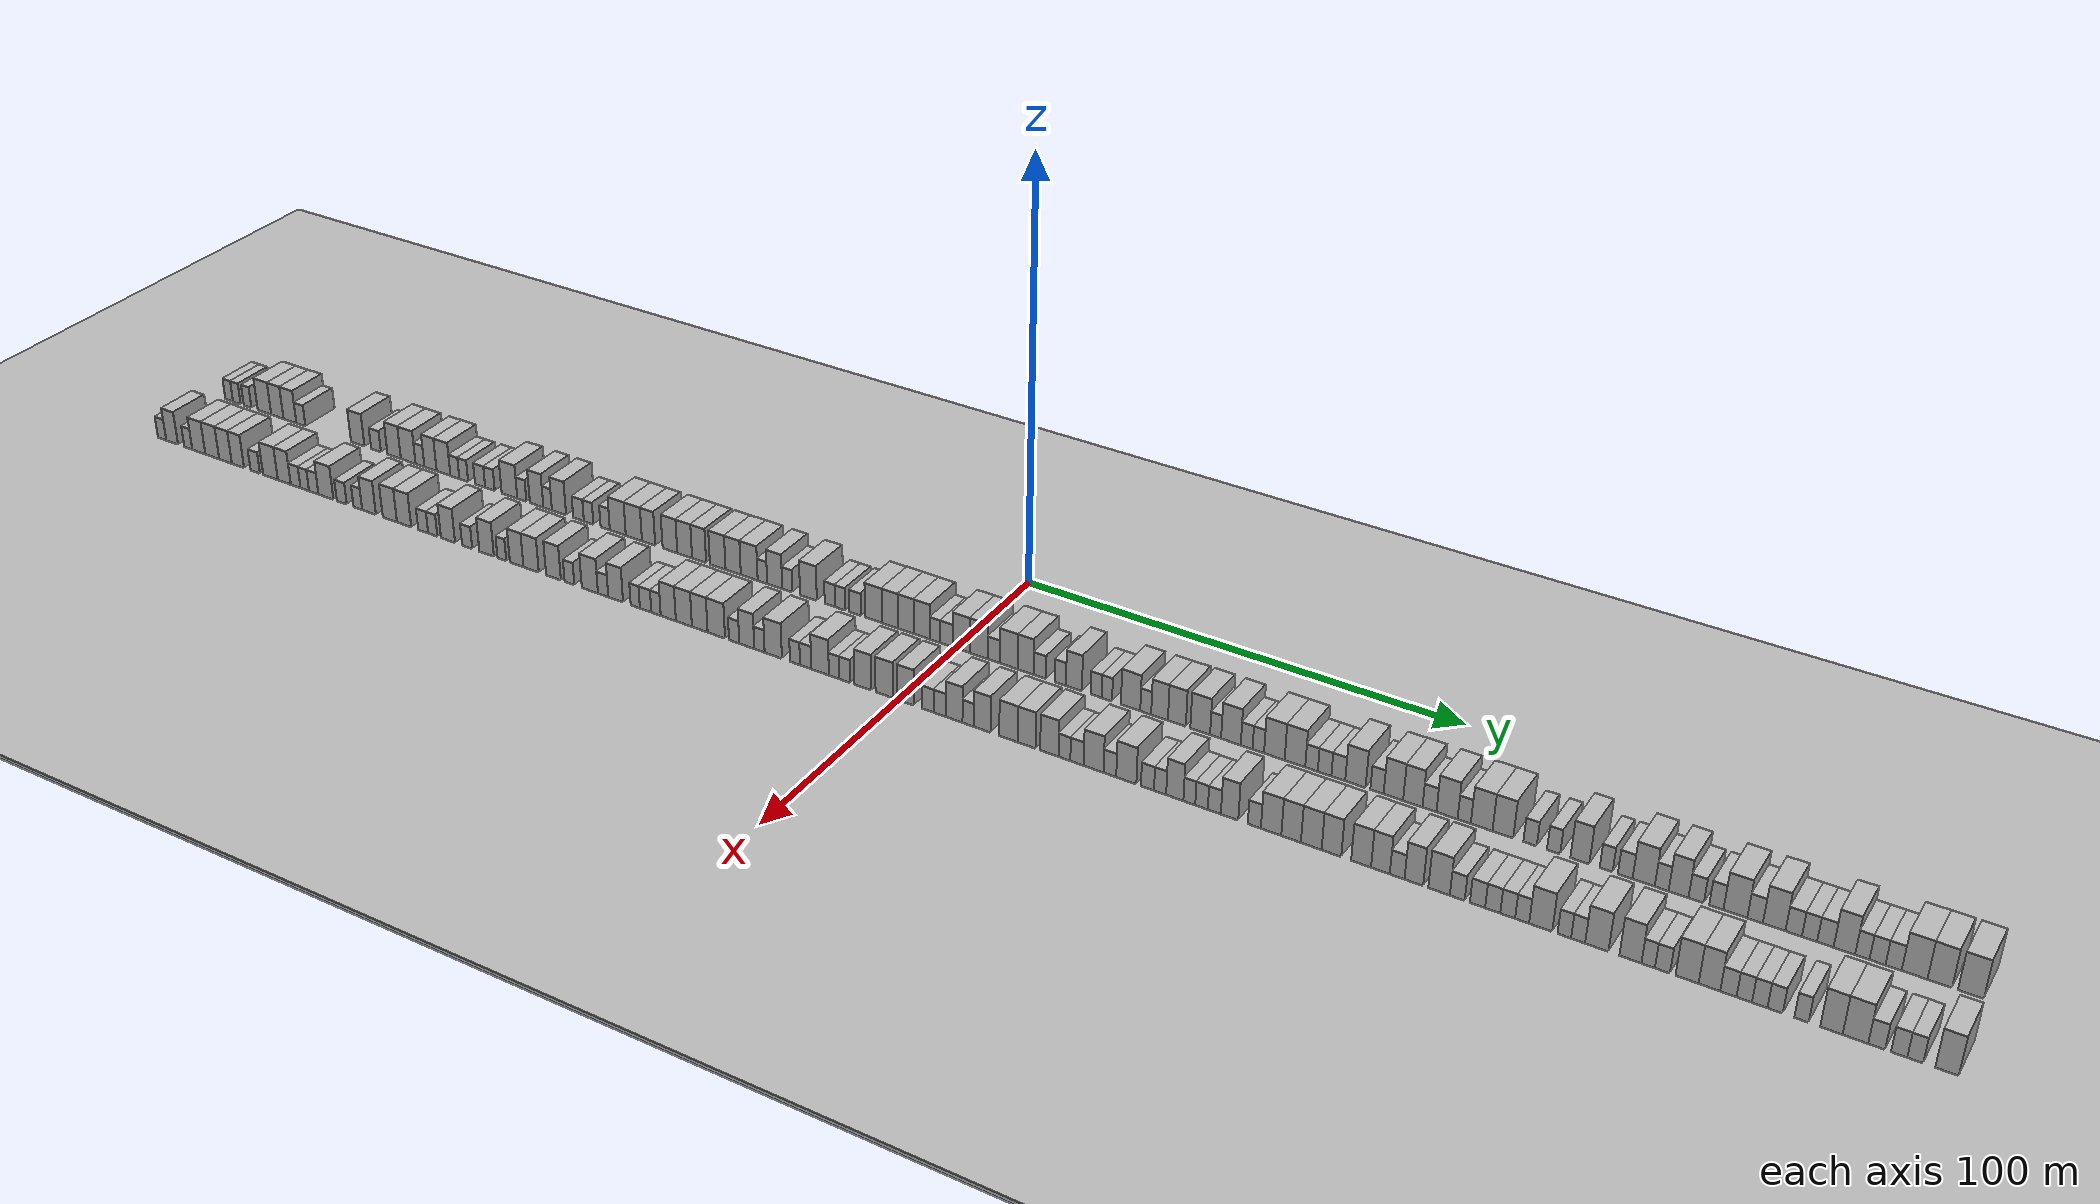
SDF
<?xml version="1.0" encoding="utf-8"?>

<sdf version="1.6">

   <world name="default">

      <gui fullscreen="0">

         <camera name="user_camera">

            <pose>-15 0 4.57585 0 0 0</pose>

            <view_controller>orbit</view_controller>

         </camera>

      </gui>

      <scene>

         <sky>

           <clouds>

             <speed>12</speed>

           </clouds>

         </sky>

         <ambient>0.4 0.4 0.4 1</ambient>

         <background>0.7 0.7 0.7 1</background>

         <shadows>1</shadows>

      </scene>

      <gravity>0 0 -9.8066</gravity>

      <magnetic_field>6e-06 2.3e-05 -4.2e-05</magnetic_field>

      <physics default="0" name="default_physics" type="ode">

         <ode>

            <solver>

               <type>quick</type>

               <iters>10</iters>

               <sor>1.0</sor>

               <use_dynamic_moi_rescaling>0</use_dynamic_moi_rescaling>

            </solver>

            <constraints>

               <cfm>0</cfm>

               <erp>0.2</erp>

               <contact_max_correcting_vel>100</contact_max_correcting_vel>

               <contact_surface_layer>0.001</contact_surface_layer>

            </constraints>

         </ode>

         <max_step_size>0.004</max_step_size>

         <real_time_factor>1</real_time_factor>

         <real_time_update_rate>250</real_time_update_rate>

      </physics>

      <light name="sun" type="directional">

         <cast_shadows>1</cast_shadows>

         <pose>0 0 10 0 0 0</pose>

         <diffuse>0.8 0.8 0.8 1</diffuse>

         <specular>0.2 0.2 0.2 1</specular>

         <attenuation>

            <range>1000</range>

            <constant>0.9</constant>

            <linear>0.01</linear>

            <quadratic>0.001</quadratic>

         </attenuation>

         <direction>-0.5 0.1 -0.9</direction>

      </light>

      <include>

         <name>ground_plane_1</name>

         <uri>model://HANNAS_ground_plane</uri>

         <pose>0 0 0  0 0 0</pose>

      </include>

      <include>

         <name>ground_plane_2</name>

         <uri>model://HANNAS_ground_plane</uri>

         <pose>100 0 0  0 0 0</pose>

      </include>

      <model name="building_1">

         <static>1</static>

         <pose frame="">25.0000 -202.7719 0 0.000000 0.000000 0.000000</pose>

         <link name="link">

            <pose frame="">0 0 3.00 0 0 0</pose>

            <collision name="collision">

               <geometry>

                  <box>

                     <size>10.0000 2.4561 6.0000</size>

                  </box>

               </geometry>

               <max_contacts>10</max_contacts>

               <surface>

                  <contact>

                     <ode/>

                  </contact>

                  <bounce/>

                  <friction>

                     <torsional>

                        <ode/>

                     </torsional>

                     <ode/>

                  </friction>

               </surface>

            </collision>

            <visual name="visual">

               <cast_shadows>0</cast_shadows>

               <geometry>

                  <box>

                     <size>10.0000 2.4561 6.0000</size>

                  </box>

               </geometry>

               <material>

                  <script>

                     <uri>model://HANNAS_wall/materials/scripts</uri>

                     <uri>model://HANNAS_wall/materials/textures</uri>

                     <name>vrc/HANNAS_wall</name>

                  </script>

               </material>

            </visual>

            <self_collide>0</self_collide>

            <enable_wind>0</enable_wind>

            <kinematic>0</kinematic>

         </link>

      </model>

      <model name="building_2">

         <static>1</static>

         <pose frame="">25.0000 -200.3070 0 0.000000 0.000000 0.000000</pose>

         <link name="link">

            <pose frame="">0 0 3.00 0 0 0</pose>

            <collision name="collision">

               <geometry>

                  <box>

                     <size>10.0000 2.4737 6.0000</size>

                  </box>

               </geometry>

               <max_contacts>10</max_contacts>

               <surface>

                  <contact>

                     <ode/>

                  </contact>

                  <bounce/>

                  <friction>

                     <torsional>

                        <ode/>

                     </torsional>

                     <ode/>

                  </friction>

               </surface>

            </collision>

            <visual name="visual">

               <cast_shadows>0</cast_shadows>

               <geometry>

                  <box>

                     <size>10.0000 2.4737 6.0000</size>

                  </box>

               </geometry>

               <material>

                  <script>

                     <uri>model://HANNAS_wall/materials/scripts</uri>

                     <uri>model://HANNAS_wall/materials/textures</uri>

                     <name>vrc/HANNAS_wall</name>

                  </script>

               </material>

            </visual>

            <self_collide>0</self_collide>

            <enable_wind>0</enable_wind>

            <kinematic>0</kinematic>

         </link>

      </model>

      <model name="building_3">

         <static>1</static>

         <pose frame="">25.0000 -196.8494 0 0.000000 0.000000 0.000000</pose>

         <link name="link">

            <pose frame="">0 0 3.00 0 0 0</pose>

            <collision name="collision">

               <geometry>

                  <box>

                     <size>10.0000 2.4415 6.0000</size>

                  </box>

               </geometry>

               <max_contacts>10</max_contacts>

               <surface>

                  <contact>

                     <ode/>

                  </contact>

                  <bounce/>

                  <friction>

                     <torsional>

                        <ode/>

                     </torsional>

                     <ode/>

                  </friction>

               </surface>

            </collision>

            <visual name="visual">

               <cast_shadows>0</cast_shadows>

               <geometry>

                  <box>

                     <size>10.0000 2.4415 6.0000</size>

                  </box>

               </geometry>

               <material>

                  <script>

                     <uri>model://HANNAS_wall/materials/scripts</uri>

                     <uri>model://HANNAS_wall/materials/textures</uri>

                     <name>vrc/HANNAS_wall</name>

                  </script>

               </material>

            </visual>

            <self_collide>0</self_collide>

            <enable_wind>0</enable_wind>

            <kinematic>0</kinematic>

         </link>

      </model>

      <model name="building_4">

         <static>1</static>

         <pose frame="">25.0000 -191.4836 0 0.000000 0.000000 0.000000</pose>

         <link name="link">

            <pose frame="">0 0 4.50 0 0 0</pose>

            <collision name="collision">

               <geometry>

                  <box>

                     <size>10.0000 4.2901 9.0000</size>

                  </box>

               </geometry>

               <max_contacts>10</max_contacts>

               <surface>

                  <contact>

                     <ode/>

                  </contact>

                  <bounce/>

                  <friction>

                     <torsional>

                        <ode/>

                     </torsional>

                     <ode/>

                  </friction>

               </surface>

            </collision>

            <visual name="visual">

               <cast_shadows>0</cast_shadows>

               <geometry>

                  <box>

                     <size>10.0000 4.2901 9.0000</size>

                  </box>

               </geometry>

               <material>

                  <script>

                     <uri>model://HANNAS_wall/materials/scripts</uri>

                     <uri>model://HANNAS_wall/materials/textures</uri>

                     <name>vrc/HANNAS_wall</name>

                  </script>

               </material>

            </visual>

            <self_collide>0</self_collide>

            <enable_wind>0</enable_wind>

            <kinematic>0</kinematic>

         </link>

      </model>

      <model name="building_5">

         <static>1</static>

         <pose frame="">25.0000 -187.3843 0 0.000000 0.000000 0.000000</pose>

         <link name="link">

            <pose frame="">0 0 4.50 0 0 0</pose>

            <collision name="collision">

               <geometry>

                  <box>

                     <size>10.0000 3.9084 9.0000</size>

                  </box>

               </geometry>

               <max_contacts>10</max_contacts>

               <surface>

                  <contact>

                     <ode/>

                  </contact>

                  <bounce/>

                  <friction>

                     <torsional>

                        <ode/>

                     </torsional>

                     <ode/>

                  </friction>

               </surface>

            </collision>

            <visual name="visual">

               <cast_shadows>0</cast_shadows>

               <geometry>

                  <box>

                     <size>10.0000 3.9084 9.0000</size>

                  </box>

               </geometry>

               <material>

                  <script>

                     <uri>model://HANNAS_wall/materials/scripts</uri>

                     <uri>model://HANNAS_wall/materials/textures</uri>

                     <name>vrc/HANNAS_wall</name>

                  </script>

               </material>

            </visual>

            <self_collide>0</self_collide>

            <enable_wind>0</enable_wind>

            <kinematic>0</kinematic>

         </link>

      </model>

      <model name="building_6">

         <static>1</static>

         <pose frame="">25.0000 -183.4129 0 0.000000 0.000000 0.000000</pose>

         <link name="link">

            <pose frame="">0 0 4.50 0 0 0</pose>

            <collision name="collision">

               <geometry>

                  <box>

                     <size>10.0000 4.0344 9.0000</size>

                  </box>

               </geometry>

               <max_contacts>10</max_contacts>

               <surface>

                  <contact>

                     <ode/>

                  </contact>

                  <bounce/>

                  <friction>

                     <torsional>

                        <ode/>

                     </torsional>

                     <ode/>

                  </friction>

               </surface>

            </collision>

            <visual name="visual">

               <cast_shadows>0</cast_shadows>

               <geometry>

                  <box>

                     <size>10.0000 4.0344 9.0000</size>

                  </box>

               </geometry>

               <material>

                  <script>

                     <uri>model://HANNAS_wall/materials/scripts</uri>

                     <uri>model://HANNAS_wall/materials/textures</uri>

                     <name>vrc/HANNAS_wall</name>

                  </script>

               </material>

            </visual>

            <self_collide>0</self_collide>

            <enable_wind>0</enable_wind>

            <kinematic>0</kinematic>

         </link>

      </model>

      <model name="building_7">

         <static>1</static>

         <pose frame="">25.0000 -179.9750 0 0.000000 0.000000 0.000000</pose>

         <link name="link">

            <pose frame="">0 0 3.00 0 0 0</pose>

            <collision name="collision">

               <geometry>

                  <box>

                     <size>10.0000 2.8414 6.0000</size>

                  </box>

               </geometry>

               <max_contacts>10</max_contacts>

               <surface>

                  <contact>

                     <ode/>

                  </contact>

                  <bounce/>

                  <friction>

                     <torsional>

                        <ode/>

                     </torsional>

                     <ode/>

                  </friction>

               </surface>

            </collision>

            <visual name="visual">

               <cast_shadows>0</cast_shadows>

               <geometry>

                  <box>

                     <size>10.0000 2.8414 6.0000</size>

                  </box>

               </geometry>

               <material>

                  <script>

                     <uri>model://HANNAS_wall/materials/scripts</uri>

                     <uri>model://HANNAS_wall/materials/textures</uri>

                     <name>vrc/HANNAS_wall</name>

                  </script>

               </material>

            </visual>

            <self_collide>0</self_collide>

            <enable_wind>0</enable_wind>

            <kinematic>0</kinematic>

         </link>

      </model>

      <model name="building_8">

         <static>1</static>

         <pose frame="">25.0000 -162.3760 0 0.000000 0.000000 0.000000</pose>

         <link name="link">

            <pose frame="">0 0 4.50 0 0 0</pose>

            <collision name="collision">

               <geometry>

                  <box>

                     <size>10.0000 4.1189 9.0000</size>

                  </box>

               </geometry>

               <max_contacts>10</max_contacts>

               <surface>

                  <contact>

                     <ode/>

                  </contact>

                  <bounce/>

                  <friction>

                     <torsional>

                        <ode/>

                     </torsional>

                     <ode/>

                  </friction>

               </surface>

            </collision>

            <visual name="visual">

               <cast_shadows>0</cast_shadows>

               <geometry>

                  <box>

                     <size>10.0000 4.1189 9.0000</size>

                  </box>

               </geometry>

               <material>

                  <script>

                     <uri>model://HANNAS_wall/materials/scripts</uri>

                     <uri>model://HANNAS_wall/materials/textures</uri>

                     <name>vrc/HANNAS_wall</name>

                  </script>

               </material>

            </visual>

            <self_collide>0</self_collide>

            <enable_wind>0</enable_wind>

            <kinematic>0</kinematic>

         </link>

      </model>

      <model name="building_9">

         <static>1</static>

         <pose frame="">25.0000 -156.8361 0 0.000000 0.000000 0.000000</pose>

         <link name="link">

            <pose frame="">0 0 3.00 0 0 0</pose>

            <collision name="collision">

               <geometry>

                  <box>

                     <size>10.0000 2.9607 6.0000</size>

                  </box>

               </geometry>

               <max_contacts>10</max_contacts>

               <surface>

                  <contact>

                     <ode/>

                  </contact>

                  <bounce/>

                  <friction>

                     <torsional>

                        <ode/>

                     </torsional>

                     <ode/>

                  </friction>

               </surface>

            </collision>

            <visual name="visual">

               <cast_shadows>0</cast_shadows>

               <geometry>

                  <box>

                     <size>10.0000 2.9607 6.0000</size>

                  </box>

               </geometry>

               <material>

                  <script>

                     <uri>model://HANNAS_wall/materials/scripts</uri>

                     <uri>model://HANNAS_wall/materials/textures</uri>

                     <name>vrc/HANNAS_wall</name>

                  </script>

               </material>

            </visual>

            <self_collide>0</self_collide>

            <enable_wind>0</enable_wind>

            <kinematic>0</kinematic>

         </link>

      </model>

      <model name="building_10">

         <static>1</static>

         <pose frame="">25.0000 -151.3435 0 0.000000 0.000000 0.000000</pose>

         <link name="link">

            <pose frame="">0 0 4.50 0 0 0</pose>

            <collision name="collision">

               <geometry>

                  <box>

                     <size>10.0000 4.0245 9.0000</size>

                  </box>

               </geometry>

               <max_contacts>10</max_contacts>

               <surface>

                  <contact>

                     <ode/>

                  </contact>

                  <bounce/>

                  <friction>

                     <torsional>

                        <ode/>

                     </torsional>

                     <ode/>

                  </friction>

               </surface>

            </collision>

            <visual name="visual">

               <cast_shadows>0</cast_shadows>

               <geometry>

                  <box>

                     <size>10.0000 4.0245 9.0000</size>

                  </box>

               </geometry>

               <material>

                  <script>

                     <uri>model://HANNAS_wall/materials/scripts</uri>

                     <uri>model://HANNAS_wall/materials/textures</uri>

                     <name>vrc/HANNAS_wall</name>

                  </script>

               </material>

            </visual>

            <self_collide>0</self_collide>

            <enable_wind>0</enable_wind>

            <kinematic>0</kinematic>

         </link>

      </model>

      <model name="building_11">

         <static>1</static>

         <pose frame="">25.0000 -147.1299 0 0.000000 0.000000 0.000000</pose>

         <link name="link">

            <pose frame="">0 0 4.50 0 0 0</pose>

            <collision name="collision">

               <geometry>

                  <box>

                     <size>10.0000 4.4029 9.0000</size>

                  </box>

               </geometry>

               <max_contacts>10</max_contacts>

               <surface>

                  <contact>

                     <ode/>

                  </contact>

                  <bounce/>

                  <friction>

                     <torsional>

                        <ode/>

                     </torsional>

                     <ode/>

                  </friction>

               </surface>

            </collision>

            <visual name="visual">

               <cast_shadows>0</cast_shadows>

               <geometry>

                  <box>

                     <size>10.0000 4.4029 9.0000</size>

                  </box>

               </geometry>

               <material>

                  <script>

                     <uri>model://HANNAS_wall/materials/scripts</uri>

                     <uri>model://HANNAS_wall/materials/textures</uri>

                     <name>vrc/HANNAS_wall</name>

                  </script>

               </material>

            </visual>

            <self_collide>0</self_collide>

            <enable_wind>0</enable_wind>

            <kinematic>0</kinematic>

         </link>

      </model>

      <model name="building_12">

         <static>1</static>

         <pose frame="">25.0000 -143.6079 0 0.000000 0.000000 0.000000</pose>

         <link name="link">

            <pose frame="">0 0 3.00 0 0 0</pose>

            <collision name="collision">

               <geometry>

                  <box>

                     <size>10.0000 2.6410 6.0000</size>

                  </box>

               </geometry>

               <max_contacts>10</max_contacts>

               <surface>

                  <contact>

                     <ode/>

                  </contact>

                  <bounce/>

                  <friction>

                     <torsional>

                        <ode/>

                     </torsional>

                     <ode/>

                  </friction>

               </surface>

            </collision>

            <visual name="visual">

               <cast_shadows>0</cast_shadows>

               <geometry>

                  <box>

                     <size>10.0000 2.6410 6.0000</size>

                  </box>

               </geometry>

               <material>

                  <script>

                     <uri>model://HANNAS_wall/materials/scripts</uri>

                     <uri>model://HANNAS_wall/materials/textures</uri>

                     <name>vrc/HANNAS_wall</name>

                  </script>

               </material>

            </visual>

            <self_collide>0</self_collide>

            <enable_wind>0</enable_wind>

            <kinematic>0</kinematic>

         </link>

      </model>

      <model name="building_13">

         <static>1</static>

         <pose frame="">25.0000 -140.4758 0 0.000000 0.000000 0.000000</pose>

         <link name="link">

            <pose frame="">0 0 4.50 0 0 0</pose>

            <collision name="collision">

               <geometry>

                  <box>

                     <size>10.0000 3.6233 9.0000</size>

                  </box>

               </geometry>

               <max_contacts>10</max_contacts>

               <surface>

                  <contact>

                     <ode/>

                  </contact>

                  <bounce/>

                  <friction>

                     <torsional>

                        <ode/>

                     </torsional>

                     <ode/>

                  </friction>

               </surface>

            </collision>

            <visual name="visual">

               <cast_shadows>0</cast_shadows>

               <geometry>

                  <box>

                     <size>10.0000 3.6233 9.0000</size>

                  </box>

               </geometry>

               <material>

                  <script>

                     <uri>model://HANNAS_wall/materials/scripts</uri>

                     <uri>model://HANNAS_wall/materials/textures</uri>

                     <name>vrc/HANNAS_wall</name>

                  </script>

               </material>

            </visual>

            <self_collide>0</self_collide>

            <enable_wind>0</enable_wind>

            <kinematic>0</kinematic>

         </link>

      </model>

      <model name="building_14">

         <static>1</static>

         <pose frame="">25.0000 -136.6312 0 0.000000 0.000000 0.000000</pose>

         <link name="link">

            <pose frame="">0 0 4.50 0 0 0</pose>

            <collision name="collision">

               <geometry>

                  <box>

                     <size>10.0000 4.0660 9.0000</size>

                  </box>

               </geometry>

               <max_contacts>10</max_contacts>

               <surface>

                  <contact>

                     <ode/>

                  </contact>

                  <bounce/>

                  <friction>

                     <torsional>

                        <ode/>

                     </torsional>

                     <ode/>

                  </friction>

               </surface>

            </collision>

            <visual name="visual">

               <cast_shadows>0</cast_shadows>

               <geometry>

                  <box>

                     <size>10.0000 4.0660 9.0000</size>

                  </box>

               </geometry>

               <material>

                  <script>

                     <uri>model://HANNAS_wall/materials/scripts</uri>

                     <uri>model://HANNAS_wall/materials/textures</uri>

                     <name>vrc/HANNAS_wall</name>

                  </script>

               </material>

            </visual>

            <self_collide>0</self_collide>

            <enable_wind>0</enable_wind>

            <kinematic>0</kinematic>

         </link>

      </model>

      <model name="building_15">

         <static>1</static>

         <pose frame="">25.0000 -133.2866 0 0.000000 0.000000 0.000000</pose>

         <link name="link">

            <pose frame="">0 0 3.00 0 0 0</pose>

            <collision name="collision">

               <geometry>

                  <box>

                     <size>10.0000 2.6232 6.0000</size>

                  </box>

               </geometry>

               <max_contacts>10</max_contacts>

               <surface>

                  <contact>

                     <ode/>

                  </contact>

                  <bounce/>

                  <friction>

                     <torsional>

                        <ode/>

                     </torsional>

                     <ode/>

                  </friction>

               </surface>

            </collision>

            <visual name="visual">

               <cast_shadows>0</cast_shadows>

               <geometry>

                  <box>

                     <size>10.0000 2.6232 6.0000</size>

                  </box>

               </geometry>

               <material>

                  <script>

                     <uri>model://HANNAS_wall/materials/scripts</uri>

                     <uri>model://HANNAS_wall/materials/textures</uri>

                     <name>vrc/HANNAS_wall</name>

                  </script>

               </material>

            </visual>

            <self_collide>0</self_collide>

            <enable_wind>0</enable_wind>

            <kinematic>0</kinematic>

         </link>

      </model>

      <model name="building_16">

         <static>1</static>

         <pose frame="">25.0000 -130.6864 0 0.000000 0.000000 0.000000</pose>

         <link name="link">

            <pose frame="">0 0 3.00 0 0 0</pose>

            <collision name="collision">

               <geometry>

                  <box>

                     <size>10.0000 2.5771 6.0000</size>

                  </box>

               </geometry>

               <max_contacts>10</max_contacts>

               <surface>

                  <contact>

                     <ode/>

                  </contact>

                  <bounce/>

                  <friction>

                     <torsional>

                        <ode/>

                     </torsional>

                     <ode/>

                  </friction>

               </surface>

            </collision>

            <visual name="visual">

               <cast_shadows>0</cast_shadows>

               <geometry>

                  <box>

                     <size>10.0000 2.5771 6.0000</size>

                  </box>

               </geometry>

               <material>

                  <script>

                     <uri>model://HANNAS_wall/materials/scripts</uri>

                     <uri>model://HANNAS_wall/materials/textures</uri>

                     <name>vrc/HANNAS_wall</name>

                  </script>

               </material>

            </visual>

            <self_collide>0</self_collide>

            <enable_wind>0</enable_wind>

            <kinematic>0</kinematic>

         </link>

      </model>

      <model name="building_17">

         <static>1</static>

         <pose frame="">25.0000 -125.9183 0 0.000000 0.000000 0.000000</pose>

         <link name="link">

            <pose frame="">0 0 3.00 0 0 0</pose>

            <collision name="collision">

               <geometry>

                  <box>

                     <size>10.0000 2.9592 6.0000</size>

                  </box>

               </geometry>

               <max_contacts>10</max_contacts>

               <surface>

                  <contact>

                     <ode/>

                  </contact>

                  <bounce/>

                  <friction>

                     <torsional>

                        <ode/>

                     </torsional>

                     <ode/>

                  </friction>

               </surface>

            </collision>

            <visual name="visual">

               <cast_shadows>0</cast_shadows>

               <geometry>

                  <box>

                     <size>10.0000 2.9592 6.0000</size>

                  </box>

               </geometry>

               <material>

                  <script>

                     <uri>model://HANNAS_wall/materials/scripts</uri>

                     <uri>model://HANNAS_wall/materials/textures</uri>

                     <name>vrc/HANNAS_wall</name>

                  </script>

               </material>

            </visual>

            <self_collide>0</self_collide>

            <enable_wind>0</enable_wind>

            <kinematic>0</kinematic>

         </link>

      </model>

      <model name="building_18">

         <static>1</static>

         <pose frame="">25.0000 -123.0581 0 0.000000 0.000000 0.000000</pose>

         <link name="link">

            <pose frame="">0 0 3.00 0 0 0</pose>

            <collision name="collision">

               <geometry>

                  <box>

                     <size>10.0000 2.7611 6.0000</size>

                  </box>

               </geometry>

               <max_contacts>10</max_contacts>

               <surface>

                  <contact>

                     <ode/>

                  </contact>

                  <bounce/>

                  <friction>

                     <torsional>

                        <ode/>

                     </torsional>

                     <ode/>

                  </friction>

               </surface>

            </collision>

            <visual name="visual">

               <cast_shadows>0</cast_shadows>

               <geometry>

                  <box>

                     <size>10.0000 2.7611 6.0000</size>

                  </box>

               </geometry>

               <material>

                  <script>

                     <uri>model://HANNAS_wall/materials/scripts</uri>

                     <uri>model://HANNAS_wall/materials/textures</uri>

                     <name>vrc/HANNAS_wall</name>

                  </script>

               </material>

            </visual>

            <self_collide>0</self_collide>

            <enable_wind>0</enable_wind>

            <kinematic>0</kinematic>

         </link>

      </model>

      <model name="building_19">

         <static>1</static>

         <pose frame="">25.0000 -117.4313 0 0.000000 0.000000 0.000000</pose>

         <link name="link">

            <pose frame="">0 0 4.50 0 0 0</pose>

            <collision name="collision">

               <geometry>

                  <box>

                     <size>10.0000 4.4925 9.0000</size>

                  </box>

               </geometry>

               <max_contacts>10</max_contacts>

               <surface>

                  <contact>

                     <ode/>

                  </contact>

                  <bounce/>

                  <friction>

                     <torsional>

                        <ode/>

                     </torsional>

                     <ode/>

                  </friction>

               </surface>

            </collision>

            <visual name="visual">

               <cast_shadows>0</cast_shadows>

               <geometry>

                  <box>

                     <size>10.0000 4.4925 9.0000</size>

                  </box>

               </geometry>

               <material>

                  <script>

                     <uri>model://HANNAS_wall/materials/scripts</uri>

                     <uri>model://HANNAS_wall/materials/textures</uri>

                     <name>vrc/HANNAS_wall</name>

                  </script>

               </material>

            </visual>

            <self_collide>0</self_collide>

            <enable_wind>0</enable_wind>

            <kinematic>0</kinematic>

         </link>

      </model>

      <model name="building_20">

         <static>1</static>

         <pose frame="">25.0000 -113.8875 0 0.000000 0.000000 0.000000</pose>

         <link name="link">

            <pose frame="">0 0 3.00 0 0 0</pose>

            <collision name="collision">

               <geometry>

                  <box>

                     <size>10.0000 2.5951 6.0000</size>

                  </box>

               </geometry>

               <max_contacts>10</max_contacts>

               <surface>

                  <contact>

                     <ode/>

                  </contact>

                  <bounce/>

                  <friction>

                     <torsional>

                        <ode/>

                     </torsional>

                     <ode/>

                  </friction>

               </surface>

            </collision>

            <visual name="visual">

               <cast_shadows>0</cast_shadows>

               <geometry>

                  <box>

                     <size>10.0000 2.5951 6.0000</size>

                  </box>

               </geometry>

               <material>

                  <script>

                     <uri>model://HANNAS_wall/materials/scripts</uri>

                     <uri>model://HANNAS_wall/materials/textures</uri>

                     <name>vrc/HANNAS_wall</name>

                  </script>

               </material>

            </visual>

            <self_collide>0</self_collide>

            <enable_wind>0</enable_wind>

            <kinematic>0</kinematic>

         </link>

      </model>

      <model name="building_21">

         <static>1</static>

         <pose frame="">25.0000 -109.6784 0 0.000000 0.000000 0.000000</pose>

         <link name="link">

            <pose frame="">0 0 4.50 0 0 0</pose>

            <collision name="collision">

               <geometry>

                  <box>

                     <size>10.0000 3.8230 9.0000</size>

                  </box>

               </geometry>

               <max_contacts>10</max_contacts>

               <surface>

                  <contact>

                     <ode/>

                  </contact>

                  <bounce/>

                  <friction>

                     <torsional>

                        <ode/>

                     </torsional>

                     <ode/>

                  </friction>

               </surface>

            </collision>

            <visual name="visual">

               <cast_shadows>0</cast_shadows>

               <geometry>

                  <box>

                     <size>10.0000 3.8230 9.0000</size>

                  </box>

               </geometry>

               <material>

                  <script>

                     <uri>model://HANNAS_wall/materials/scripts</uri>

                     <uri>model://HANNAS_wall/materials/textures</uri>

                     <name>vrc/HANNAS_wall</name>

                  </script>

               </material>

            </visual>

            <self_collide>0</self_collide>

            <enable_wind>0</enable_wind>

            <kinematic>0</kinematic>

         </link>

      </model>

      <model name="building_22">

         <static>1</static>

         <pose frame="">25.0000 -106.5655 0 0.000000 0.000000 0.000000</pose>

         <link name="link">

            <pose frame="">0 0 3.00 0 0 0</pose>

            <collision name="collision">

               <geometry>

                  <box>

                     <size>10.0000 2.4029 6.0000</size>

                  </box>

               </geometry>

               <max_contacts>10</max_contacts>

               <surface>

                  <contact>

                     <ode/>

                  </contact>

                  <bounce/>

                  <friction>

                     <torsional>

                        <ode/>

                     </torsional>

                     <ode/>

                  </friction>

               </surface>

            </collision>

            <visual name="visual">

               <cast_shadows>0</cast_shadows>

               <geometry>

                  <box>

                     <size>10.0000 2.4029 6.0000</size>

                  </box>

               </geometry>

               <material>

                  <script>

                     <uri>model://HANNAS_wall/materials/scripts</uri>

                     <uri>model://HANNAS_wall/materials/textures</uri>

                     <name>vrc/HANNAS_wall</name>

                  </script>

               </material>

            </visual>

            <self_collide>0</self_collide>

            <enable_wind>0</enable_wind>

            <kinematic>0</kinematic>

         </link>

      </model>

      <model name="building_23">

         <static>1</static>

         <pose frame="">25.0000 -103.3707 0 0.000000 0.000000 0.000000</pose>

         <link name="link">

            <pose frame="">0 0 4.50 0 0 0</pose>

            <collision name="collision">

               <geometry>

                  <box>

                     <size>10.0000 3.9866 9.0000</size>

                  </box>

               </geometry>

               <max_contacts>10</max_contacts>

               <surface>

                  <contact>

                     <ode/>

                  </contact>

                  <bounce/>

                  <friction>

                     <torsional>

                        <ode/>

                     </torsional>

                     <ode/>

                  </friction>

               </surface>

            </collision>

            <visual name="visual">

               <cast_shadows>0</cast_shadows>

               <geometry>

                  <box>

                     <size>10.0000 3.9866 9.0000</size>

                  </box>

               </geometry>

               <material>

                  <script>

                     <uri>model://HANNAS_wall/materials/scripts</uri>

                     <uri>model://HANNAS_wall/materials/textures</uri>

                     <name>vrc/HANNAS_wall</name>

                  </script>

               </material>

            </visual>

            <self_collide>0</self_collide>

            <enable_wind>0</enable_wind>

            <kinematic>0</kinematic>

         </link>

      </model>

      <model name="building_24">

         <static>1</static>

         <pose frame="">25.0000 -97.8894 0 0.000000 0.000000 0.000000</pose>

         <link name="link">

            <pose frame="">0 0 3.00 0 0 0</pose>

            <collision name="collision">

               <geometry>

                  <box>

                     <size>10.0000 2.9759 6.0000</size>

                  </box>

               </geometry>

               <max_contacts>10</max_contacts>

               <surface>

                  <contact>

                     <ode/>

                  </contact>

                  <bounce/>

                  <friction>

                     <torsional>

                        <ode/>

                     </torsional>

                     <ode/>

                  </friction>

               </surface>

            </collision>

            <visual name="visual">

               <cast_shadows>0</cast_shadows>

               <geometry>

                  <box>

                     <size>10.0000 2.9759 6.0000</size>

                  </box>

               </geometry>

               <material>

                  <script>

                     <uri>model://HANNAS_wall/materials/scripts</uri>

                     <uri>model://HANNAS_wall/materials/textures</uri>

                     <name>vrc/HANNAS_wall</name>

                  </script>

               </material>

            </visual>

            <self_collide>0</self_collide>

            <enable_wind>0</enable_wind>

            <kinematic>0</kinematic>

         </link>

      </model>

      <model name="building_25">

         <static>1</static>

         <pose frame="">25.0000 -95.0828 0 0.000000 0.000000 0.000000</pose>

         <link name="link">

            <pose frame="">0 0 3.00 0 0 0</pose>

            <collision name="collision">

               <geometry>

                  <box>

                     <size>10.0000 2.6372 6.0000</size>

                  </box>

               </geometry>

               <max_contacts>10</max_contacts>

               <surface>

                  <contact>

                     <ode/>

                  </contact>

                  <bounce/>

                  <friction>

                     <torsional>

                        <ode/>

                     </torsional>

                     <ode/>

                  </friction>

               </surface>

            </collision>

            <visual name="visual">

               <cast_shadows>0</cast_shadows>

               <geometry>

                  <box>

                     <size>10.0000 2.6372 6.0000</size>

                  </box>

               </geometry>

               <material>

                  <script>

                     <uri>model://HANNAS_wall/materials/scripts</uri>

                     <uri>model://HANNAS_wall/materials/textures</uri>

                     <name>vrc/HANNAS_wall</name>

                  </script>

               </material>

            </visual>

            <self_collide>0</self_collide>

            <enable_wind>0</enable_wind>

            <kinematic>0</kinematic>

         </link>

      </model>

      <model name="building_26">

         <static>1</static>

         <pose frame="">25.0000 -90.4833 0 0.000000 0.000000 0.000000</pose>

         <link name="link">

            <pose frame="">0 0 3.00 0 0 0</pose>

            <collision name="collision">

               <geometry>

                  <box>

                     <size>10.0000 2.5618 6.0000</size>

                  </box>

               </geometry>

               <max_contacts>10</max_contacts>

               <surface>

                  <contact>

                     <ode/>

                  </contact>

                  <bounce/>

                  <friction>

                     <torsional>

                        <ode/>

                     </torsional>

                     <ode/>

                  </friction>

               </surface>

            </collision>

            <visual name="visual">

               <cast_shadows>0</cast_shadows>

               <geometry>

                  <box>

                     <size>10.0000 2.5618 6.0000</size>

                  </box>

               </geometry>

               <material>

                  <script>

                     <uri>model://HANNAS_wall/materials/scripts</uri>

                     <uri>model://HANNAS_wall/materials/textures</uri>

                     <name>vrc/HANNAS_wall</name>

                  </script>

               </material>

            </visual>

            <self_collide>0</self_collide>

            <enable_wind>0</enable_wind>

            <kinematic>0</kinematic>

         </link>

      </model>

      <model name="building_27">

         <static>1</static>

         <pose frame="">25.0000 -87.0142 0 0.000000 0.000000 0.000000</pose>

         <link name="link">

            <pose frame="">0 0 4.50 0 0 0</pose>

            <collision name="collision">

               <geometry>

                  <box>

                     <size>10.0000 4.3764 9.0000</size>

                  </box>

               </geometry>

               <max_contacts>10</max_contacts>

               <surface>

                  <contact>

                     <ode/>

                  </contact>

                  <bounce/>

                  <friction>

                     <torsional>

                        <ode/>

                     </torsional>

                     <ode/>

                  </friction>

               </surface>

            </collision>

            <visual name="visual">

               <cast_shadows>0</cast_shadows>

               <geometry>

                  <box>

                     <size>10.0000 4.3764 9.0000</size>

                  </box>

               </geometry>

               <material>

                  <script>

                     <uri>model://HANNAS_wall/materials/scripts</uri>

                     <uri>model://HANNAS_wall/materials/textures</uri>

                     <name>vrc/HANNAS_wall</name>

                  </script>

               </material>

            </visual>

            <self_collide>0</self_collide>

            <enable_wind>0</enable_wind>

            <kinematic>0</kinematic>

         </link>

      </model>

      <model name="building_28">

         <static>1</static>

         <pose frame="">25.0000 -82.6130 0 0.000000 0.000000 0.000000</pose>

         <link name="link">

            <pose frame="">0 0 4.50 0 0 0</pose>

            <collision name="collision">

               <geometry>

                  <box>

                     <size>10.0000 4.4262 9.0000</size>

                  </box>

               </geometry>

               <max_contacts>10</max_contacts>

               <surface>

                  <contact>

                     <ode/>

                  </contact>

                  <bounce/>

                  <friction>

                     <torsional>

                        <ode/>

                     </torsional>

                     <ode/>

                  </friction>

               </surface>

            </collision>

            <visual name="visual">

               <cast_shadows>0</cast_shadows>

               <geometry>

                  <box>

                     <size>10.0000 4.4262 9.0000</size>

                  </box>

               </geometry>

               <material>

                  <script>

                     <uri>model://HANNAS_wall/materials/scripts</uri>

                     <uri>model://HANNAS_wall/materials/textures</uri>

                     <name>vrc/HANNAS_wall</name>

                  </script>

               </material>

            </visual>

            <self_collide>0</self_collide>

            <enable_wind>0</enable_wind>

            <kinematic>0</kinematic>

         </link>

      </model>

      <model name="building_29">

         <static>1</static>

         <pose frame="">25.0000 -78.5988 0 0.000000 0.000000 0.000000</pose>

         <link name="link">

            <pose frame="">0 0 4.50 0 0 0</pose>

            <collision name="collision">

               <geometry>

                  <box>

                     <size>10.0000 3.6021 9.0000</size>

                  </box>

               </geometry>

               <max_contacts>10</max_contacts>

               <surface>

                  <contact>

                     <ode/>

                  </contact>

                  <bounce/>

                  <friction>

                     <torsional>

                        <ode/>

                     </torsional>

                     <ode/>

                  </friction>

               </surface>

            </collision>

            <visual name="visual">

               <cast_shadows>0</cast_shadows>

               <geometry>

                  <box>

                     <size>10.0000 3.6021 9.0000</size>

                  </box>

               </geometry>

               <material>

                  <script>

                     <uri>model://HANNAS_wall/materials/scripts</uri>

                     <uri>model://HANNAS_wall/materials/textures</uri>

                     <name>vrc/HANNAS_wall</name>

                  </script>

               </material>

            </visual>

            <self_collide>0</self_collide>

            <enable_wind>0</enable_wind>

            <kinematic>0</kinematic>

         </link>

      </model>

      <model name="building_30">

         <static>1</static>

         <pose frame="">25.0000 -72.8228 0 0.000000 0.000000 0.000000</pose>

         <link name="link">

            <pose frame="">0 0 4.50 0 0 0</pose>

            <collision name="collision">

               <geometry>

                  <box>

                     <size>10.0000 3.9499 9.0000</size>

                  </box>

               </geometry>

               <max_contacts>10</max_contacts>

               <surface>

                  <contact>

                     <ode/>

                  </contact>

                  <bounce/>

                  <friction>

                     <torsional>

                        <ode/>

                     </torsional>

                     <ode/>

                  </friction>

               </surface>

            </collision>

            <visual name="visual">

               <cast_shadows>0</cast_shadows>

               <geometry>

                  <box>

                     <size>10.0000 3.9499 9.0000</size>

                  </box>

               </geometry>

               <material>

                  <script>

                     <uri>model://HANNAS_wall/materials/scripts</uri>

                     <uri>model://HANNAS_wall/materials/textures</uri>

                     <name>vrc/HANNAS_wall</name>

                  </script>

               </material>

            </visual>

            <self_collide>0</self_collide>

            <enable_wind>0</enable_wind>

            <kinematic>0</kinematic>

         </link>

      </model>

      <model name="building_31">

         <static>1</static>

         <pose frame="">25.0000 -68.8749 0 0.000000 0.000000 0.000000</pose>

         <link name="link">

            <pose frame="">0 0 4.50 0 0 0</pose>

            <collision name="collision">

               <geometry>

                  <box>

                     <size>10.0000 3.9461 9.0000</size>

                  </box>

               </geometry>

               <max_contacts>10</max_contacts>

               <surface>

                  <contact>

                     <ode/>

                  </contact>

                  <bounce/>

                  <friction>

                     <torsional>

                        <ode/>

                     </torsional>

                     <ode/>

                  </friction>

               </surface>

            </collision>

            <visual name="visual">

               <cast_shadows>0</cast_shadows>

               <geometry>

                  <box>

                     <size>10.0000 3.9461 9.0000</size>

                  </box>

               </geometry>

               <material>

                  <script>

                     <uri>model://HANNAS_wall/materials/scripts</uri>

                     <uri>model://HANNAS_wall/materials/textures</uri>

                     <name>vrc/HANNAS_wall</name>

                  </script>

               </material>

            </visual>

            <self_collide>0</self_collide>

            <enable_wind>0</enable_wind>

            <kinematic>0</kinematic>

         </link>

      </model>

      <model name="building_32">

         <static>1</static>

         <pose frame="">25.0000 -65.0329 0 0.000000 0.000000 0.000000</pose>

         <link name="link">

            <pose frame="">0 0 4.50 0 0 0</pose>

            <collision name="collision">

               <geometry>

                  <box>

                     <size>10.0000 3.7378 9.0000</size>

                  </box>

               </geometry>

               <max_contacts>10</max_contacts>

               <surface>

                  <contact>

                     <ode/>

                  </contact>

                  <bounce/>

                  <friction>

                     <torsional>

                        <ode/>

                     </torsional>

                     <ode/>

                  </friction>

               </surface>

            </collision>

            <visual name="visual">

               <cast_shadows>0</cast_shadows>

               <geometry>

                  <box>

                     <size>10.0000 3.7378 9.0000</size>

                  </box>

               </geometry>

               <material>

                  <script>

                     <uri>model://HANNAS_wall/materials/scripts</uri>

                     <uri>model://HANNAS_wall/materials/textures</uri>

                     <name>vrc/HANNAS_wall</name>

                  </script>

               </material>

            </visual>

            <self_collide>0</self_collide>

            <enable_wind>0</enable_wind>

            <kinematic>0</kinematic>

         </link>

      </model>

      <model name="building_33">

         <static>1</static>

         <pose frame="">25.0000 -60.0952 0 0.000000 0.000000 0.000000</pose>

         <link name="link">

            <pose frame="">0 0 4.50 0 0 0</pose>

            <collision name="collision">

               <geometry>

                  <box>

                     <size>10.0000 4.1376 9.0000</size>

                  </box>

               </geometry>

               <max_contacts>10</max_contacts>

               <surface>

                  <contact>

                     <ode/>

                  </contact>

                  <bounce/>

                  <friction>

                     <torsional>

                        <ode/>

                     </torsional>

                     <ode/>

                  </friction>

               </surface>

            </collision>

            <visual name="visual">

               <cast_shadows>0</cast_shadows>

               <geometry>

                  <box>

                     <size>10.0000 4.1376 9.0000</size>

                  </box>

               </geometry>

               <material>

                  <script>

                     <uri>model://HANNAS_wall/materials/scripts</uri>

                     <uri>model://HANNAS_wall/materials/textures</uri>

                     <name>vrc/HANNAS_wall</name>

                  </script>

               </material>

            </visual>

            <self_collide>0</self_collide>

            <enable_wind>0</enable_wind>

            <kinematic>0</kinematic>

         </link>

      </model>

      <model name="building_34">

         <static>1</static>

         <pose frame="">25.0000 -56.0205 0 0.000000 0.000000 0.000000</pose>

         <link name="link">

            <pose frame="">0 0 4.50 0 0 0</pose>

            <collision name="collision">

               <geometry>

                  <box>

                     <size>10.0000 4.0118 9.0000</size>

                  </box>

               </geometry>

               <max_contacts>10</max_contacts>

               <surface>

                  <contact>

                     <ode/>

                  </contact>

                  <bounce/>

                  <friction>

                     <torsional>

                        <ode/>

                     </torsional>

                     <ode/>

                  </friction>

               </surface>

            </collision>

            <visual name="visual">

               <cast_shadows>0</cast_shadows>

               <geometry>

                  <box>

                     <size>10.0000 4.0118 9.0000</size>

                  </box>

               </geometry>

               <material>

                  <script>

                     <uri>model://HANNAS_wall/materials/scripts</uri>

                     <uri>model://HANNAS_wall/materials/textures</uri>

                     <name>vrc/HANNAS_wall</name>

                  </script>

               </material>

            </visual>

            <self_collide>0</self_collide>

            <enable_wind>0</enable_wind>

            <kinematic>0</kinematic>

         </link>

      </model>

      <model name="building_35">

         <static>1</static>

         <pose frame="">25.0000 -51.8202 0 0.000000 0.000000 0.000000</pose>

         <link name="link">

            <pose frame="">0 0 4.50 0 0 0</pose>

            <collision name="collision">

               <geometry>

                  <box>

                     <size>10.0000 4.3888 9.0000</size>

                  </box>

               </geometry>

               <max_contacts>10</max_contacts>

               <surface>

                  <contact>

                     <ode/>

                  </contact>

                  <bounce/>

                  <friction>

                     <torsional>

                        <ode/>

                     </torsional>

                     <ode/>

                  </friction>

               </surface>

            </collision>

            <visual name="visual">

               <cast_shadows>0</cast_shadows>

               <geometry>

                  <box>

                     <size>10.0000 4.3888 9.0000</size>

                  </box>

               </geometry>

               <material>

                  <script>

                     <uri>model://HANNAS_wall/materials/scripts</uri>

                     <uri>model://HANNAS_wall/materials/textures</uri>

                     <name>vrc/HANNAS_wall</name>

                  </script>

               </material>

            </visual>

            <self_collide>0</self_collide>

            <enable_wind>0</enable_wind>

            <kinematic>0</kinematic>

         </link>

      </model>

      <model name="building_36">

         <static>1</static>

         <pose frame="">25.0000 -48.3921 0 0.000000 0.000000 0.000000</pose>

         <link name="link">

            <pose frame="">0 0 3.00 0 0 0</pose>

            <collision name="collision">

               <geometry>

                  <box>

                     <size>10.0000 2.4674 6.0000</size>

                  </box>

               </geometry>

               <max_contacts>10</max_contacts>

               <surface>

                  <contact>

                     <ode/>

                  </contact>

                  <bounce/>

                  <friction>

                     <torsional>

                        <ode/>

                     </torsional>

                     <ode/>

                  </friction>

               </surface>

            </collision>

            <visual name="visual">

               <cast_shadows>0</cast_shadows>

               <geometry>

                  <box>

                     <size>10.0000 2.4674 6.0000</size>

                  </box>

               </geometry>

               <material>

                  <script>

                     <uri>model://HANNAS_wall/materials/scripts</uri>

                     <uri>model://HANNAS_wall/materials/textures</uri>

                     <name>vrc/HANNAS_wall</name>

                  </script>

               </material>

            </visual>

            <self_collide>0</self_collide>

            <enable_wind>0</enable_wind>

            <kinematic>0</kinematic>

         </link>

      </model>

      <model name="building_37">

         <static>1</static>

         <pose frame="">25.0000 -45.2112 0 0.000000 0.000000 0.000000</pose>

         <link name="link">

            <pose frame="">0 0 4.50 0 0 0</pose>

            <collision name="collision">

               <geometry>

                  <box>

                     <size>10.0000 3.8944 9.0000</size>

                  </box>

               </geometry>

               <max_contacts>10</max_contacts>

               <surface>

                  <contact>

                     <ode/>

                  </contact>

                  <bounce/>

                  <friction>

                     <torsional>

                        <ode/>

                     </torsional>

                     <ode/>

                  </friction>

               </surface>

            </collision>

            <visual name="visual">

               <cast_shadows>0</cast_shadows>

               <geometry>

                  <box>

                     <size>10.0000 3.8944 9.0000</size>

                  </box>

               </geometry>

               <material>

                  <script>

                     <uri>model://HANNAS_wall/materials/scripts</uri>

                     <uri>model://HANNAS_wall/materials/textures</uri>

                     <name>vrc/HANNAS_wall</name>

                  </script>

               </material>

            </visual>

            <self_collide>0</self_collide>

            <enable_wind>0</enable_wind>

            <kinematic>0</kinematic>

         </link>

      </model>

      <model name="building_38">

         <static>1</static>

         <pose frame="">25.0000 -41.9755 0 0.000000 0.000000 0.000000</pose>

         <link name="link">

            <pose frame="">0 0 3.00 0 0 0</pose>

            <collision name="collision">

               <geometry>

                  <box>

                     <size>10.0000 2.5769 6.0000</size>

                  </box>

               </geometry>

               <max_contacts>10</max_contacts>

               <surface>

                  <contact>

                     <ode/>

                  </contact>

                  <bounce/>

                  <friction>

                     <torsional>

                        <ode/>

                     </torsional>

                     <ode/>

                  </friction>

               </surface>

            </collision>

            <visual name="visual">

               <cast_shadows>0</cast_shadows>

               <geometry>

                  <box>

                     <size>10.0000 2.5769 6.0000</size>

                  </box>

               </geometry>

               <material>

                  <script>

                     <uri>model://HANNAS_wall/materials/scripts</uri>

                     <uri>model://HANNAS_wall/materials/textures</uri>

                     <name>vrc/HANNAS_wall</name>

                  </script>

               </material>

            </visual>

            <self_collide>0</self_collide>

            <enable_wind>0</enable_wind>

            <kinematic>0</kinematic>

         </link>

      </model>

      <model name="building_39">

         <static>1</static>

         <pose frame="">25.0000 -36.5479 0 0.000000 0.000000 0.000000</pose>

         <link name="link">

            <pose frame="">0 0 4.50 0 0 0</pose>

            <collision name="collision">

               <geometry>

                  <box>

                     <size>10.0000 4.2784 9.0000</size>

                  </box>

               </geometry>

               <max_contacts>10</max_contacts>

               <surface>

                  <contact>

                     <ode/>

                  </contact>

                  <bounce/>

                  <friction>

                     <torsional>

                        <ode/>

                     </torsional>

                     <ode/>

                  </friction>

               </surface>

            </collision>

            <visual name="visual">

               <cast_shadows>0</cast_shadows>

               <geometry>

                  <box>

                     <size>10.0000 4.2784 9.0000</size>

                  </box>

               </geometry>

               <material>

                  <script>

                     <uri>model://HANNAS_wall/materials/scripts</uri>

                     <uri>model://HANNAS_wall/materials/textures</uri>

                     <name>vrc/HANNAS_wall</name>

                  </script>

               </material>

            </visual>

            <self_collide>0</self_collide>

            <enable_wind>0</enable_wind>

            <kinematic>0</kinematic>

         </link>

      </model>

      <model name="building_40">

         <static>1</static>

         <pose frame="">25.0000 -31.0779 0 0.000000 0.000000 0.000000</pose>

         <link name="link">

            <pose frame="">0 0 3.00 0 0 0</pose>

            <collision name="collision">

               <geometry>

                  <box>

                     <size>10.0000 2.6616 6.0000</size>

                  </box>

               </geometry>

               <max_contacts>10</max_contacts>

               <surface>

                  <contact>

                     <ode/>

                  </contact>

                  <bounce/>

                  <friction>

                     <torsional>

                        <ode/>

                     </torsional>

                     <ode/>

                  </friction>

               </surface>

            </collision>

            <visual name="visual">

               <cast_shadows>0</cast_shadows>

               <geometry>

                  <box>

                     <size>10.0000 2.6616 6.0000</size>

                  </box>

               </geometry>

               <material>

                  <script>

                     <uri>model://HANNAS_wall/materials/scripts</uri>

                     <uri>model://HANNAS_wall/materials/textures</uri>

                     <name>vrc/HANNAS_wall</name>

                  </script>

               </material>

            </visual>

            <self_collide>0</self_collide>

            <enable_wind>0</enable_wind>

            <kinematic>0</kinematic>

         </link>

      </model>

      <model name="building_41">

         <static>1</static>

         <pose frame="">25.0000 -28.4671 0 0.000000 0.000000 0.000000</pose>

         <link name="link">

            <pose frame="">0 0 3.00 0 0 0</pose>

            <collision name="collision">

               <geometry>

                  <box>

                     <size>10.0000 2.5600 6.0000</size>

                  </box>

               </geometry>

               <max_contacts>10</max_contacts>

               <surface>

                  <contact>

                     <ode/>

                  </contact>

                  <bounce/>

                  <friction>

                     <torsional>

                        <ode/>

                     </torsional>

                     <ode/>

                  </friction>

               </surface>

            </collision>

            <visual name="visual">

               <cast_shadows>0</cast_shadows>

               <geometry>

                  <box>

                     <size>10.0000 2.5600 6.0000</size>

                  </box>

               </geometry>

               <material>

                  <script>

                     <uri>model://HANNAS_wall/materials/scripts</uri>

                     <uri>model://HANNAS_wall/materials/textures</uri>

                     <name>vrc/HANNAS_wall</name>

                  </script>

               </material>

            </visual>

            <self_collide>0</self_collide>

            <enable_wind>0</enable_wind>

            <kinematic>0</kinematic>

         </link>

      </model>

      <model name="building_42">

         <static>1</static>

         <pose frame="">25.0000 -24.7197 0 0.000000 0.000000 0.000000</pose>

         <link name="link">

            <pose frame="">0 0 3.00 0 0 0</pose>

            <collision name="collision">

               <geometry>

                  <box>

                     <size>10.0000 2.9350 6.0000</size>

                  </box>

               </geometry>

               <max_contacts>10</max_contacts>

               <surface>

                  <contact>

                     <ode/>

                  </contact>

                  <bounce/>

                  <friction>

                     <torsional>

                        <ode/>

                     </torsional>

                     <ode/>

                  </friction>

               </surface>

            </collision>

            <visual name="visual">

               <cast_shadows>0</cast_shadows>

               <geometry>

                  <box>

                     <size>10.0000 2.9350 6.0000</size>

                  </box>

               </geometry>

               <material>

                  <script>

                     <uri>model://HANNAS_wall/materials/scripts</uri>

                     <uri>model://HANNAS_wall/materials/textures</uri>

                     <name>vrc/HANNAS_wall</name>

                  </script>

               </material>

            </visual>

            <self_collide>0</self_collide>

            <enable_wind>0</enable_wind>

            <kinematic>0</kinematic>

         </link>

      </model>

      <model name="building_43">

         <static>1</static>

         <pose frame="">25.0000 -20.1463 0 0.000000 0.000000 0.000000</pose>

         <link name="link">

            <pose frame="">0 0 4.50 0 0 0</pose>

            <collision name="collision">

               <geometry>

                  <box>

                     <size>10.0000 4.2118 9.0000</size>

                  </box>

               </geometry>

               <max_contacts>10</max_contacts>

               <surface>

                  <contact>

                     <ode/>

                  </contact>

                  <bounce/>

                  <friction>

                     <torsional>

                        <ode/>

                     </torsional>

                     <ode/>

                  </friction>

               </surface>

            </collision>

            <visual name="visual">

               <cast_shadows>0</cast_shadows>

               <geometry>

                  <box>

                     <size>10.0000 4.2118 9.0000</size>

                  </box>

               </geometry>

               <material>

                  <script>

                     <uri>model://HANNAS_wall/materials/scripts</uri>

                     <uri>model://HANNAS_wall/materials/textures</uri>

                     <name>vrc/HANNAS_wall</name>

                  </script>

               </material>

            </visual>

            <self_collide>0</self_collide>

            <enable_wind>0</enable_wind>

            <kinematic>0</kinematic>

         </link>

      </model>

      <model name="building_44">

         <static>1</static>

         <pose frame="">25.0000 -16.0506 0 0.000000 0.000000 0.000000</pose>

         <link name="link">

            <pose frame="">0 0 4.50 0 0 0</pose>

            <collision name="collision">

               <geometry>

                  <box>

                     <size>10.0000 3.9796 9.0000</size>

                  </box>

               </geometry>

               <max_contacts>10</max_contacts>

               <surface>

                  <contact>

                     <ode/>

                  </contact>

                  <bounce/>

                  <friction>

                     <torsional>

                        <ode/>

                     </torsional>

                     <ode/>

                  </friction>

               </surface>

            </collision>

            <visual name="visual">

               <cast_shadows>0</cast_shadows>

               <geometry>

                  <box>

                     <size>10.0000 3.9796 9.0000</size>

                  </box>

               </geometry>

               <material>

                  <script>

                     <uri>model://HANNAS_wall/materials/scripts</uri>

                     <uri>model://HANNAS_wall/materials/textures</uri>

                     <name>vrc/HANNAS_wall</name>

                  </script>

               </material>

            </visual>

            <self_collide>0</self_collide>

            <enable_wind>0</enable_wind>

            <kinematic>0</kinematic>

         </link>

      </model>

      <model name="building_45">

         <static>1</static>

         <pose frame="">25.0000 -12.1301 0 0.000000 0.000000 0.000000</pose>

         <link name="link">

            <pose frame="">0 0 4.50 0 0 0</pose>

            <collision name="collision">

               <geometry>

                  <box>

                     <size>10.0000 3.8613 9.0000</size>

                  </box>

               </geometry>

               <max_contacts>10</max_contacts>

               <surface>

                  <contact>

                     <ode/>

                  </contact>

                  <bounce/>

                  <friction>

                     <torsional>

                        <ode/>

                     </torsional>

                     <ode/>

                  </friction>

               </surface>

            </collision>

            <visual name="visual">

               <cast_shadows>0</cast_shadows>

               <geometry>

                  <box>

                     <size>10.0000 3.8613 9.0000</size>

                  </box>

               </geometry>

               <material>

                  <script>

                     <uri>model://HANNAS_wall/materials/scripts</uri>

                     <uri>model://HANNAS_wall/materials/textures</uri>

                     <name>vrc/HANNAS_wall</name>

                  </script>

               </material>

            </visual>

            <self_collide>0</self_collide>

            <enable_wind>0</enable_wind>

            <kinematic>0</kinematic>

         </link>

      </model>

      <model name="building_46">

         <static>1</static>

         <pose frame="">25.0000 -8.1956 0 0.000000 0.000000 0.000000</pose>

         <link name="link">

            <pose frame="">0 0 4.50 0 0 0</pose>

            <collision name="collision">

               <geometry>

                  <box>

                     <size>10.0000 4.0076 9.0000</size>

                  </box>

               </geometry>

               <max_contacts>10</max_contacts>

               <surface>

                  <contact>

                     <ode/>

                  </contact>

                  <bounce/>

                  <friction>

                     <torsional>

                        <ode/>

                     </torsional>

                     <ode/>

                  </friction>

               </surface>

            </collision>

            <visual name="visual">

               <cast_shadows>0</cast_shadows>

               <geometry>

                  <box>

                     <size>10.0000 4.0076 9.0000</size>

                  </box>

               </geometry>

               <material>

                  <script>

                     <uri>model://HANNAS_wall/materials/scripts</uri>

                     <uri>model://HANNAS_wall/materials/textures</uri>

                     <name>vrc/HANNAS_wall</name>

                  </script>

               </material>

            </visual>

            <self_collide>0</self_collide>

            <enable_wind>0</enable_wind>

            <kinematic>0</kinematic>

         </link>

      </model>

      <model name="building_47">

         <static>1</static>

         <pose frame="">25.0000 -4.9509 0 0.000000 0.000000 0.000000</pose>

         <link name="link">

            <pose frame="">0 0 3.00 0 0 0</pose>

            <collision name="collision">

               <geometry>

                  <box>

                     <size>10.0000 2.4819 6.0000</size>

                  </box>

               </geometry>

               <max_contacts>10</max_contacts>

               <surface>

                  <contact>

                     <ode/>

                  </contact>

                  <bounce/>

                  <friction>

                     <torsional>

                        <ode/>

                     </torsional>

                     <ode/>

                  </friction>

               </surface>

            </collision>

            <visual name="visual">

               <cast_shadows>0</cast_shadows>

               <geometry>

                  <box>

                     <size>10.0000 2.4819 6.0000</size>

                  </box>

               </geometry>

               <material>

                  <script>

                     <uri>model://HANNAS_wall/materials/scripts</uri>

                     <uri>model://HANNAS_wall/materials/textures</uri>

                     <name>vrc/HANNAS_wall</name>

                  </script>

               </material>

            </visual>

            <self_collide>0</self_collide>

            <enable_wind>0</enable_wind>

            <kinematic>0</kinematic>

         </link>

      </model>

      <model name="building_48">

         <static>1</static>

         <pose frame="">25.0000 -2.2434 0 0.000000 0.000000 0.000000</pose>

         <link name="link">

            <pose frame="">0 0 3.00 0 0 0</pose>

            <collision name="collision">

               <geometry>

                  <box>

                     <size>10.0000 2.9330 6.0000</size>

                  </box>

               </geometry>

               <max_contacts>10</max_contacts>

               <surface>

                  <contact>

                     <ode/>

                  </contact>

                  <bounce/>

                  <friction>

                     <torsional>

                        <ode/>

                     </torsional>

                     <ode/>

                  </friction>

               </surface>

            </collision>

            <visual name="visual">

               <cast_shadows>0</cast_shadows>

               <geometry>

                  <box>

                     <size>10.0000 2.9330 6.0000</size>

                  </box>

               </geometry>

               <material>

                  <script>

                     <uri>model://HANNAS_wall/materials/scripts</uri>

                     <uri>model://HANNAS_wall/materials/textures</uri>

                     <name>vrc/HANNAS_wall</name>

                  </script>

               </material>

            </visual>

            <self_collide>0</self_collide>

            <enable_wind>0</enable_wind>

            <kinematic>0</kinematic>

         </link>

      </model>

      <model name="building_49">

         <static>1</static>

         <pose frame="">25.0000 1.2907 0 0.000000 0.000000 0.000000</pose>

         <link name="link">

            <pose frame="">0 0 4.50 0 0 0</pose>

            <collision name="collision">

               <geometry>

                  <box>

                     <size>10.0000 4.1353 9.0000</size>

                  </box>

               </geometry>

               <max_contacts>10</max_contacts>

               <surface>

                  <contact>

                     <ode/>

                  </contact>

                  <bounce/>

                  <friction>

                     <torsional>

                        <ode/>

                     </torsional>

                     <ode/>

                  </friction>

               </surface>

            </collision>

            <visual name="visual">

               <cast_shadows>0</cast_shadows>

               <geometry>

                  <box>

                     <size>10.0000 4.1353 9.0000</size>

                  </box>

               </geometry>

               <material>

                  <script>

                     <uri>model://HANNAS_wall/materials/scripts</uri>

                     <uri>model://HANNAS_wall/materials/textures</uri>

                     <name>vrc/HANNAS_wall</name>

                  </script>

               </material>

            </visual>

            <self_collide>0</self_collide>

            <enable_wind>0</enable_wind>

            <kinematic>0</kinematic>

         </link>

      </model>

      <model name="building_50">

         <static>1</static>

         <pose frame="">25.0000 5.5129 0 0.000000 0.000000 0.000000</pose>

         <link name="link">

            <pose frame="">0 0 4.50 0 0 0</pose>

            <collision name="collision">

               <geometry>

                  <box>

                     <size>10.0000 4.3091 9.0000</size>

                  </box>

               </geometry>

               <max_contacts>10</max_contacts>

               <surface>

                  <contact>

                     <ode/>

                  </contact>

                  <bounce/>

                  <friction>

                     <torsional>

                        <ode/>

                     </torsional>

                     <ode/>

                  </friction>

               </surface>

            </collision>

            <visual name="visual">

               <cast_shadows>0</cast_shadows>

               <geometry>

                  <box>

                     <size>10.0000 4.3091 9.0000</size>

                  </box>

               </geometry>

               <material>

                  <script>

                     <uri>model://HANNAS_wall/materials/scripts</uri>

                     <uri>model://HANNAS_wall/materials/textures</uri>

                     <name>vrc/HANNAS_wall</name>

                  </script>

               </material>

            </visual>

            <self_collide>0</self_collide>

            <enable_wind>0</enable_wind>

            <kinematic>0</kinematic>

         </link>

      </model>

      <model name="building_51">

         <static>1</static>

         <pose frame="">25.0000 9.1079 0 0.000000 0.000000 0.000000</pose>

         <link name="link">

            <pose frame="">0 0 3.00 0 0 0</pose>

            <collision name="collision">

               <geometry>

                  <box>

                     <size>10.0000 2.8809 6.0000</size>

                  </box>

               </geometry>

               <max_contacts>10</max_contacts>

               <surface>

                  <contact>

                     <ode/>

                  </contact>

                  <bounce/>

                  <friction>

                     <torsional>

                        <ode/>

                     </torsional>

                     <ode/>

                  </friction>

               </surface>

            </collision>

            <visual name="visual">

               <cast_shadows>0</cast_shadows>

               <geometry>

                  <box>

                     <size>10.0000 2.8809 6.0000</size>

                  </box>

               </geometry>

               <material>

                  <script>

                     <uri>model://HANNAS_wall/materials/scripts</uri>

                     <uri>model://HANNAS_wall/materials/textures</uri>

                     <name>vrc/HANNAS_wall</name>

                  </script>

               </material>

            </visual>

            <self_collide>0</self_collide>

            <enable_wind>0</enable_wind>

            <kinematic>0</kinematic>

         </link>

      </model>

      <model name="building_52">

         <static>1</static>

         <pose frame="">25.0000 12.6983 0 0.000000 0.000000 0.000000</pose>

         <link name="link">

            <pose frame="">0 0 4.50 0 0 0</pose>

            <collision name="collision">

               <geometry>

                  <box>

                     <size>10.0000 4.3001 9.0000</size>

                  </box>

               </geometry>

               <max_contacts>10</max_contacts>

               <surface>

                  <contact>

                     <ode/>

                  </contact>

                  <bounce/>

                  <friction>

                     <torsional>

                        <ode/>

                     </torsional>

                     <ode/>

                  </friction>

               </surface>

            </collision>

            <visual name="visual">

               <cast_shadows>0</cast_shadows>

               <geometry>

                  <box>

                     <size>10.0000 4.3001 9.0000</size>

                  </box>

               </geometry>

               <material>

                  <script>

                     <uri>model://HANNAS_wall/materials/scripts</uri>

                     <uri>model://HANNAS_wall/materials/textures</uri>

                     <name>vrc/HANNAS_wall</name>

                  </script>

               </material>

            </visual>

            <self_collide>0</self_collide>

            <enable_wind>0</enable_wind>

            <kinematic>0</kinematic>

         </link>

      </model>

      <model name="building_53">

         <static>1</static>

         <pose frame="">25.0000 16.6781 0 0.000000 0.000000 0.000000</pose>

         <link name="link">

            <pose frame="">0 0 4.50 0 0 0</pose>

            <collision name="collision">

               <geometry>

                  <box>

                     <size>10.0000 3.6595 9.0000</size>

                  </box>

               </geometry>

               <max_contacts>10</max_contacts>

               <surface>

                  <contact>

                     <ode/>

                  </contact>

                  <bounce/>

                  <friction>

                     <torsional>

                        <ode/>

                     </torsional>

                     <ode/>

                  </friction>

               </surface>

            </collision>

            <visual name="visual">

               <cast_shadows>0</cast_shadows>

               <geometry>

                  <box>

                     <size>10.0000 3.6595 9.0000</size>

                  </box>

               </geometry>

               <material>

                  <script>

                     <uri>model://HANNAS_wall/materials/scripts</uri>

                     <uri>model://HANNAS_wall/materials/textures</uri>

                     <name>vrc/HANNAS_wall</name>

                  </script>

               </material>

            </visual>

            <self_collide>0</self_collide>

            <enable_wind>0</enable_wind>

            <kinematic>0</kinematic>

         </link>

      </model>

      <model name="building_54">

         <static>1</static>

         <pose frame="">25.0000 19.9686 0 0.000000 0.000000 0.000000</pose>

         <link name="link">

            <pose frame="">0 0 3.00 0 0 0</pose>

            <collision name="collision">

               <geometry>

                  <box>

                     <size>10.0000 2.9214 6.0000</size>

                  </box>

               </geometry>

               <max_contacts>10</max_contacts>

               <surface>

                  <contact>

                     <ode/>

                  </contact>

                  <bounce/>

                  <friction>

                     <torsional>

                        <ode/>

                     </torsional>

                     <ode/>

                  </friction>

               </surface>

            </collision>

            <visual name="visual">

               <cast_shadows>0</cast_shadows>

               <geometry>

                  <box>

                     <size>10.0000 2.9214 6.0000</size>

                  </box>

               </geometry>

               <material>

                  <script>

                     <uri>model://HANNAS_wall/materials/scripts</uri>

                     <uri>model://HANNAS_wall/materials/textures</uri>

                     <name>vrc/HANNAS_wall</name>

                  </script>

               </material>

            </visual>

            <self_collide>0</self_collide>

            <enable_wind>0</enable_wind>

            <kinematic>0</kinematic>

         </link>

      </model>

      <model name="building_55">

         <static>1</static>

         <pose frame="">25.0000 24.7430 0 0.000000 0.000000 0.000000</pose>

         <link name="link">

            <pose frame="">0 0 3.00 0 0 0</pose>

            <collision name="collision">

               <geometry>

                  <box>

                     <size>10.0000 2.6274 6.0000</size>

                  </box>

               </geometry>

               <max_contacts>10</max_contacts>

               <surface>

                  <contact>

                     <ode/>

                  </contact>

                  <bounce/>

                  <friction>

                     <torsional>

                        <ode/>

                     </torsional>

                     <ode/>

                  </friction>

               </surface>

            </collision>

            <visual name="visual">

               <cast_shadows>0</cast_shadows>

               <geometry>

                  <box>

                     <size>10.0000 2.6274 6.0000</size>

                  </box>

               </geometry>

               <material>

                  <script>

                     <uri>model://HANNAS_wall/materials/scripts</uri>

                     <uri>model://HANNAS_wall/materials/textures</uri>

                     <name>vrc/HANNAS_wall</name>

                  </script>

               </material>

            </visual>

            <self_collide>0</self_collide>

            <enable_wind>0</enable_wind>

            <kinematic>0</kinematic>

         </link>

      </model>

      <model name="building_56">

         <static>1</static>

         <pose frame="">25.0000 27.9003 0 0.000000 0.000000 0.000000</pose>

         <link name="link">

            <pose frame="">0 0 4.50 0 0 0</pose>

            <collision name="collision">

               <geometry>

                  <box>

                     <size>10.0000 3.6870 9.0000</size>

                  </box>

               </geometry>

               <max_contacts>10</max_contacts>

               <surface>

                  <contact>

                     <ode/>

                  </contact>

                  <bounce/>

                  <friction>

                     <torsional>

                        <ode/>

                     </torsional>

                     <ode/>

                  </friction>

               </surface>

            </collision>

            <visual name="visual">

               <cast_shadows>0</cast_shadows>

               <geometry>

                  <box>

                     <size>10.0000 3.6870 9.0000</size>

                  </box>

               </geometry>

               <material>

                  <script>

                     <uri>model://HANNAS_wall/materials/scripts</uri>

                     <uri>model://HANNAS_wall/materials/textures</uri>

                     <name>vrc/HANNAS_wall</name>

                  </script>

               </material>

            </visual>

            <self_collide>0</self_collide>

            <enable_wind>0</enable_wind>

            <kinematic>0</kinematic>

         </link>

      </model>

      <model name="building_57">

         <static>1</static>

         <pose frame="">25.0000 32.9931 0 0.000000 0.000000 0.000000</pose>

         <link name="link">

            <pose frame="">0 0 3.00 0 0 0</pose>

            <collision name="collision">

               <geometry>

                  <box>

                     <size>10.0000 2.4987 6.0000</size>

                  </box>

               </geometry>

               <max_contacts>10</max_contacts>

               <surface>

                  <contact>

                     <ode/>

                  </contact>

                  <bounce/>

                  <friction>

                     <torsional>

                        <ode/>

                     </torsional>

                     <ode/>

                  </friction>

               </surface>

            </collision>

            <visual name="visual">

               <cast_shadows>0</cast_shadows>

               <geometry>

                  <box>

                     <size>10.0000 2.4987 6.0000</size>

                  </box>

               </geometry>

               <material>

                  <script>

                     <uri>model://HANNAS_wall/materials/scripts</uri>

                     <uri>model://HANNAS_wall/materials/textures</uri>

                     <name>vrc/HANNAS_wall</name>

                  </script>

               </material>

            </visual>

            <self_collide>0</self_collide>

            <enable_wind>0</enable_wind>

            <kinematic>0</kinematic>

         </link>

      </model>

      <model name="building_58">

         <static>1</static>

         <pose frame="">25.0000 35.4506 0 0.000000 0.000000 0.000000</pose>

         <link name="link">

            <pose frame="">0 0 3.00 0 0 0</pose>

            <collision name="collision">

               <geometry>

                  <box>

                     <size>10.0000 2.4164 6.0000</size>

                  </box>

               </geometry>

               <max_contacts>10</max_contacts>

               <surface>

                  <contact>

                     <ode/>

                  </contact>

                  <bounce/>

                  <friction>

                     <torsional>

                        <ode/>

                     </torsional>

                     <ode/>

                  </friction>

               </surface>

            </collision>

            <visual name="visual">

               <cast_shadows>0</cast_shadows>

               <geometry>

                  <box>

                     <size>10.0000 2.4164 6.0000</size>

                  </box>

               </geometry>

               <material>

                  <script>

                     <uri>model://HANNAS_wall/materials/scripts</uri>

                     <uri>model://HANNAS_wall/materials/textures</uri>

                     <name>vrc/HANNAS_wall</name>

                  </script>

               </material>

            </visual>

            <self_collide>0</self_collide>

            <enable_wind>0</enable_wind>

            <kinematic>0</kinematic>

         </link>

      </model>

      <model name="building_59">

         <static>1</static>

         <pose frame="">25.0000 40.8483 0 0.000000 0.000000 0.000000</pose>

         <link name="link">

            <pose frame="">0 0 4.50 0 0 0</pose>

            <collision name="collision">

               <geometry>

                  <box>

                     <size>10.0000 4.3790 9.0000</size>

                  </box>

               </geometry>

               <max_contacts>10</max_contacts>

               <surface>

                  <contact>

                     <ode/>

                  </contact>

                  <bounce/>

                  <friction>

                     <torsional>

                        <ode/>

                     </torsional>

                     <ode/>

                  </friction>

               </surface>

            </collision>

            <visual name="visual">

               <cast_shadows>0</cast_shadows>

               <geometry>

                  <box>

                     <size>10.0000 4.3790 9.0000</size>

                  </box>

               </geometry>

               <material>

                  <script>

                     <uri>model://HANNAS_wall/materials/scripts</uri>

                     <uri>model://HANNAS_wall/materials/textures</uri>

                     <name>vrc/HANNAS_wall</name>

                  </script>

               </material>

            </visual>

            <self_collide>0</self_collide>

            <enable_wind>0</enable_wind>

            <kinematic>0</kinematic>

         </link>

      </model>

      <model name="building_60">

         <static>1</static>

         <pose frame="">25.0000 44.2669 0 0.000000 0.000000 0.000000</pose>

         <link name="link">

            <pose frame="">0 0 3.00 0 0 0</pose>

            <collision name="collision">

               <geometry>

                  <box>

                     <size>10.0000 2.4583 6.0000</size>

                  </box>

               </geometry>

               <max_contacts>10</max_contacts>

               <surface>

                  <contact>

                     <ode/>

                  </contact>

                  <bounce/>

                  <friction>

                     <torsional>

                        <ode/>

                     </torsional>

                     <ode/>

                  </friction>

               </surface>

            </collision>

            <visual name="visual">

               <cast_shadows>0</cast_shadows>

               <geometry>

                  <box>

                     <size>10.0000 2.4583 6.0000</size>

                  </box>

               </geometry>

               <material>

                  <script>

                     <uri>model://HANNAS_wall/materials/scripts</uri>

                     <uri>model://HANNAS_wall/materials/textures</uri>

                     <name>vrc/HANNAS_wall</name>

                  </script>

               </material>

            </visual>

            <self_collide>0</self_collide>

            <enable_wind>0</enable_wind>

            <kinematic>0</kinematic>

         </link>

      </model>

      <model name="building_61">

         <static>1</static>

         <pose frame="">25.0000 47.3763 0 0.000000 0.000000 0.000000</pose>

         <link name="link">

            <pose frame="">0 0 4.50 0 0 0</pose>

            <collision name="collision">

               <geometry>

                  <box>

                     <size>10.0000 3.7605 9.0000</size>

                  </box>

               </geometry>

               <max_contacts>10</max_contacts>

               <surface>

                  <contact>

                     <ode/>

                  </contact>

                  <bounce/>

                  <friction>

                     <torsional>

                        <ode/>

                     </torsional>

                     <ode/>

                  </friction>

               </surface>

            </collision>

            <visual name="visual">

               <cast_shadows>0</cast_shadows>

               <geometry>

                  <box>

                     <size>10.0000 3.7605 9.0000</size>

                  </box>

               </geometry>

               <material>

                  <script>

                     <uri>model://HANNAS_wall/materials/scripts</uri>

                     <uri>model://HANNAS_wall/materials/textures</uri>

                     <name>vrc/HANNAS_wall</name>

                  </script>

               </material>

            </visual>

            <self_collide>0</self_collide>

            <enable_wind>0</enable_wind>

            <kinematic>0</kinematic>

         </link>

      </model>

      <model name="building_62">

         <static>1</static>

         <pose frame="">25.0000 51.2478 0 0.000000 0.000000 0.000000</pose>

         <link name="link">

            <pose frame="">0 0 4.50 0 0 0</pose>

            <collision name="collision">

               <geometry>

                  <box>

                     <size>10.0000 3.9825 9.0000</size>

                  </box>

               </geometry>

               <max_contacts>10</max_contacts>

               <surface>

                  <contact>

                     <ode/>

                  </contact>

                  <bounce/>

                  <friction>

                     <torsional>

                        <ode/>

                     </torsional>

                     <ode/>

                  </friction>

               </surface>

            </collision>

            <visual name="visual">

               <cast_shadows>0</cast_shadows>

               <geometry>

                  <box>

                     <size>10.0000 3.9825 9.0000</size>

                  </box>

               </geometry>

               <material>

                  <script>

                     <uri>model://HANNAS_wall/materials/scripts</uri>

                     <uri>model://HANNAS_wall/materials/textures</uri>

                     <name>vrc/HANNAS_wall</name>

                  </script>

               </material>

            </visual>

            <self_collide>0</self_collide>

            <enable_wind>0</enable_wind>

            <kinematic>0</kinematic>

         </link>

      </model>

      <model name="building_63">

         <static>1</static>

         <pose frame="">25.0000 56.4181 0 0.000000 0.000000 0.000000</pose>

         <link name="link">

            <pose frame="">0 0 4.50 0 0 0</pose>

            <collision name="collision">

               <geometry>

                  <box>

                     <size>10.0000 4.3580 9.0000</size>

                  </box>

               </geometry>

               <max_contacts>10</max_contacts>

               <surface>

                  <contact>

                     <ode/>

                  </contact>

                  <bounce/>

                  <friction>

                     <torsional>

                        <ode/>

                     </torsional>

                     <ode/>

                  </friction>

               </surface>

            </collision>

            <visual name="visual">

               <cast_shadows>0</cast_shadows>

               <geometry>

                  <box>

                     <size>10.0000 4.3580 9.0000</size>

                  </box>

               </geometry>

               <material>

                  <script>

                     <uri>model://HANNAS_wall/materials/scripts</uri>

                     <uri>model://HANNAS_wall/materials/textures</uri>

                     <name>vrc/HANNAS_wall</name>

                  </script>

               </material>

            </visual>

            <self_collide>0</self_collide>

            <enable_wind>0</enable_wind>

            <kinematic>0</kinematic>

         </link>

      </model>

      <model name="building_64">

         <static>1</static>

         <pose frame="">25.0000 59.8069 0 0.000000 0.000000 0.000000</pose>

         <link name="link">

            <pose frame="">0 0 3.00 0 0 0</pose>

            <collision name="collision">

               <geometry>

                  <box>

                     <size>10.0000 2.4197 6.0000</size>

                  </box>

               </geometry>

               <max_contacts>10</max_contacts>

               <surface>

                  <contact>

                     <ode/>

                  </contact>

                  <bounce/>

                  <friction>

                     <torsional>

                        <ode/>

                     </torsional>

                     <ode/>

                  </friction>

               </surface>

            </collision>

            <visual name="visual">

               <cast_shadows>0</cast_shadows>

               <geometry>

                  <box>

                     <size>10.0000 2.4197 6.0000</size>

                  </box>

               </geometry>

               <material>

                  <script>

                     <uri>model://HANNAS_wall/materials/scripts</uri>

                     <uri>model://HANNAS_wall/materials/textures</uri>

                     <name>vrc/HANNAS_wall</name>

                  </script>

               </material>

            </visual>

            <self_collide>0</self_collide>

            <enable_wind>0</enable_wind>

            <kinematic>0</kinematic>

         </link>

      </model>

      <model name="building_65">

         <static>1</static>

         <pose frame="">25.0000 63.1576 0 0.000000 0.000000 0.000000</pose>

         <link name="link">

            <pose frame="">0 0 4.50 0 0 0</pose>

            <collision name="collision">

               <geometry>

                  <box>

                     <size>10.0000 4.2817 9.0000</size>

                  </box>

               </geometry>

               <max_contacts>10</max_contacts>

               <surface>

                  <contact>

                     <ode/>

                  </contact>

                  <bounce/>

                  <friction>

                     <torsional>

                        <ode/>

                     </torsional>

                     <ode/>

                  </friction>

               </surface>

            </collision>

            <visual name="visual">

               <cast_shadows>0</cast_shadows>

               <geometry>

                  <box>

                     <size>10.0000 4.2817 9.0000</size>

                  </box>

               </geometry>

               <material>

                  <script>

                     <uri>model://HANNAS_wall/materials/scripts</uri>

                     <uri>model://HANNAS_wall/materials/textures</uri>

                     <name>vrc/HANNAS_wall</name>

                  </script>

               </material>

            </visual>

            <self_collide>0</self_collide>

            <enable_wind>0</enable_wind>

            <kinematic>0</kinematic>

         </link>

      </model>

      <model name="building_66">

         <static>1</static>

         <pose frame="">25.0000 66.5756 0 0.000000 0.000000 0.000000</pose>

         <link name="link">

            <pose frame="">0 0 3.00 0 0 0</pose>

            <collision name="collision">

               <geometry>

                  <box>

                     <size>10.0000 2.5543 6.0000</size>

                  </box>

               </geometry>

               <max_contacts>10</max_contacts>

               <surface>

                  <contact>

                     <ode/>

                  </contact>

                  <bounce/>

                  <friction>

                     <torsional>

                        <ode/>

                     </torsional>

                     <ode/>

                  </friction>

               </surface>

            </collision>

            <visual name="visual">

               <cast_shadows>0</cast_shadows>

               <geometry>

                  <box>

                     <size>10.0000 2.5543 6.0000</size>

                  </box>

               </geometry>

               <material>

                  <script>

                     <uri>model://HANNAS_wall/materials/scripts</uri>

                     <uri>model://HANNAS_wall/materials/textures</uri>

                     <name>vrc/HANNAS_wall</name>

                  </script>

               </material>

            </visual>

            <self_collide>0</self_collide>

            <enable_wind>0</enable_wind>

            <kinematic>0</kinematic>

         </link>

      </model>

      <model name="building_67">

         <static>1</static>

         <pose frame="">25.0000 69.1060 0 0.000000 0.000000 0.000000</pose>

         <link name="link">

            <pose frame="">0 0 3.00 0 0 0</pose>

            <collision name="collision">

               <geometry>

                  <box>

                     <size>10.0000 2.5065 6.0000</size>

                  </box>

               </geometry>

               <max_contacts>10</max_contacts>

               <surface>

                  <contact>

                     <ode/>

                  </contact>

                  <bounce/>

                  <friction>

                     <torsional>

                        <ode/>

                     </torsional>

                     <ode/>

                  </friction>

               </surface>

            </collision>

            <visual name="visual">

               <cast_shadows>0</cast_shadows>

               <geometry>

                  <box>

                     <size>10.0000 2.5065 6.0000</size>

                  </box>

               </geometry>

               <material>

                  <script>

                     <uri>model://HANNAS_wall/materials/scripts</uri>

                     <uri>model://HANNAS_wall/materials/textures</uri>

                     <name>vrc/HANNAS_wall</name>

                  </script>

               </material>

            </visual>

            <self_collide>0</self_collide>

            <enable_wind>0</enable_wind>

            <kinematic>0</kinematic>

         </link>

      </model>

      <model name="building_68">

         <static>1</static>

         <pose frame="">25.0000 72.5663 0 0.000000 0.000000 0.000000</pose>

         <link name="link">

            <pose frame="">0 0 4.50 0 0 0</pose>

            <collision name="collision">

               <geometry>

                  <box>

                     <size>10.0000 4.4142 9.0000</size>

                  </box>

               </geometry>

               <max_contacts>10</max_contacts>

               <surface>

                  <contact>

                     <ode/>

                  </contact>

                  <bounce/>

                  <friction>

                     <torsional>

                        <ode/>

                     </torsional>

                     <ode/>

                  </friction>

               </surface>

            </collision>

            <visual name="visual">

               <cast_shadows>0</cast_shadows>

               <geometry>

                  <box>

                     <size>10.0000 4.4142 9.0000</size>

                  </box>

               </geometry>

               <material>

                  <script>

                     <uri>model://HANNAS_wall/materials/scripts</uri>

                     <uri>model://HANNAS_wall/materials/textures</uri>

                     <name>vrc/HANNAS_wall</name>

                  </script>

               </material>

            </visual>

            <self_collide>0</self_collide>

            <enable_wind>0</enable_wind>

            <kinematic>0</kinematic>

         </link>

      </model>

      <model name="building_69">

         <static>1</static>

         <pose frame="">25.0000 76.9699 0 0.000000 0.000000 0.000000</pose>

         <link name="link">

            <pose frame="">0 0 4.50 0 0 0</pose>

            <collision name="collision">

               <geometry>

                  <box>

                     <size>10.0000 4.3930 9.0000</size>

                  </box>

               </geometry>

               <max_contacts>10</max_contacts>

               <surface>

                  <contact>

                     <ode/>

                  </contact>

                  <bounce/>

                  <friction>

                     <torsional>

                        <ode/>

                     </torsional>

                     <ode/>

                  </friction>

               </surface>

            </collision>

            <visual name="visual">

               <cast_shadows>0</cast_shadows>

               <geometry>

                  <box>

                     <size>10.0000 4.3930 9.0000</size>

                  </box>

               </geometry>

               <material>

                  <script>

                     <uri>model://HANNAS_wall/materials/scripts</uri>

                     <uri>model://HANNAS_wall/materials/textures</uri>

                     <name>vrc/HANNAS_wall</name>

                  </script>

               </material>

            </visual>

            <self_collide>0</self_collide>

            <enable_wind>0</enable_wind>

            <kinematic>0</kinematic>

         </link>

      </model>

      <model name="building_70">

         <static>1</static>

         <pose frame="">25.0000 80.5008 0 0.000000 0.000000 0.000000</pose>

         <link name="link">

            <pose frame="">0 0 3.00 0 0 0</pose>

            <collision name="collision">

               <geometry>

                  <box>

                     <size>10.0000 2.6687 6.0000</size>

                  </box>

               </geometry>

               <max_contacts>10</max_contacts>

               <surface>

                  <contact>

                     <ode/>

                  </contact>

                  <bounce/>

                  <friction>

                     <torsional>

                        <ode/>

                     </torsional>

                     <ode/>

                  </friction>

               </surface>

            </collision>

            <visual name="visual">

               <cast_shadows>0</cast_shadows>

               <geometry>

                  <box>

                     <size>10.0000 2.6687 6.0000</size>

                  </box>

               </geometry>

               <material>

                  <script>

                     <uri>model://HANNAS_wall/materials/scripts</uri>

                     <uri>model://HANNAS_wall/materials/textures</uri>

                     <name>vrc/HANNAS_wall</name>

                  </script>

               </material>

            </visual>

            <self_collide>0</self_collide>

            <enable_wind>0</enable_wind>

            <kinematic>0</kinematic>

         </link>

      </model>

      <model name="building_71">

         <static>1</static>

         <pose frame="">25.0000 83.2736 0 0.000000 0.000000 0.000000</pose>

         <link name="link">

            <pose frame="">0 0 3.00 0 0 0</pose>

            <collision name="collision">

               <geometry>

                  <box>

                     <size>10.0000 2.8769 6.0000</size>

                  </box>

               </geometry>

               <max_contacts>10</max_contacts>

               <surface>

                  <contact>

                     <ode/>

                  </contact>

                  <bounce/>

                  <friction>

                     <torsional>

                        <ode/>

                     </torsional>

                     <ode/>

                  </friction>

               </surface>

            </collision>

            <visual name="visual">

               <cast_shadows>0</cast_shadows>

               <geometry>

                  <box>

                     <size>10.0000 2.8769 6.0000</size>

                  </box>

               </geometry>

               <material>

                  <script>

                     <uri>model://HANNAS_wall/materials/scripts</uri>

                     <uri>model://HANNAS_wall/materials/textures</uri>

                     <name>vrc/HANNAS_wall</name>

                  </script>

               </material>

            </visual>

            <self_collide>0</self_collide>

            <enable_wind>0</enable_wind>

            <kinematic>0</kinematic>

         </link>

      </model>

      <model name="building_72">

         <static>1</static>

         <pose frame="">25.0000 86.1698 0 0.000000 0.000000 0.000000</pose>

         <link name="link">

            <pose frame="">0 0 3.00 0 0 0</pose>

            <collision name="collision">

               <geometry>

                  <box>

                     <size>10.0000 2.9155 6.0000</size>

                  </box>

               </geometry>

               <max_contacts>10</max_contacts>

               <surface>

                  <contact>

                     <ode/>

                  </contact>

                  <bounce/>

                  <friction>

                     <torsional>

                        <ode/>

                     </torsional>

                     <ode/>

                  </friction>

               </surface>

            </collision>

            <visual name="visual">

               <cast_shadows>0</cast_shadows>

               <geometry>

                  <box>

                     <size>10.0000 2.9155 6.0000</size>

                  </box>

               </geometry>

               <material>

                  <script>

                     <uri>model://HANNAS_wall/materials/scripts</uri>

                     <uri>model://HANNAS_wall/materials/textures</uri>

                     <name>vrc/HANNAS_wall</name>

                  </script>

               </material>

            </visual>

            <self_collide>0</self_collide>

            <enable_wind>0</enable_wind>

            <kinematic>0</kinematic>

         </link>

      </model>

      <model name="building_73">

         <static>1</static>

         <pose frame="">25.0000 89.7515 0 0.000000 0.000000 0.000000</pose>

         <link name="link">

            <pose frame="">0 0 4.50 0 0 0</pose>

            <collision name="collision">

               <geometry>

                  <box>

                     <size>10.0000 4.2479 9.0000</size>

                  </box>

               </geometry>

               <max_contacts>10</max_contacts>

               <surface>

                  <contact>

                     <ode/>

                  </contact>

                  <bounce/>

                  <friction>

                     <torsional>

                        <ode/>

                     </torsional>

                     <ode/>

                  </friction>

               </surface>

            </collision>

            <visual name="visual">

               <cast_shadows>0</cast_shadows>

               <geometry>

                  <box>

                     <size>10.0000 4.2479 9.0000</size>

                  </box>

               </geometry>

               <material>

                  <script>

                     <uri>model://HANNAS_wall/materials/scripts</uri>

                     <uri>model://HANNAS_wall/materials/textures</uri>

                     <name>vrc/HANNAS_wall</name>

                  </script>

               </material>

            </visual>

            <self_collide>0</self_collide>

            <enable_wind>0</enable_wind>

            <kinematic>0</kinematic>

         </link>

      </model>

      <model name="building_74">

         <static>1</static>

         <pose frame="">25.0000 94.2457 0 0.000000 0.000000 0.000000</pose>

         <link name="link">

            <pose frame="">0 0 3.00 0 0 0</pose>

            <collision name="collision">

               <geometry>

                  <box>

                     <size>10.0000 2.7406 6.0000</size>

                  </box>

               </geometry>

               <max_contacts>10</max_contacts>

               <surface>

                  <contact>

                     <ode/>

                  </contact>

                  <bounce/>

                  <friction>

                     <torsional>

                        <ode/>

                     </torsional>

                     <ode/>

                  </friction>

               </surface>

            </collision>

            <visual name="visual">

               <cast_shadows>0</cast_shadows>

               <geometry>

                  <box>

                     <size>10.0000 2.7406 6.0000</size>

                  </box>

               </geometry>

               <material>

                  <script>

                     <uri>model://HANNAS_wall/materials/scripts</uri>

                     <uri>model://HANNAS_wall/materials/textures</uri>

                     <name>vrc/HANNAS_wall</name>

                  </script>

               </material>

            </visual>

            <self_collide>0</self_collide>

            <enable_wind>0</enable_wind>

            <kinematic>0</kinematic>

         </link>

      </model>

      <model name="building_75">

         <static>1</static>

         <pose frame="">25.0000 97.6282 0 0.000000 0.000000 0.000000</pose>

         <link name="link">

            <pose frame="">0 0 4.50 0 0 0</pose>

            <collision name="collision">

               <geometry>

                  <box>

                     <size>10.0000 4.0244 9.0000</size>

                  </box>

               </geometry>

               <max_contacts>10</max_contacts>

               <surface>

                  <contact>

                     <ode/>

                  </contact>

                  <bounce/>

                  <friction>

                     <torsional>

                        <ode/>

                     </torsional>

                     <ode/>

                  </friction>

               </surface>

            </collision>

            <visual name="visual">

               <cast_shadows>0</cast_shadows>

               <geometry>

                  <box>

                     <size>10.0000 4.0244 9.0000</size>

                  </box>

               </geometry>

               <material>

                  <script>

                     <uri>model://HANNAS_wall/materials/scripts</uri>

                     <uri>model://HANNAS_wall/materials/textures</uri>

                     <name>vrc/HANNAS_wall</name>

                  </script>

               </material>

            </visual>

            <self_collide>0</self_collide>

            <enable_wind>0</enable_wind>

            <kinematic>0</kinematic>

         </link>

      </model>

      <model name="building_76">

         <static>1</static>

         <pose frame="">25.0000 101.6222 0 0.000000 0.000000 0.000000</pose>

         <link name="link">

            <pose frame="">0 0 4.50 0 0 0</pose>

            <collision name="collision">

               <geometry>

                  <box>

                     <size>10.0000 3.9638 9.0000</size>

                  </box>

               </geometry>

               <max_contacts>10</max_contacts>

               <surface>

                  <contact>

                     <ode/>

                  </contact>

                  <bounce/>

                  <friction>

                     <torsional>

                        <ode/>

                     </torsional>

                     <ode/>

                  </friction>

               </surface>

            </collision>

            <visual name="visual">

               <cast_shadows>0</cast_shadows>

               <geometry>

                  <box>

                     <size>10.0000 3.9638 9.0000</size>

                  </box>

               </geometry>

               <material>

                  <script>

                     <uri>model://HANNAS_wall/materials/scripts</uri>

                     <uri>model://HANNAS_wall/materials/textures</uri>

                     <name>vrc/HANNAS_wall</name>

                  </script>

               </material>

            </visual>

            <self_collide>0</self_collide>

            <enable_wind>0</enable_wind>

            <kinematic>0</kinematic>

         </link>

      </model>

      <model name="building_77">

         <static>1</static>

         <pose frame="">25.0000 105.0275 0 0.000000 0.000000 0.000000</pose>

         <link name="link">

            <pose frame="">0 0 3.00 0 0 0</pose>

            <collision name="collision">

               <geometry>

                  <box>

                     <size>10.0000 2.8468 6.0000</size>

                  </box>

               </geometry>

               <max_contacts>10</max_contacts>

               <surface>

                  <contact>

                     <ode/>

                  </contact>

                  <bounce/>

                  <friction>

                     <torsional>

                        <ode/>

                     </torsional>

                     <ode/>

                  </friction>

               </surface>

            </collision>

            <visual name="visual">

               <cast_shadows>0</cast_shadows>

               <geometry>

                  <box>

                     <size>10.0000 2.8468 6.0000</size>

                  </box>

               </geometry>

               <material>

                  <script>

                     <uri>model://HANNAS_wall/materials/scripts</uri>

                     <uri>model://HANNAS_wall/materials/textures</uri>

                     <name>vrc/HANNAS_wall</name>

                  </script>

               </material>

            </visual>

            <self_collide>0</self_collide>

            <enable_wind>0</enable_wind>

            <kinematic>0</kinematic>

         </link>

      </model>

      <model name="building_78">

         <static>1</static>

         <pose frame="">25.0000 108.5908 0 0.000000 0.000000 0.000000</pose>

         <link name="link">

            <pose frame="">0 0 4.50 0 0 0</pose>

            <collision name="collision">

               <geometry>

                  <box>

                     <size>10.0000 4.2796 9.0000</size>

                  </box>

               </geometry>

               <max_contacts>10</max_contacts>

               <surface>

                  <contact>

                     <ode/>

                  </contact>

                  <bounce/>

                  <friction>

                     <torsional>

                        <ode/>

                     </torsional>

                     <ode/>

                  </friction>

               </surface>

            </collision>

            <visual name="visual">

               <cast_shadows>0</cast_shadows>

               <geometry>

                  <box>

                     <size>10.0000 4.2796 9.0000</size>

                  </box>

               </geometry>

               <material>

                  <script>

                     <uri>model://HANNAS_wall/materials/scripts</uri>

                     <uri>model://HANNAS_wall/materials/textures</uri>

                     <name>vrc/HANNAS_wall</name>

                  </script>

               </material>

            </visual>

            <self_collide>0</self_collide>

            <enable_wind>0</enable_wind>

            <kinematic>0</kinematic>

         </link>

      </model>

      <model name="building_79">

         <static>1</static>

         <pose frame="">25.0000 112.0614 0 0.000000 0.000000 0.000000</pose>

         <link name="link">

            <pose frame="">0 0 3.00 0 0 0</pose>

            <collision name="collision">

               <geometry>

                  <box>

                     <size>10.0000 2.6617 6.0000</size>

                  </box>

               </geometry>

               <max_contacts>10</max_contacts>

               <surface>

                  <contact>

                     <ode/>

                  </contact>

                  <bounce/>

                  <friction>

                     <torsional>

                        <ode/>

                     </torsional>

                     <ode/>

                  </friction>

               </surface>

            </collision>

            <visual name="visual">

               <cast_shadows>0</cast_shadows>

               <geometry>

                  <box>

                     <size>10.0000 2.6617 6.0000</size>

                  </box>

               </geometry>

               <material>

                  <script>

                     <uri>model://HANNAS_wall/materials/scripts</uri>

                     <uri>model://HANNAS_wall/materials/textures</uri>

                     <name>vrc/HANNAS_wall</name>

                  </script>

               </material>

            </visual>

            <self_collide>0</self_collide>

            <enable_wind>0</enable_wind>

            <kinematic>0</kinematic>

         </link>

      </model>

      <model name="building_80">

         <static>1</static>

         <pose frame="">25.0000 115.5644 0 0.000000 0.000000 0.000000</pose>

         <link name="link">

            <pose frame="">0 0 4.50 0 0 0</pose>

            <collision name="collision">

               <geometry>

                  <box>

                     <size>10.0000 4.3442 9.0000</size>

                  </box>

               </geometry>

               <max_contacts>10</max_contacts>

               <surface>

                  <contact>

                     <ode/>

                  </contact>

                  <bounce/>

                  <friction>

                     <torsional>

                        <ode/>

                     </torsional>

                     <ode/>

                  </friction>

               </surface>

            </collision>

            <visual name="visual">

               <cast_shadows>0</cast_shadows>

               <geometry>

                  <box>

                     <size>10.0000 4.3442 9.0000</size>

                  </box>

               </geometry>

               <material>

                  <script>

                     <uri>model://HANNAS_wall/materials/scripts</uri>

                     <uri>model://HANNAS_wall/materials/textures</uri>

                     <name>vrc/HANNAS_wall</name>

                  </script>

               </material>

            </visual>

            <self_collide>0</self_collide>

            <enable_wind>0</enable_wind>

            <kinematic>0</kinematic>

         </link>

      </model>

      <model name="building_81">

         <static>1</static>

         <pose frame="">25.0000 119.8007 0 0.000000 0.000000 0.000000</pose>

         <link name="link">

            <pose frame="">0 0 4.50 0 0 0</pose>

            <collision name="collision">

               <geometry>

                  <box>

                     <size>10.0000 4.1285 9.0000</size>

                  </box>

               </geometry>

               <max_contacts>10</max_contacts>

               <surface>

                  <contact>

                     <ode/>

                  </contact>

                  <bounce/>

                  <friction>

                     <torsional>

                        <ode/>

                     </torsional>

                     <ode/>

                  </friction>

               </surface>

            </collision>

            <visual name="visual">

               <cast_shadows>0</cast_shadows>

               <geometry>

                  <box>

                     <size>10.0000 4.1285 9.0000</size>

                  </box>

               </geometry>

               <material>

                  <script>

                     <uri>model://HANNAS_wall/materials/scripts</uri>

                     <uri>model://HANNAS_wall/materials/textures</uri>

                     <name>vrc/HANNAS_wall</name>

                  </script>

               </material>

            </visual>

            <self_collide>0</self_collide>

            <enable_wind>0</enable_wind>

            <kinematic>0</kinematic>

         </link>

      </model>

      <model name="building_82">

         <static>1</static>

         <pose frame="">25.0000 125.1866 0 0.000000 0.000000 0.000000</pose>

         <link name="link">

            <pose frame="">0 0 3.00 0 0 0</pose>

            <collision name="collision">

               <geometry>

                  <box>

                     <size>10.0000 2.6433 6.0000</size>

                  </box>

               </geometry>

               <max_contacts>10</max_contacts>

               <surface>

                  <contact>

                     <ode/>

                  </contact>

                  <bounce/>

                  <friction>

                     <torsional>

                        <ode/>

                     </torsional>

                     <ode/>

                  </friction>

               </surface>

            </collision>

            <visual name="visual">

               <cast_shadows>0</cast_shadows>

               <geometry>

                  <box>

                     <size>10.0000 2.6433 6.0000</size>

                  </box>

               </geometry>

               <material>

                  <script>

                     <uri>model://HANNAS_wall/materials/scripts</uri>

                     <uri>model://HANNAS_wall/materials/textures</uri>

                     <name>vrc/HANNAS_wall</name>

                  </script>

               </material>

            </visual>

            <self_collide>0</self_collide>

            <enable_wind>0</enable_wind>

            <kinematic>0</kinematic>

         </link>

      </model>

      <model name="building_83">

         <static>1</static>

         <pose frame="">25.0000 129.7910 0 0.000000 0.000000 0.000000</pose>

         <link name="link">

            <pose frame="">0 0 3.00 0 0 0</pose>

            <collision name="collision">

               <geometry>

                  <box>

                     <size>10.0000 2.5655 6.0000</size>

                  </box>

               </geometry>

               <max_contacts>10</max_contacts>

               <surface>

                  <contact>

                     <ode/>

                  </contact>

                  <bounce/>

                  <friction>

                     <torsional>

                        <ode/>

                     </torsional>

                     <ode/>

                  </friction>

               </surface>

            </collision>

            <visual name="visual">

               <cast_shadows>0</cast_shadows>

               <geometry>

                  <box>

                     <size>10.0000 2.5655 6.0000</size>

                  </box>

               </geometry>

               <material>

                  <script>

                     <uri>model://HANNAS_wall/materials/scripts</uri>

                     <uri>model://HANNAS_wall/materials/textures</uri>

                     <name>vrc/HANNAS_wall</name>

                  </script>

               </material>

            </visual>

            <self_collide>0</self_collide>

            <enable_wind>0</enable_wind>

            <kinematic>0</kinematic>

         </link>

      </model>

      <model name="building_84">

         <static>1</static>

         <pose frame="">25.0000 134.9044 0 0.000000 0.000000 0.000000</pose>

         <link name="link">

            <pose frame="">0 0 4.50 0 0 0</pose>

            <collision name="collision">

               <geometry>

                  <box>

                     <size>10.0000 3.6614 9.0000</size>

                  </box>

               </geometry>

               <max_contacts>10</max_contacts>

               <surface>

                  <contact>

                     <ode/>

                  </contact>

                  <bounce/>

                  <friction>

                     <torsional>

                        <ode/>

                     </torsional>

                     <ode/>

                  </friction>

               </surface>

            </collision>

            <visual name="visual">

               <cast_shadows>0</cast_shadows>

               <geometry>

                  <box>

                     <size>10.0000 3.6614 9.0000</size>

                  </box>

               </geometry>

               <material>

                  <script>

                     <uri>model://HANNAS_wall/materials/scripts</uri>

                     <uri>model://HANNAS_wall/materials/textures</uri>

                     <name>vrc/HANNAS_wall</name>

                  </script>

               </material>

            </visual>

            <self_collide>0</self_collide>

            <enable_wind>0</enable_wind>

            <kinematic>0</kinematic>

         </link>

      </model>

      <model name="building_85">

         <static>1</static>

         <pose frame="">25.0000 139.9746 0 0.000000 0.000000 0.000000</pose>

         <link name="link">

            <pose frame="">0 0 3.00 0 0 0</pose>

            <collision name="collision">

               <geometry>

                  <box>

                     <size>10.0000 2.4791 6.0000</size>

                  </box>

               </geometry>

               <max_contacts>10</max_contacts>

               <surface>

                  <contact>

                     <ode/>

                  </contact>

                  <bounce/>

                  <friction>

                     <torsional>

                        <ode/>

                     </torsional>

                     <ode/>

                  </friction>

               </surface>

            </collision>

            <visual name="visual">

               <cast_shadows>0</cast_shadows>

               <geometry>

                  <box>

                     <size>10.0000 2.4791 6.0000</size>

                  </box>

               </geometry>

               <material>

                  <script>

                     <uri>model://HANNAS_wall/materials/scripts</uri>

                     <uri>model://HANNAS_wall/materials/textures</uri>

                     <name>vrc/HANNAS_wall</name>

                  </script>

               </material>

            </visual>

            <self_collide>0</self_collide>

            <enable_wind>0</enable_wind>

            <kinematic>0</kinematic>

         </link>

      </model>

      <model name="building_86">

         <static>1</static>

         <pose frame="">25.0000 143.6171 0 0.000000 0.000000 0.000000</pose>

         <link name="link">

            <pose frame="">0 0 3.00 0 0 0</pose>

            <collision name="collision">

               <geometry>

                  <box>

                     <size>10.0000 2.8058 6.0000</size>

                  </box>

               </geometry>

               <max_contacts>10</max_contacts>

               <surface>

                  <contact>

                     <ode/>

                  </contact>

                  <bounce/>

                  <friction>

                     <torsional>

                        <ode/>

                     </torsional>

                     <ode/>

                  </friction>

               </surface>

            </collision>

            <visual name="visual">

               <cast_shadows>0</cast_shadows>

               <geometry>

                  <box>

                     <size>10.0000 2.8058 6.0000</size>

                  </box>

               </geometry>

               <material>

                  <script>

                     <uri>model://HANNAS_wall/materials/scripts</uri>

                     <uri>model://HANNAS_wall/materials/textures</uri>

                     <name>vrc/HANNAS_wall</name>

                  </script>

               </material>

            </visual>

            <self_collide>0</self_collide>

            <enable_wind>0</enable_wind>

            <kinematic>0</kinematic>

         </link>

      </model>

      <model name="building_87">

         <static>1</static>

         <pose frame="">25.0000 147.1233 0 0.000000 0.000000 0.000000</pose>

         <link name="link">

            <pose frame="">0 0 4.50 0 0 0</pose>

            <collision name="collision">

               <geometry>

                  <box>

                     <size>10.0000 4.2065 9.0000</size>

                  </box>

               </geometry>

               <max_contacts>10</max_contacts>

               <surface>

                  <contact>

                     <ode/>

                  </contact>

                  <bounce/>

                  <friction>

                     <torsional>

                        <ode/>

                     </torsional>

                     <ode/>

                  </friction>

               </surface>

            </collision>

            <visual name="visual">

               <cast_shadows>0</cast_shadows>

               <geometry>

                  <box>

                     <size>10.0000 4.2065 9.0000</size>

                  </box>

               </geometry>

               <material>

                  <script>

                     <uri>model://HANNAS_wall/materials/scripts</uri>

                     <uri>model://HANNAS_wall/materials/textures</uri>

                     <name>vrc/HANNAS_wall</name>

                  </script>

               </material>

            </visual>

            <self_collide>0</self_collide>

            <enable_wind>0</enable_wind>

            <kinematic>0</kinematic>

         </link>

      </model>

      <model name="building_88">

         <static>1</static>

         <pose frame="">25.0000 150.5314 0 0.000000 0.000000 0.000000</pose>

         <link name="link">

            <pose frame="">0 0 3.00 0 0 0</pose>

            <collision name="collision">

               <geometry>

                  <box>

                     <size>10.0000 2.6097 6.0000</size>

                  </box>

               </geometry>

               <max_contacts>10</max_contacts>

               <surface>

                  <contact>

                     <ode/>

                  </contact>

                  <bounce/>

                  <friction>

                     <torsional>

                        <ode/>

                     </torsional>

                     <ode/>

                  </friction>

               </surface>

            </collision>

            <visual name="visual">

               <cast_shadows>0</cast_shadows>

               <geometry>

                  <box>

                     <size>10.0000 2.6097 6.0000</size>

                  </box>

               </geometry>

               <material>

                  <script>

                     <uri>model://HANNAS_wall/materials/scripts</uri>

                     <uri>model://HANNAS_wall/materials/textures</uri>

                     <name>vrc/HANNAS_wall</name>

                  </script>

               </material>

            </visual>

            <self_collide>0</self_collide>

            <enable_wind>0</enable_wind>

            <kinematic>0</kinematic>

         </link>

      </model>

      <model name="building_89">

         <static>1</static>

         <pose frame="">25.0000 153.6996 0 0.000000 0.000000 0.000000</pose>

         <link name="link">

            <pose frame="">0 0 4.50 0 0 0</pose>

            <collision name="collision">

               <geometry>

                  <box>

                     <size>10.0000 3.7268 9.0000</size>

                  </box>

               </geometry>

               <max_contacts>10</max_contacts>

               <surface>

                  <contact>

                     <ode/>

                  </contact>

                  <bounce/>

                  <friction>

                     <torsional>

                        <ode/>

                     </torsional>

                     <ode/>

                  </friction>

               </surface>

            </collision>

            <visual name="visual">

               <cast_shadows>0</cast_shadows>

               <geometry>

                  <box>

                     <size>10.0000 3.7268 9.0000</size>

                  </box>

               </geometry>

               <material>

                  <script>

                     <uri>model://HANNAS_wall/materials/scripts</uri>

                     <uri>model://HANNAS_wall/materials/textures</uri>

                     <name>vrc/HANNAS_wall</name>

                  </script>

               </material>

            </visual>

            <self_collide>0</self_collide>

            <enable_wind>0</enable_wind>

            <kinematic>0</kinematic>

         </link>

      </model>

      <model name="building_90">

         <static>1</static>

         <pose frame="">25.0000 156.9923 0 0.000000 0.000000 0.000000</pose>

         <link name="link">

            <pose frame="">0 0 3.00 0 0 0</pose>

            <collision name="collision">

               <geometry>

                  <box>

                     <size>10.0000 2.8586 6.0000</size>

                  </box>

               </geometry>

               <max_contacts>10</max_contacts>

               <surface>

                  <contact>

                     <ode/>

                  </contact>

                  <bounce/>

                  <friction>

                     <torsional>

                        <ode/>

                     </torsional>

                     <ode/>

                  </friction>

               </surface>

            </collision>

            <visual name="visual">

               <cast_shadows>0</cast_shadows>

               <geometry>

                  <box>

                     <size>10.0000 2.8586 6.0000</size>

                  </box>

               </geometry>

               <material>

                  <script>

                     <uri>model://HANNAS_wall/materials/scripts</uri>

                     <uri>model://HANNAS_wall/materials/textures</uri>

                     <name>vrc/HANNAS_wall</name>

                  </script>

               </material>

            </visual>

            <self_collide>0</self_collide>

            <enable_wind>0</enable_wind>

            <kinematic>0</kinematic>

         </link>

      </model>

      <model name="building_91">

         <static>1</static>

         <pose frame="">25.0000 160.7405 0 0.000000 0.000000 0.000000</pose>

         <link name="link">

            <pose frame="">0 0 3.00 0 0 0</pose>

            <collision name="collision">

               <geometry>

                  <box>

                     <size>10.0000 2.6378 6.0000</size>

                  </box>

               </geometry>

               <max_contacts>10</max_contacts>

               <surface>

                  <contact>

                     <ode/>

                  </contact>

                  <bounce/>

                  <friction>

                     <torsional>

                        <ode/>

                     </torsional>

                     <ode/>

                  </friction>

               </surface>

            </collision>

            <visual name="visual">

               <cast_shadows>0</cast_shadows>

               <geometry>

                  <box>

                     <size>10.0000 2.6378 6.0000</size>

                  </box>

               </geometry>

               <material>

                  <script>

                     <uri>model://HANNAS_wall/materials/scripts</uri>

                     <uri>model://HANNAS_wall/materials/textures</uri>

                     <name>vrc/HANNAS_wall</name>

                  </script>

               </material>

            </visual>

            <self_collide>0</self_collide>

            <enable_wind>0</enable_wind>

            <kinematic>0</kinematic>

         </link>

      </model>

      <model name="building_92">

         <static>1</static>

         <pose frame="">25.0000 164.2541 0 0.000000 0.000000 0.000000</pose>

         <link name="link">

            <pose frame="">0 0 4.50 0 0 0</pose>

            <collision name="collision">

               <geometry>

                  <box>

                     <size>10.0000 4.3893 9.0000</size>

                  </box>

               </geometry>

               <max_contacts>10</max_contacts>

               <surface>

                  <contact>

                     <ode/>

                  </contact>

                  <bounce/>

                  <friction>

                     <torsional>

                        <ode/>

                     </torsional>

                     <ode/>

                  </friction>

               </surface>

            </collision>

            <visual name="visual">

               <cast_shadows>0</cast_shadows>

               <geometry>

                  <box>

                     <size>10.0000 4.3893 9.0000</size>

                  </box>

               </geometry>

               <material>

                  <script>

                     <uri>model://HANNAS_wall/materials/scripts</uri>

                     <uri>model://HANNAS_wall/materials/textures</uri>

                     <name>vrc/HANNAS_wall</name>

                  </script>

               </material>

            </visual>

            <self_collide>0</self_collide>

            <enable_wind>0</enable_wind>

            <kinematic>0</kinematic>

         </link>

      </model>

      <model name="building_93">

         <static>1</static>

         <pose frame="">25.0000 167.8694 0 0.000000 0.000000 0.000000</pose>

         <link name="link">

            <pose frame="">0 0 3.00 0 0 0</pose>

            <collision name="collision">

               <geometry>

                  <box>

                     <size>10.0000 2.8413 6.0000</size>

                  </box>

               </geometry>

               <max_contacts>10</max_contacts>

               <surface>

                  <contact>

                     <ode/>

                  </contact>

                  <bounce/>

                  <friction>

                     <torsional>

                        <ode/>

                     </torsional>

                     <ode/>

                  </friction>

               </surface>

            </collision>

            <visual name="visual">

               <cast_shadows>0</cast_shadows>

               <geometry>

                  <box>

                     <size>10.0000 2.8413 6.0000</size>

                  </box>

               </geometry>

               <material>

                  <script>

                     <uri>model://HANNAS_wall/materials/scripts</uri>

                     <uri>model://HANNAS_wall/materials/textures</uri>

                     <name>vrc/HANNAS_wall</name>

                  </script>

               </material>

            </visual>

            <self_collide>0</self_collide>

            <enable_wind>0</enable_wind>

            <kinematic>0</kinematic>

         </link>

      </model>

      <model name="building_94">

         <static>1</static>

         <pose frame="">25.0000 171.3452 0 0.000000 0.000000 0.000000</pose>

         <link name="link">

            <pose frame="">0 0 4.50 0 0 0</pose>

            <collision name="collision">

               <geometry>

                  <box>

                     <size>10.0000 4.1103 9.0000</size>

                  </box>

               </geometry>

               <max_contacts>10</max_contacts>

               <surface>

                  <contact>

                     <ode/>

                  </contact>

                  <bounce/>

                  <friction>

                     <torsional>

                        <ode/>

                     </torsional>

                     <ode/>

                  </friction>

               </surface>

            </collision>

            <visual name="visual">

               <cast_shadows>0</cast_shadows>

               <geometry>

                  <box>

                     <size>10.0000 4.1103 9.0000</size>

                  </box>

               </geometry>

               <material>

                  <script>

                     <uri>model://HANNAS_wall/materials/scripts</uri>

                     <uri>model://HANNAS_wall/materials/textures</uri>

                     <name>vrc/HANNAS_wall</name>

                  </script>

               </material>

            </visual>

            <self_collide>0</self_collide>

            <enable_wind>0</enable_wind>

            <kinematic>0</kinematic>

         </link>

      </model>

      <model name="building_95">

         <static>1</static>

         <pose frame="">25.0000 174.8826 0 0.000000 0.000000 0.000000</pose>

         <link name="link">

            <pose frame="">0 0 3.00 0 0 0</pose>

            <collision name="collision">

               <geometry>

                  <box>

                     <size>10.0000 2.9645 6.0000</size>

                  </box>

               </geometry>

               <max_contacts>10</max_contacts>

               <surface>

                  <contact>

                     <ode/>

                  </contact>

                  <bounce/>

                  <friction>

                     <torsional>

                        <ode/>

                     </torsional>

                     <ode/>

                  </friction>

               </surface>

            </collision>

            <visual name="visual">

               <cast_shadows>0</cast_shadows>

               <geometry>

                  <box>

                     <size>10.0000 2.9645 6.0000</size>

                  </box>

               </geometry>

               <material>

                  <script>

                     <uri>model://HANNAS_wall/materials/scripts</uri>

                     <uri>model://HANNAS_wall/materials/textures</uri>

                     <name>vrc/HANNAS_wall</name>

                  </script>

               </material>

            </visual>

            <self_collide>0</self_collide>

            <enable_wind>0</enable_wind>

            <kinematic>0</kinematic>

         </link>

      </model>

      <model name="building_96">

         <static>1</static>

         <pose frame="">25.0000 177.7312 0 0.000000 0.000000 0.000000</pose>

         <link name="link">

            <pose frame="">0 0 3.00 0 0 0</pose>

            <collision name="collision">

               <geometry>

                  <box>

                     <size>10.0000 2.7327 6.0000</size>

                  </box>

               </geometry>

               <max_contacts>10</max_contacts>

               <surface>

                  <contact>

                     <ode/>

                  </contact>

                  <bounce/>

                  <friction>

                     <torsional>

                        <ode/>

                     </torsional>

                     <ode/>

                  </friction>

               </surface>

            </collision>

            <visual name="visual">

               <cast_shadows>0</cast_shadows>

               <geometry>

                  <box>

                     <size>10.0000 2.7327 6.0000</size>

                  </box>

               </geometry>

               <material>

                  <script>

                     <uri>model://HANNAS_wall/materials/scripts</uri>

                     <uri>model://HANNAS_wall/materials/textures</uri>

                     <name>vrc/HANNAS_wall</name>

                  </script>

               </material>

            </visual>

            <self_collide>0</self_collide>

            <enable_wind>0</enable_wind>

            <kinematic>0</kinematic>

         </link>

      </model>

      <model name="building_97">

         <static>1</static>

         <pose frame="">25.0000 180.5658 0 0.000000 0.000000 0.000000</pose>

         <link name="link">

            <pose frame="">0 0 3.00 0 0 0</pose>

            <collision name="collision">

               <geometry>

                  <box>

                     <size>10.0000 2.9365 6.0000</size>

                  </box>

               </geometry>

               <max_contacts>10</max_contacts>

               <surface>

                  <contact>

                     <ode/>

                  </contact>

                  <bounce/>

                  <friction>

                     <torsional>

                        <ode/>

                     </torsional>

                     <ode/>

                  </friction>

               </surface>

            </collision>

            <visual name="visual">

               <cast_shadows>0</cast_shadows>

               <geometry>

                  <box>

                     <size>10.0000 2.9365 6.0000</size>

                  </box>

               </geometry>

               <material>

                  <script>

                     <uri>model://HANNAS_wall/materials/scripts</uri>

                     <uri>model://HANNAS_wall/materials/textures</uri>

                     <name>vrc/HANNAS_wall</name>

                  </script>

               </material>

            </visual>

            <self_collide>0</self_collide>

            <enable_wind>0</enable_wind>

            <kinematic>0</kinematic>

         </link>

      </model>

      <model name="building_98">

         <static>1</static>

         <pose frame="">25.0000 183.9489 0 0.000000 0.000000 0.000000</pose>

         <link name="link">

            <pose frame="">0 0 4.50 0 0 0</pose>

            <collision name="collision">

               <geometry>

                  <box>

                     <size>10.0000 3.8297 9.0000</size>

                  </box>

               </geometry>

               <max_contacts>10</max_contacts>

               <surface>

                  <contact>

                     <ode/>

                  </contact>

                  <bounce/>

                  <friction>

                     <torsional>

                        <ode/>

                     </torsional>

                     <ode/>

                  </friction>

               </surface>

            </collision>

            <visual name="visual">

               <cast_shadows>0</cast_shadows>

               <geometry>

                  <box>

                     <size>10.0000 3.8297 9.0000</size>

                  </box>

               </geometry>

               <material>

                  <script>

                     <uri>model://HANNAS_wall/materials/scripts</uri>

                     <uri>model://HANNAS_wall/materials/textures</uri>

                     <name>vrc/HANNAS_wall</name>

                  </script>

               </material>

            </visual>

            <self_collide>0</self_collide>

            <enable_wind>0</enable_wind>

            <kinematic>0</kinematic>

         </link>

      </model>

      <model name="building_99">

         <static>1</static>

         <pose frame="">25.0000 187.1322 0 0.000000 0.000000 0.000000</pose>

         <link name="link">

            <pose frame="">0 0 3.00 0 0 0</pose>

            <collision name="collision">

               <geometry>

                  <box>

                     <size>10.0000 2.5370 6.0000</size>

                  </box>

               </geometry>

               <max_contacts>10</max_contacts>

               <surface>

                  <contact>

                     <ode/>

                  </contact>

                  <bounce/>

                  <friction>

                     <torsional>

                        <ode/>

                     </torsional>

                     <ode/>

                  </friction>

               </surface>

            </collision>

            <visual name="visual">

               <cast_shadows>0</cast_shadows>

               <geometry>

                  <box>

                     <size>10.0000 2.5370 6.0000</size>

                  </box>

               </geometry>

               <material>

                  <script>

                     <uri>model://HANNAS_wall/materials/scripts</uri>

                     <uri>model://HANNAS_wall/materials/textures</uri>

                     <name>vrc/HANNAS_wall</name>

                  </script>

               </material>

            </visual>

            <self_collide>0</self_collide>

            <enable_wind>0</enable_wind>

            <kinematic>0</kinematic>

         </link>

      </model>

      <model name="building_100">

         <static>1</static>

         <pose frame="">25.0000 189.8058 0 0.000000 0.000000 0.000000</pose>

         <link name="link">

            <pose frame="">0 0 3.00 0 0 0</pose>

            <collision name="collision">

               <geometry>

                  <box>

                     <size>10.0000 2.8101 6.0000</size>

                  </box>

               </geometry>

               <max_contacts>10</max_contacts>

               <surface>

                  <contact>

                     <ode/>

                  </contact>

                  <bounce/>

                  <friction>

                     <torsional>

                        <ode/>

                     </torsional>

                     <ode/>

                  </friction>

               </surface>

            </collision>

            <visual name="visual">

               <cast_shadows>0</cast_shadows>

               <geometry>

                  <box>

                     <size>10.0000 2.8101 6.0000</size>

                  </box>

               </geometry>

               <material>

                  <script>

                     <uri>model://HANNAS_wall/materials/scripts</uri>

                     <uri>model://HANNAS_wall/materials/textures</uri>

                     <name>vrc/HANNAS_wall</name>

                  </script>

               </material>

            </visual>

            <self_collide>0</self_collide>

            <enable_wind>0</enable_wind>

            <kinematic>0</kinematic>

         </link>

      </model>

      <model name="building_101">

         <static>1</static>

         <pose frame="">25.0000 192.6239 0 0.000000 0.000000 0.000000</pose>

         <link name="link">

            <pose frame="">0 0 3.00 0 0 0</pose>

            <collision name="collision">

               <geometry>

                  <box>

                     <size>10.0000 2.8261 6.0000</size>

                  </box>

               </geometry>

               <max_contacts>10</max_contacts>

               <surface>

                  <contact>

                     <ode/>

                  </contact>

                  <bounce/>

                  <friction>

                     <torsional>

                        <ode/>

                     </torsional>

                     <ode/>

                  </friction>

               </surface>

            </collision>

            <visual name="visual">

               <cast_shadows>0</cast_shadows>

               <geometry>

                  <box>

                     <size>10.0000 2.8261 6.0000</size>

                  </box>

               </geometry>

               <material>

                  <script>

                     <uri>model://HANNAS_wall/materials/scripts</uri>

                     <uri>model://HANNAS_wall/materials/textures</uri>

                     <name>vrc/HANNAS_wall</name>

                  </script>

               </material>

            </visual>

            <self_collide>0</self_collide>

            <enable_wind>0</enable_wind>

            <kinematic>0</kinematic>

         </link>

      </model>

      <model name="building_102">

         <static>1</static>

         <pose frame="">25.0000 196.2764 0 0.000000 0.000000 0.000000</pose>

         <link name="link">

            <pose frame="">0 0 4.50 0 0 0</pose>

            <collision name="collision">

               <geometry>

                  <box>

                     <size>10.0000 4.4790 9.0000</size>

                  </box>

               </geometry>

               <max_contacts>10</max_contacts>

               <surface>

                  <contact>

                     <ode/>

                  </contact>

                  <bounce/>

                  <friction>

                     <torsional>

                        <ode/>

                     </torsional>

                     <ode/>

                  </friction>

               </surface>

            </collision>

            <visual name="visual">

               <cast_shadows>0</cast_shadows>

               <geometry>

                  <box>

                     <size>10.0000 4.4790 9.0000</size>

                  </box>

               </geometry>

               <material>

                  <script>

                     <uri>model://HANNAS_wall/materials/scripts</uri>

                     <uri>model://HANNAS_wall/materials/textures</uri>

                     <name>vrc/HANNAS_wall</name>

                  </script>

               </material>

            </visual>

            <self_collide>0</self_collide>

            <enable_wind>0</enable_wind>

            <kinematic>0</kinematic>

         </link>

      </model>

      <model name="building_103">

         <static>1</static>

         <pose frame="">25.0000 200.6381 0 0.000000 0.000000 0.000000</pose>

         <link name="link">

            <pose frame="">0 0 4.50 0 0 0</pose>

            <collision name="collision">

               <geometry>

                  <box>

                     <size>10.0000 4.2443 9.0000</size>

                  </box>

               </geometry>

               <max_contacts>10</max_contacts>

               <surface>

                  <contact>

                     <ode/>

                  </contact>

                  <bounce/>

                  <friction>

                     <torsional>

                        <ode/>

                     </torsional>

                     <ode/>

                  </friction>

               </surface>

            </collision>

            <visual name="visual">

               <cast_shadows>0</cast_shadows>

               <geometry>

                  <box>

                     <size>10.0000 4.2443 9.0000</size>

                  </box>

               </geometry>

               <material>

                  <script>

                     <uri>model://HANNAS_wall/materials/scripts</uri>

                     <uri>model://HANNAS_wall/materials/textures</uri>

                     <name>vrc/HANNAS_wall</name>

                  </script>

               </material>

            </visual>

            <self_collide>0</self_collide>

            <enable_wind>0</enable_wind>

            <kinematic>0</kinematic>

         </link>

      </model>

      <model name="building_104">

         <static>1</static>

         <pose frame="">25.0000 205.9755 0 0.000000 0.000000 0.000000</pose>

         <link name="link">

            <pose frame="">0 0 4.50 0 0 0</pose>

            <collision name="collision">

               <geometry>

                  <box>

                     <size>10.0000 4.4305 9.0000</size>

                  </box>

               </geometry>

               <max_contacts>10</max_contacts>

               <surface>

                  <contact>

                     <ode/>

                  </contact>

                  <bounce/>

                  <friction>

                     <torsional>

                        <ode/>

                     </torsional>

                     <ode/>

                  </friction>

               </surface>

            </collision>

            <visual name="visual">

               <cast_shadows>0</cast_shadows>

               <geometry>

                  <box>

                     <size>10.0000 4.4305 9.0000</size>

                  </box>

               </geometry>

               <material>

                  <script>

                     <uri>model://HANNAS_wall/materials/scripts</uri>

                     <uri>model://HANNAS_wall/materials/textures</uri>

                     <name>vrc/HANNAS_wall</name>

                  </script>

               </material>

            </visual>

            <self_collide>0</self_collide>

            <enable_wind>0</enable_wind>

            <kinematic>0</kinematic>

         </link>

      </model>

      <model name="building_105">

         <static>1</static>

         <pose frame="">47.0000 -202.6740 0 0.000000 0.000000 0.000000</pose>

         <link name="link">

            <pose frame="">0 0 3.00 0 0 0</pose>

            <collision name="collision">

               <geometry>

                  <box>

                     <size>10.0000 2.6521 6.0000</size>

                  </box>

               </geometry>

               <max_contacts>10</max_contacts>

               <surface>

                  <contact>

                     <ode/>

                  </contact>

                  <bounce/>

                  <friction>

                     <torsional>

                        <ode/>

                     </torsional>

                     <ode/>

                  </friction>

               </surface>

            </collision>

            <visual name="visual">

               <cast_shadows>0</cast_shadows>

               <geometry>

                  <box>

                     <size>10.0000 2.6521 6.0000</size>

                  </box>

               </geometry>

               <material>

                  <script>

                     <uri>model://HANNAS_wall/materials/scripts</uri>

                     <uri>model://HANNAS_wall/materials/textures</uri>

                     <name>vrc/HANNAS_wall</name>

                  </script>

               </material>

            </visual>

            <self_collide>0</self_collide>

            <enable_wind>0</enable_wind>

            <kinematic>0</kinematic>

         </link>

      </model>

      <model name="building_106">

         <static>1</static>

         <pose frame="">47.0000 -199.4708 0 0.000000 0.000000 0.000000</pose>

         <link name="link">

            <pose frame="">0 0 4.50 0 0 0</pose>

            <collision name="collision">

               <geometry>

                  <box>

                     <size>10.0000 3.7542 9.0000</size>

                  </box>

               </geometry>

               <max_contacts>10</max_contacts>

               <surface>

                  <contact>

                     <ode/>

                  </contact>

                  <bounce/>

                  <friction>

                     <torsional>

                        <ode/>

                     </torsional>

                     <ode/>

                  </friction>

               </surface>

            </collision>

            <visual name="visual">

               <cast_shadows>0</cast_shadows>

               <geometry>

                  <box>

                     <size>10.0000 3.7542 9.0000</size>

                  </box>

               </geometry>

               <material>

                  <script>

                     <uri>model://HANNAS_wall/materials/scripts</uri>

                     <uri>model://HANNAS_wall/materials/textures</uri>

                     <name>vrc/HANNAS_wall</name>

                  </script>

               </material>

            </visual>

            <self_collide>0</self_collide>

            <enable_wind>0</enable_wind>

            <kinematic>0</kinematic>

         </link>

      </model>

      <model name="building_107">

         <static>1</static>

         <pose frame="">47.0000 -194.3325 0 0.000000 0.000000 0.000000</pose>

         <link name="link">

            <pose frame="">0 0 3.00 0 0 0</pose>

            <collision name="collision">

               <geometry>

                  <box>

                     <size>10.0000 2.5225 6.0000</size>

                  </box>

               </geometry>

               <max_contacts>10</max_contacts>

               <surface>

                  <contact>

                     <ode/>

                  </contact>

                  <bounce/>

                  <friction>

                     <torsional>

                        <ode/>

                     </torsional>

                     <ode/>

                  </friction>

               </surface>

            </collision>

            <visual name="visual">

               <cast_shadows>0</cast_shadows>

               <geometry>

                  <box>

                     <size>10.0000 2.5225 6.0000</size>

                  </box>

               </geometry>

               <material>

                  <script>

                     <uri>model://HANNAS_wall/materials/scripts</uri>

                     <uri>model://HANNAS_wall/materials/textures</uri>

                     <name>vrc/HANNAS_wall</name>

                  </script>

               </material>

            </visual>

            <self_collide>0</self_collide>

            <enable_wind>0</enable_wind>

            <kinematic>0</kinematic>

         </link>

      </model>

      <model name="building_108">

         <static>1</static>

         <pose frame="">47.0000 -191.0178 0 0.000000 0.000000 0.000000</pose>

         <link name="link">

            <pose frame="">0 0 4.50 0 0 0</pose>

            <collision name="collision">

               <geometry>

                  <box>

                     <size>10.0000 4.1067 9.0000</size>

                  </box>

               </geometry>

               <max_contacts>10</max_contacts>

               <surface>

                  <contact>

                     <ode/>

                  </contact>

                  <bounce/>

                  <friction>

                     <torsional>

                        <ode/>

                     </torsional>

                     <ode/>

                  </friction>

               </surface>

            </collision>

            <visual name="visual">

               <cast_shadows>0</cast_shadows>

               <geometry>

                  <box>

                     <size>10.0000 4.1067 9.0000</size>

                  </box>

               </geometry>

               <material>

                  <script>

                     <uri>model://HANNAS_wall/materials/scripts</uri>

                     <uri>model://HANNAS_wall/materials/textures</uri>

                     <name>vrc/HANNAS_wall</name>

                  </script>

               </material>

            </visual>

            <self_collide>0</self_collide>

            <enable_wind>0</enable_wind>

            <kinematic>0</kinematic>

         </link>

      </model>

      <model name="building_109">

         <static>1</static>

         <pose frame="">47.0000 -186.8002 0 0.000000 0.000000 0.000000</pose>

         <link name="link">

            <pose frame="">0 0 4.50 0 0 0</pose>

            <collision name="collision">

               <geometry>

                  <box>

                     <size>10.0000 4.3285 9.0000</size>

                  </box>

               </geometry>

               <max_contacts>10</max_contacts>

               <surface>

                  <contact>

                     <ode/>

                  </contact>

                  <bounce/>

                  <friction>

                     <torsional>

                        <ode/>

                     </torsional>

                     <ode/>

                  </friction>

               </surface>

            </collision>

            <visual name="visual">

               <cast_shadows>0</cast_shadows>

               <geometry>

                  <box>

                     <size>10.0000 4.3285 9.0000</size>

                  </box>

               </geometry>

               <material>

                  <script>

                     <uri>model://HANNAS_wall/materials/scripts</uri>

                     <uri>model://HANNAS_wall/materials/textures</uri>

                     <name>vrc/HANNAS_wall</name>

                  </script>

               </material>

            </visual>

            <self_collide>0</self_collide>

            <enable_wind>0</enable_wind>

            <kinematic>0</kinematic>

         </link>

      </model>

      <model name="building_110">

         <static>1</static>

         <pose frame="">47.0000 -182.6666 0 0.000000 0.000000 0.000000</pose>

         <link name="link">

            <pose frame="">0 0 4.50 0 0 0</pose>

            <collision name="collision">

               <geometry>

                  <box>

                     <size>10.0000 3.9386 9.0000</size>

                  </box>

               </geometry>

               <max_contacts>10</max_contacts>

               <surface>

                  <contact>

                     <ode/>

                  </contact>

                  <bounce/>

                  <friction>

                     <torsional>

                        <ode/>

                     </torsional>

                     <ode/>

                  </friction>

               </surface>

            </collision>

            <visual name="visual">

               <cast_shadows>0</cast_shadows>

               <geometry>

                  <box>

                     <size>10.0000 3.9386 9.0000</size>

                  </box>

               </geometry>

               <material>

                  <script>

                     <uri>model://HANNAS_wall/materials/scripts</uri>

                     <uri>model://HANNAS_wall/materials/textures</uri>

                     <name>vrc/HANNAS_wall</name>

                  </script>

               </material>

            </visual>

            <self_collide>0</self_collide>

            <enable_wind>0</enable_wind>

            <kinematic>0</kinematic>

         </link>

      </model>

      <model name="building_111">

         <static>1</static>

         <pose frame="">47.0000 -178.8112 0 0.000000 0.000000 0.000000</pose>

         <link name="link">

            <pose frame="">0 0 4.50 0 0 0</pose>

            <collision name="collision">

               <geometry>

                  <box>

                     <size>10.0000 3.7724 9.0000</size>

                  </box>

               </geometry>

               <max_contacts>10</max_contacts>

               <surface>

                  <contact>

                     <ode/>

                  </contact>

                  <bounce/>

                  <friction>

                     <torsional>

                        <ode/>

                     </torsional>

                     <ode/>

                  </friction>

               </surface>

            </collision>

            <visual name="visual">

               <cast_shadows>0</cast_shadows>

               <geometry>

                  <box>

                     <size>10.0000 3.7724 9.0000</size>

                  </box>

               </geometry>

               <material>

                  <script>

                     <uri>model://HANNAS_wall/materials/scripts</uri>

                     <uri>model://HANNAS_wall/materials/textures</uri>

                     <name>vrc/HANNAS_wall</name>

                  </script>

               </material>

            </visual>

            <self_collide>0</self_collide>

            <enable_wind>0</enable_wind>

            <kinematic>0</kinematic>

         </link>

      </model>

      <model name="building_112">

         <static>1</static>

         <pose frame="">47.0000 -173.4894 0 0.000000 0.000000 0.000000</pose>

         <link name="link">

            <pose frame="">0 0 3.00 0 0 0</pose>

            <collision name="collision">

               <geometry>

                  <box>

                     <size>10.0000 2.8713 6.0000</size>

                  </box>

               </geometry>

               <max_contacts>10</max_contacts>

               <surface>

                  <contact>

                     <ode/>

                  </contact>

                  <bounce/>

                  <friction>

                     <torsional>

                        <ode/>

                     </torsional>

                     <ode/>

                  </friction>

               </surface>

            </collision>

            <visual name="visual">

               <cast_shadows>0</cast_shadows>

               <geometry>

                  <box>

                     <size>10.0000 2.8713 6.0000</size>

                  </box>

               </geometry>

               <material>

                  <script>

                     <uri>model://HANNAS_wall/materials/scripts</uri>

                     <uri>model://HANNAS_wall/materials/textures</uri>

                     <name>vrc/HANNAS_wall</name>

                  </script>

               </material>

            </visual>

            <self_collide>0</self_collide>

            <enable_wind>0</enable_wind>

            <kinematic>0</kinematic>

         </link>

      </model>

      <model name="building_113">

         <static>1</static>

         <pose frame="">47.0000 -168.8199 0 0.000000 0.000000 0.000000</pose>

         <link name="link">

            <pose frame="">0 0 4.50 0 0 0</pose>

            <collision name="collision">

               <geometry>

                  <box>

                     <size>10.0000 4.4678 9.0000</size>

                  </box>

               </geometry>

               <max_contacts>10</max_contacts>

               <surface>

                  <contact>

                     <ode/>

                  </contact>

                  <bounce/>

                  <friction>

                     <torsional>

                        <ode/>

                     </torsional>

                     <ode/>

                  </friction>

               </surface>

            </collision>

            <visual name="visual">

               <cast_shadows>0</cast_shadows>

               <geometry>

                  <box>

                     <size>10.0000 4.4678 9.0000</size>

                  </box>

               </geometry>

               <material>

                  <script>

                     <uri>model://HANNAS_wall/materials/scripts</uri>

                     <uri>model://HANNAS_wall/materials/textures</uri>

                     <name>vrc/HANNAS_wall</name>

                  </script>

               </material>

            </visual>

            <self_collide>0</self_collide>

            <enable_wind>0</enable_wind>

            <kinematic>0</kinematic>

         </link>

      </model>

      <model name="building_114">

         <static>1</static>

         <pose frame="">47.0000 -164.6323 0 0.000000 0.000000 0.000000</pose>

         <link name="link">

            <pose frame="">0 0 4.50 0 0 0</pose>

            <collision name="collision">

               <geometry>

                  <box>

                     <size>10.0000 3.9074 9.0000</size>

                  </box>

               </geometry>

               <max_contacts>10</max_contacts>

               <surface>

                  <contact>

                     <ode/>

                  </contact>

                  <bounce/>

                  <friction>

                     <torsional>

                        <ode/>

                     </torsional>

                     <ode/>

                  </friction>

               </surface>

            </collision>

            <visual name="visual">

               <cast_shadows>0</cast_shadows>

               <geometry>

                  <box>

                     <size>10.0000 3.9074 9.0000</size>

                  </box>

               </geometry>

               <material>

                  <script>

                     <uri>model://HANNAS_wall/materials/scripts</uri>

                     <uri>model://HANNAS_wall/materials/textures</uri>

                     <name>vrc/HANNAS_wall</name>

                  </script>

               </material>

            </visual>

            <self_collide>0</self_collide>

            <enable_wind>0</enable_wind>

            <kinematic>0</kinematic>

         </link>

      </model>

      <model name="building_115">

         <static>1</static>

         <pose frame="">47.0000 -161.2075 0 0.000000 0.000000 0.000000</pose>

         <link name="link">

            <pose frame="">0 0 3.00 0 0 0</pose>

            <collision name="collision">

               <geometry>

                  <box>

                     <size>10.0000 2.9421 6.0000</size>

                  </box>

               </geometry>

               <max_contacts>10</max_contacts>

               <surface>

                  <contact>

                     <ode/>

                  </contact>

                  <bounce/>

                  <friction>

                     <torsional>

                        <ode/>

                     </torsional>

                     <ode/>

                  </friction>

               </surface>

            </collision>

            <visual name="visual">

               <cast_shadows>0</cast_shadows>

               <geometry>

                  <box>

                     <size>10.0000 2.9421 6.0000</size>

                  </box>

               </geometry>

               <material>

                  <script>

                     <uri>model://HANNAS_wall/materials/scripts</uri>

                     <uri>model://HANNAS_wall/materials/textures</uri>

                     <name>vrc/HANNAS_wall</name>

                  </script>

               </material>

            </visual>

            <self_collide>0</self_collide>

            <enable_wind>0</enable_wind>

            <kinematic>0</kinematic>

         </link>

      </model>

      <model name="building_116">

         <static>1</static>

         <pose frame="">47.0000 -158.4527 0 0.000000 0.000000 0.000000</pose>

         <link name="link">

            <pose frame="">0 0 3.00 0 0 0</pose>

            <collision name="collision">

               <geometry>

                  <box>

                     <size>10.0000 2.5675 6.0000</size>

                  </box>

               </geometry>

               <max_contacts>10</max_contacts>

               <surface>

                  <contact>

                     <ode/>

                  </contact>

                  <bounce/>

                  <friction>

                     <torsional>

                        <ode/>

                     </torsional>

                     <ode/>

                  </friction>

               </surface>

            </collision>

            <visual name="visual">

               <cast_shadows>0</cast_shadows>

               <geometry>

                  <box>

                     <size>10.0000 2.5675 6.0000</size>

                  </box>

               </geometry>

               <material>

                  <script>

                     <uri>model://HANNAS_wall/materials/scripts</uri>

                     <uri>model://HANNAS_wall/materials/textures</uri>

                     <name>vrc/HANNAS_wall</name>

                  </script>

               </material>

            </visual>

            <self_collide>0</self_collide>

            <enable_wind>0</enable_wind>

            <kinematic>0</kinematic>

         </link>

      </model>

      <model name="building_117">

         <static>1</static>

         <pose frame="">47.0000 -155.7547 0 0.000000 0.000000 0.000000</pose>

         <link name="link">

            <pose frame="">0 0 3.00 0 0 0</pose>

            <collision name="collision">

               <geometry>

                  <box>

                     <size>10.0000 2.8286 6.0000</size>

                  </box>

               </geometry>

               <max_contacts>10</max_contacts>

               <surface>

                  <contact>

                     <ode/>

                  </contact>

                  <bounce/>

                  <friction>

                     <torsional>

                        <ode/>

                     </torsional>

                     <ode/>

                  </friction>

               </surface>

            </collision>

            <visual name="visual">

               <cast_shadows>0</cast_shadows>

               <geometry>

                  <box>

                     <size>10.0000 2.8286 6.0000</size>

                  </box>

               </geometry>

               <material>

                  <script>

                     <uri>model://HANNAS_wall/materials/scripts</uri>

                     <uri>model://HANNAS_wall/materials/textures</uri>

                     <name>vrc/HANNAS_wall</name>

                  </script>

               </material>

            </visual>

            <self_collide>0</self_collide>

            <enable_wind>0</enable_wind>

            <kinematic>0</kinematic>

         </link>

      </model>

      <model name="building_118">

         <static>1</static>

         <pose frame="">47.0000 -152.1083 0 0.000000 0.000000 0.000000</pose>

         <link name="link">

            <pose frame="">0 0 4.50 0 0 0</pose>

            <collision name="collision">

               <geometry>

                  <box>

                     <size>10.0000 4.4642 9.0000</size>

                  </box>

               </geometry>

               <max_contacts>10</max_contacts>

               <surface>

                  <contact>

                     <ode/>

                  </contact>

                  <bounce/>

                  <friction>

                     <torsional>

                        <ode/>

                     </torsional>

                     <ode/>

                  </friction>

               </surface>

            </collision>

            <visual name="visual">

               <cast_shadows>0</cast_shadows>

               <geometry>

                  <box>

                     <size>10.0000 4.4642 9.0000</size>

                  </box>

               </geometry>

               <material>

                  <script>

                     <uri>model://HANNAS_wall/materials/scripts</uri>

                     <uri>model://HANNAS_wall/materials/textures</uri>

                     <name>vrc/HANNAS_wall</name>

                  </script>

               </material>

            </visual>

            <self_collide>0</self_collide>

            <enable_wind>0</enable_wind>

            <kinematic>0</kinematic>

         </link>

      </model>

      <model name="building_119">

         <static>1</static>

         <pose frame="">47.0000 -147.4029 0 0.000000 0.000000 0.000000</pose>

         <link name="link">

            <pose frame="">0 0 3.00 0 0 0</pose>

            <collision name="collision">

               <geometry>

                  <box>

                     <size>10.0000 2.9465 6.0000</size>

                  </box>

               </geometry>

               <max_contacts>10</max_contacts>

               <surface>

                  <contact>

                     <ode/>

                  </contact>

                  <bounce/>

                  <friction>

                     <torsional>

                        <ode/>

                     </torsional>

                     <ode/>

                  </friction>

               </surface>

            </collision>

            <visual name="visual">

               <cast_shadows>0</cast_shadows>

               <geometry>

                  <box>

                     <size>10.0000 2.9465 6.0000</size>

                  </box>

               </geometry>

               <material>

                  <script>

                     <uri>model://HANNAS_wall/materials/scripts</uri>

                     <uri>model://HANNAS_wall/materials/textures</uri>

                     <name>vrc/HANNAS_wall</name>

                  </script>

               </material>

            </visual>

            <self_collide>0</self_collide>

            <enable_wind>0</enable_wind>

            <kinematic>0</kinematic>

         </link>

      </model>

      <model name="building_120">

         <static>1</static>

         <pose frame="">47.0000 -142.6660 0 0.000000 0.000000 0.000000</pose>

         <link name="link">

            <pose frame="">0 0 3.00 0 0 0</pose>

            <collision name="collision">

               <geometry>

                  <box>

                     <size>10.0000 2.5274 6.0000</size>

                  </box>

               </geometry>

               <max_contacts>10</max_contacts>

               <surface>

                  <contact>

                     <ode/>

                  </contact>

                  <bounce/>

                  <friction>

                     <torsional>

                        <ode/>

                     </torsional>

                     <ode/>

                  </friction>

               </surface>

            </collision>

            <visual name="visual">

               <cast_shadows>0</cast_shadows>

               <geometry>

                  <box>

                     <size>10.0000 2.5274 6.0000</size>

                  </box>

               </geometry>

               <material>

                  <script>

                     <uri>model://HANNAS_wall/materials/scripts</uri>

                     <uri>model://HANNAS_wall/materials/textures</uri>

                     <name>vrc/HANNAS_wall</name>

                  </script>

               </material>

            </visual>

            <self_collide>0</self_collide>

            <enable_wind>0</enable_wind>

            <kinematic>0</kinematic>

         </link>

      </model>

      <model name="building_121">

         <static>1</static>

         <pose frame="">47.0000 -139.3854 0 0.000000 0.000000 0.000000</pose>

         <link name="link">

            <pose frame="">0 0 4.50 0 0 0</pose>

            <collision name="collision">

               <geometry>

                  <box>

                     <size>10.0000 4.0336 9.0000</size>

                  </box>

               </geometry>

               <max_contacts>10</max_contacts>

               <surface>

                  <contact>

                     <ode/>

                  </contact>

                  <bounce/>

                  <friction>

                     <torsional>

                        <ode/>

                     </torsional>

                     <ode/>

                  </friction>

               </surface>

            </collision>

            <visual name="visual">

               <cast_shadows>0</cast_shadows>

               <geometry>

                  <box>

                     <size>10.0000 4.0336 9.0000</size>

                  </box>

               </geometry>

               <material>

                  <script>

                     <uri>model://HANNAS_wall/materials/scripts</uri>

                     <uri>model://HANNAS_wall/materials/textures</uri>

                     <name>vrc/HANNAS_wall</name>

                  </script>

               </material>

            </visual>

            <self_collide>0</self_collide>

            <enable_wind>0</enable_wind>

            <kinematic>0</kinematic>

         </link>

      </model>

      <model name="building_122">

         <static>1</static>

         <pose frame="">47.0000 -133.3146 0 0.000000 0.000000 0.000000</pose>

         <link name="link">

            <pose frame="">0 0 4.50 0 0 0</pose>

            <collision name="collision">

               <geometry>

                  <box>

                     <size>10.0000 4.1081 9.0000</size>

                  </box>

               </geometry>

               <max_contacts>10</max_contacts>

               <surface>

                  <contact>

                     <ode/>

                  </contact>

                  <bounce/>

                  <friction>

                     <torsional>

                        <ode/>

                     </torsional>

                     <ode/>

                  </friction>

               </surface>

            </collision>

            <visual name="visual">

               <cast_shadows>0</cast_shadows>

               <geometry>

                  <box>

                     <size>10.0000 4.1081 9.0000</size>

                  </box>

               </geometry>

               <material>

                  <script>

                     <uri>model://HANNAS_wall/materials/scripts</uri>

                     <uri>model://HANNAS_wall/materials/textures</uri>

                     <name>vrc/HANNAS_wall</name>

                  </script>

               </material>

            </visual>

            <self_collide>0</self_collide>

            <enable_wind>0</enable_wind>

            <kinematic>0</kinematic>

         </link>

      </model>

      <model name="building_123">

         <static>1</static>

         <pose frame="">47.0000 -129.1967 0 0.000000 0.000000 0.000000</pose>

         <link name="link">

            <pose frame="">0 0 4.50 0 0 0</pose>

            <collision name="collision">

               <geometry>

                  <box>

                     <size>10.0000 4.1276 9.0000</size>

                  </box>

               </geometry>

               <max_contacts>10</max_contacts>

               <surface>

                  <contact>

                     <ode/>

                  </contact>

                  <bounce/>

                  <friction>

                     <torsional>

                        <ode/>

                     </torsional>

                     <ode/>

                  </friction>

               </surface>

            </collision>

            <visual name="visual">

               <cast_shadows>0</cast_shadows>

               <geometry>

                  <box>

                     <size>10.0000 4.1276 9.0000</size>

                  </box>

               </geometry>

               <material>

                  <script>

                     <uri>model://HANNAS_wall/materials/scripts</uri>

                     <uri>model://HANNAS_wall/materials/textures</uri>

                     <name>vrc/HANNAS_wall</name>

                  </script>

               </material>

            </visual>

            <self_collide>0</self_collide>

            <enable_wind>0</enable_wind>

            <kinematic>0</kinematic>

         </link>

      </model>

      <model name="building_124">

         <static>1</static>

         <pose frame="">47.0000 -123.7128 0 0.000000 0.000000 0.000000</pose>

         <link name="link">

            <pose frame="">0 0 3.00 0 0 0</pose>

            <collision name="collision">

               <geometry>

                  <box>

                     <size>10.0000 2.8403 6.0000</size>

                  </box>

               </geometry>

               <max_contacts>10</max_contacts>

               <surface>

                  <contact>

                     <ode/>

                  </contact>

                  <bounce/>

                  <friction>

                     <torsional>

                        <ode/>

                     </torsional>

                     <ode/>

                  </friction>

               </surface>

            </collision>

            <visual name="visual">

               <cast_shadows>0</cast_shadows>

               <geometry>

                  <box>

                     <size>10.0000 2.8403 6.0000</size>

                  </box>

               </geometry>

               <material>

                  <script>

                     <uri>model://HANNAS_wall/materials/scripts</uri>

                     <uri>model://HANNAS_wall/materials/textures</uri>

                     <name>vrc/HANNAS_wall</name>

                  </script>

               </material>

            </visual>

            <self_collide>0</self_collide>

            <enable_wind>0</enable_wind>

            <kinematic>0</kinematic>

         </link>

      </model>

      <model name="building_125">

         <static>1</static>

         <pose frame="">47.0000 -120.9741 0 0.000000 0.000000 0.000000</pose>

         <link name="link">

            <pose frame="">0 0 3.00 0 0 0</pose>

            <collision name="collision">

               <geometry>

                  <box>

                     <size>10.0000 2.6370 6.0000</size>

                  </box>

               </geometry>

               <max_contacts>10</max_contacts>

               <surface>

                  <contact>

                     <ode/>

                  </contact>

                  <bounce/>

                  <friction>

                     <torsional>

                        <ode/>

                     </torsional>

                     <ode/>

                  </friction>

               </surface>

            </collision>

            <visual name="visual">

               <cast_shadows>0</cast_shadows>

               <geometry>

                  <box>

                     <size>10.0000 2.6370 6.0000</size>

                  </box>

               </geometry>

               <material>

                  <script>

                     <uri>model://HANNAS_wall/materials/scripts</uri>

                     <uri>model://HANNAS_wall/materials/textures</uri>

                     <name>vrc/HANNAS_wall</name>

                  </script>

               </material>

            </visual>

            <self_collide>0</self_collide>

            <enable_wind>0</enable_wind>

            <kinematic>0</kinematic>

         </link>

      </model>

      <model name="building_126">

         <static>1</static>

         <pose frame="">47.0000 -116.6545 0 0.000000 0.000000 0.000000</pose>

         <link name="link">

            <pose frame="">0 0 4.50 0 0 0</pose>

            <collision name="collision">

               <geometry>

                  <box>

                     <size>10.0000 4.0023 9.0000</size>

                  </box>

               </geometry>

               <max_contacts>10</max_contacts>

               <surface>

                  <contact>

                     <ode/>

                  </contact>

                  <bounce/>

                  <friction>

                     <torsional>

                        <ode/>

                     </torsional>

                     <ode/>

                  </friction>

               </surface>

            </collision>

            <visual name="visual">

               <cast_shadows>0</cast_shadows>

               <geometry>

                  <box>

                     <size>10.0000 4.0023 9.0000</size>

                  </box>

               </geometry>

               <material>

                  <script>

                     <uri>model://HANNAS_wall/materials/scripts</uri>

                     <uri>model://HANNAS_wall/materials/textures</uri>

                     <name>vrc/HANNAS_wall</name>

                  </script>

               </material>

            </visual>

            <self_collide>0</self_collide>

            <enable_wind>0</enable_wind>

            <kinematic>0</kinematic>

         </link>

      </model>

      <model name="building_127">

         <static>1</static>

         <pose frame="">47.0000 -111.2320 0 0.000000 0.000000 0.000000</pose>

         <link name="link">

            <pose frame="">0 0 3.00 0 0 0</pose>

            <collision name="collision">

               <geometry>

                  <box>

                     <size>10.0000 2.8428 6.0000</size>

                  </box>

               </geometry>

               <max_contacts>10</max_contacts>

               <surface>

                  <contact>

                     <ode/>

                  </contact>

                  <bounce/>

                  <friction>

                     <torsional>

                        <ode/>

                     </torsional>

                     <ode/>

                  </friction>

               </surface>

            </collision>

            <visual name="visual">

               <cast_shadows>0</cast_shadows>

               <geometry>

                  <box>

                     <size>10.0000 2.8428 6.0000</size>

                  </box>

               </geometry>

               <material>

                  <script>

                     <uri>model://HANNAS_wall/materials/scripts</uri>

                     <uri>model://HANNAS_wall/materials/textures</uri>

                     <name>vrc/HANNAS_wall</name>

                  </script>

               </material>

            </visual>

            <self_collide>0</self_collide>

            <enable_wind>0</enable_wind>

            <kinematic>0</kinematic>

         </link>

      </model>

      <model name="building_128">

         <static>1</static>

         <pose frame="">47.0000 -105.7833 0 0.000000 0.000000 0.000000</pose>

         <link name="link">

            <pose frame="">0 0 4.50 0 0 0</pose>

            <collision name="collision">

               <geometry>

                  <box>

                     <size>10.0000 4.0545 9.0000</size>

                  </box>

               </geometry>

               <max_contacts>10</max_contacts>

               <surface>

                  <contact>

                     <ode/>

                  </contact>

                  <bounce/>

                  <friction>

                     <torsional>

                        <ode/>

                     </torsional>

                     <ode/>

                  </friction>

               </surface>

            </collision>

            <visual name="visual">

               <cast_shadows>0</cast_shadows>

               <geometry>

                  <box>

                     <size>10.0000 4.0545 9.0000</size>

                  </box>

               </geometry>

               <material>

                  <script>

                     <uri>model://HANNAS_wall/materials/scripts</uri>

                     <uri>model://HANNAS_wall/materials/textures</uri>

                     <name>vrc/HANNAS_wall</name>

                  </script>

               </material>

            </visual>

            <self_collide>0</self_collide>

            <enable_wind>0</enable_wind>

            <kinematic>0</kinematic>

         </link>

      </model>

      <model name="building_129">

         <static>1</static>

         <pose frame="">47.0000 -101.5447 0 0.000000 0.000000 0.000000</pose>

         <link name="link">

            <pose frame="">0 0 3.00 0 0 0</pose>

            <collision name="collision">

               <geometry>

                  <box>

                     <size>10.0000 2.4227 6.0000</size>

                  </box>

               </geometry>

               <max_contacts>10</max_contacts>

               <surface>

                  <contact>

                     <ode/>

                  </contact>

                  <bounce/>

                  <friction>

                     <torsional>

                        <ode/>

                     </torsional>

                     <ode/>

                  </friction>

               </surface>

            </collision>

            <visual name="visual">

               <cast_shadows>0</cast_shadows>

               <geometry>

                  <box>

                     <size>10.0000 2.4227 6.0000</size>

                  </box>

               </geometry>

               <material>

                  <script>

                     <uri>model://HANNAS_wall/materials/scripts</uri>

                     <uri>model://HANNAS_wall/materials/textures</uri>

                     <name>vrc/HANNAS_wall</name>

                  </script>

               </material>

            </visual>

            <self_collide>0</self_collide>

            <enable_wind>0</enable_wind>

            <kinematic>0</kinematic>

         </link>

      </model>

      <model name="building_130">

         <static>1</static>

         <pose frame="">47.0000 -97.4695 0 0.000000 0.000000 0.000000</pose>

         <link name="link">

            <pose frame="">0 0 4.50 0 0 0</pose>

            <collision name="collision">

               <geometry>

                  <box>

                     <size>10.0000 3.7275 9.0000</size>

                  </box>

               </geometry>

               <max_contacts>10</max_contacts>

               <surface>

                  <contact>

                     <ode/>

                  </contact>

                  <bounce/>

                  <friction>

                     <torsional>

                        <ode/>

                     </torsional>

                     <ode/>

                  </friction>

               </surface>

            </collision>

            <visual name="visual">

               <cast_shadows>0</cast_shadows>

               <geometry>

                  <box>

                     <size>10.0000 3.7275 9.0000</size>

                  </box>

               </geometry>

               <material>

                  <script>

                     <uri>model://HANNAS_wall/materials/scripts</uri>

                     <uri>model://HANNAS_wall/materials/textures</uri>

                     <name>vrc/HANNAS_wall</name>

                  </script>

               </material>

            </visual>

            <self_collide>0</self_collide>

            <enable_wind>0</enable_wind>

            <kinematic>0</kinematic>

         </link>

      </model>

      <model name="building_131">

         <static>1</static>

         <pose frame="">47.0000 -93.5060 0 0.000000 0.000000 0.000000</pose>

         <link name="link">

            <pose frame="">0 0 4.50 0 0 0</pose>

            <collision name="collision">

               <geometry>

                  <box>

                     <size>10.0000 4.1996 9.0000</size>

                  </box>

               </geometry>

               <max_contacts>10</max_contacts>

               <surface>

                  <contact>

                     <ode/>

                  </contact>

                  <bounce/>

                  <friction>

                     <torsional>

                        <ode/>

                     </torsional>

                     <ode/>

                  </friction>

               </surface>

            </collision>

            <visual name="visual">

               <cast_shadows>0</cast_shadows>

               <geometry>

                  <box>

                     <size>10.0000 4.1996 9.0000</size>

                  </box>

               </geometry>

               <material>

                  <script>

                     <uri>model://HANNAS_wall/materials/scripts</uri>

                     <uri>model://HANNAS_wall/materials/textures</uri>

                     <name>vrc/HANNAS_wall</name>

                  </script>

               </material>

            </visual>

            <self_collide>0</self_collide>

            <enable_wind>0</enable_wind>

            <kinematic>0</kinematic>

         </link>

      </model>

      <model name="building_132">

         <static>1</static>

         <pose frame="">47.0000 -87.4018 0 0.000000 0.000000 0.000000</pose>

         <link name="link">

            <pose frame="">0 0 4.50 0 0 0</pose>

            <collision name="collision">

               <geometry>

                  <box>

                     <size>10.0000 4.0088 9.0000</size>

                  </box>

               </geometry>

               <max_contacts>10</max_contacts>

               <surface>

                  <contact>

                     <ode/>

                  </contact>

                  <bounce/>

                  <friction>

                     <torsional>

                        <ode/>

                     </torsional>

                     <ode/>

                  </friction>

               </surface>

            </collision>

            <visual name="visual">

               <cast_shadows>0</cast_shadows>

               <geometry>

                  <box>

                     <size>10.0000 4.0088 9.0000</size>

                  </box>

               </geometry>

               <material>

                  <script>

                     <uri>model://HANNAS_wall/materials/scripts</uri>

                     <uri>model://HANNAS_wall/materials/textures</uri>

                     <name>vrc/HANNAS_wall</name>

                  </script>

               </material>

            </visual>

            <self_collide>0</self_collide>

            <enable_wind>0</enable_wind>

            <kinematic>0</kinematic>

         </link>

      </model>

      <model name="building_133">

         <static>1</static>

         <pose frame="">47.0000 -83.0834 0 0.000000 0.000000 0.000000</pose>

         <link name="link">

            <pose frame="">0 0 3.00 0 0 0</pose>

            <collision name="collision">

               <geometry>

                  <box>

                     <size>10.0000 2.6279 6.0000</size>

                  </box>

               </geometry>

               <max_contacts>10</max_contacts>

               <surface>

                  <contact>

                     <ode/>

                  </contact>

                  <bounce/>

                  <friction>

                     <torsional>

                        <ode/>

                     </torsional>

                     <ode/>

                  </friction>

               </surface>

            </collision>

            <visual name="visual">

               <cast_shadows>0</cast_shadows>

               <geometry>

                  <box>

                     <size>10.0000 2.6279 6.0000</size>

                  </box>

               </geometry>

               <material>

                  <script>

                     <uri>model://HANNAS_wall/materials/scripts</uri>

                     <uri>model://HANNAS_wall/materials/textures</uri>

                     <name>vrc/HANNAS_wall</name>

                  </script>

               </material>

            </visual>

            <self_collide>0</self_collide>

            <enable_wind>0</enable_wind>

            <kinematic>0</kinematic>

         </link>

      </model>

      <model name="building_134">

         <static>1</static>

         <pose frame="">47.0000 -77.6118 0 0.000000 0.000000 0.000000</pose>

         <link name="link">

            <pose frame="">0 0 4.50 0 0 0</pose>

            <collision name="collision">

               <geometry>

                  <box>

                     <size>10.0000 4.3152 9.0000</size>

                  </box>

               </geometry>

               <max_contacts>10</max_contacts>

               <surface>

                  <contact>

                     <ode/>

                  </contact>

                  <bounce/>

                  <friction>

                     <torsional>

                        <ode/>

                     </torsional>

                     <ode/>

                  </friction>

               </surface>

            </collision>

            <visual name="visual">

               <cast_shadows>0</cast_shadows>

               <geometry>

                  <box>

                     <size>10.0000 4.3152 9.0000</size>

                  </box>

               </geometry>

               <material>

                  <script>

                     <uri>model://HANNAS_wall/materials/scripts</uri>

                     <uri>model://HANNAS_wall/materials/textures</uri>

                     <name>vrc/HANNAS_wall</name>

                  </script>

               </material>

            </visual>

            <self_collide>0</self_collide>

            <enable_wind>0</enable_wind>

            <kinematic>0</kinematic>

         </link>

      </model>

      <model name="building_135">

         <static>1</static>

         <pose frame="">47.0000 -74.0753 0 0.000000 0.000000 0.000000</pose>

         <link name="link">

            <pose frame="">0 0 3.00 0 0 0</pose>

            <collision name="collision">

               <geometry>

                  <box>

                     <size>10.0000 2.7578 6.0000</size>

                  </box>

               </geometry>

               <max_contacts>10</max_contacts>

               <surface>

                  <contact>

                     <ode/>

                  </contact>

                  <bounce/>

                  <friction>

                     <torsional>

                        <ode/>

                     </torsional>

                     <ode/>

                  </friction>

               </surface>

            </collision>

            <visual name="visual">

               <cast_shadows>0</cast_shadows>

               <geometry>

                  <box>

                     <size>10.0000 2.7578 6.0000</size>

                  </box>

               </geometry>

               <material>

                  <script>

                     <uri>model://HANNAS_wall/materials/scripts</uri>

                     <uri>model://HANNAS_wall/materials/textures</uri>

                     <name>vrc/HANNAS_wall</name>

                  </script>

               </material>

            </visual>

            <self_collide>0</self_collide>

            <enable_wind>0</enable_wind>

            <kinematic>0</kinematic>

         </link>

      </model>

      <model name="building_136">

         <static>1</static>

         <pose frame="">47.0000 -70.7423 0 0.000000 0.000000 0.000000</pose>

         <link name="link">

            <pose frame="">0 0 4.50 0 0 0</pose>

            <collision name="collision">

               <geometry>

                  <box>

                     <size>10.0000 3.9083 9.0000</size>

                  </box>

               </geometry>

               <max_contacts>10</max_contacts>

               <surface>

                  <contact>

                     <ode/>

                  </contact>

                  <bounce/>

                  <friction>

                     <torsional>

                        <ode/>

                     </torsional>

                     <ode/>

                  </friction>

               </surface>

            </collision>

            <visual name="visual">

               <cast_shadows>0</cast_shadows>

               <geometry>

                  <box>

                     <size>10.0000 3.9083 9.0000</size>

                  </box>

               </geometry>

               <material>

                  <script>

                     <uri>model://HANNAS_wall/materials/scripts</uri>

                     <uri>model://HANNAS_wall/materials/textures</uri>

                     <name>vrc/HANNAS_wall</name>

                  </script>

               </material>

            </visual>

            <self_collide>0</self_collide>

            <enable_wind>0</enable_wind>

            <kinematic>0</kinematic>

         </link>

      </model>

      <model name="building_137">

         <static>1</static>

         <pose frame="">47.0000 -65.5775 0 0.000000 0.000000 0.000000</pose>

         <link name="link">

            <pose frame="">0 0 3.00 0 0 0</pose>

            <collision name="collision">

               <geometry>

                  <box>

                     <size>10.0000 2.4212 6.0000</size>

                  </box>

               </geometry>

               <max_contacts>10</max_contacts>

               <surface>

                  <contact>

                     <ode/>

                  </contact>

                  <bounce/>

                  <friction>

                     <torsional>

                        <ode/>

                     </torsional>

                     <ode/>

                  </friction>

               </surface>

            </collision>

            <visual name="visual">

               <cast_shadows>0</cast_shadows>

               <geometry>

                  <box>

                     <size>10.0000 2.4212 6.0000</size>

                  </box>

               </geometry>

               <material>

                  <script>

                     <uri>model://HANNAS_wall/materials/scripts</uri>

                     <uri>model://HANNAS_wall/materials/textures</uri>

                     <name>vrc/HANNAS_wall</name>

                  </script>

               </material>

            </visual>

            <self_collide>0</self_collide>

            <enable_wind>0</enable_wind>

            <kinematic>0</kinematic>

         </link>

      </model>

      <model name="building_138">

         <static>1</static>

         <pose frame="">47.0000 -62.8728 0 0.000000 0.000000 0.000000</pose>

         <link name="link">

            <pose frame="">0 0 3.00 0 0 0</pose>

            <collision name="collision">

               <geometry>

                  <box>

                     <size>10.0000 2.9884 6.0000</size>

                  </box>

               </geometry>

               <max_contacts>10</max_contacts>

               <surface>

                  <contact>

                     <ode/>

                  </contact>

                  <bounce/>

                  <friction>

                     <torsional>

                        <ode/>

                     </torsional>

                     <ode/>

                  </friction>

               </surface>

            </collision>

            <visual name="visual">

               <cast_shadows>0</cast_shadows>

               <geometry>

                  <box>

                     <size>10.0000 2.9884 6.0000</size>

                  </box>

               </geometry>

               <material>

                  <script>

                     <uri>model://HANNAS_wall/materials/scripts</uri>

                     <uri>model://HANNAS_wall/materials/textures</uri>

                     <name>vrc/HANNAS_wall</name>

                  </script>

               </material>

            </visual>

            <self_collide>0</self_collide>

            <enable_wind>0</enable_wind>

            <kinematic>0</kinematic>

         </link>

      </model>

      <model name="building_139">

         <static>1</static>

         <pose frame="">47.0000 -60.1608 0 0.000000 0.000000 0.000000</pose>

         <link name="link">

            <pose frame="">0 0 3.00 0 0 0</pose>

            <collision name="collision">

               <geometry>

                  <box>

                     <size>10.0000 2.4356 6.0000</size>

                  </box>

               </geometry>

               <max_contacts>10</max_contacts>

               <surface>

                  <contact>

                     <ode/>

                  </contact>

                  <bounce/>

                  <friction>

                     <torsional>

                        <ode/>

                     </torsional>

                     <ode/>

                  </friction>

               </surface>

            </collision>

            <visual name="visual">

               <cast_shadows>0</cast_shadows>

               <geometry>

                  <box>

                     <size>10.0000 2.4356 6.0000</size>

                  </box>

               </geometry>

               <material>

                  <script>

                     <uri>model://HANNAS_wall/materials/scripts</uri>

                     <uri>model://HANNAS_wall/materials/textures</uri>

                     <name>vrc/HANNAS_wall</name>

                  </script>

               </material>

            </visual>

            <self_collide>0</self_collide>

            <enable_wind>0</enable_wind>

            <kinematic>0</kinematic>

         </link>

      </model>

      <model name="building_140">

         <static>1</static>

         <pose frame="">47.0000 -56.9761 0 0.000000 0.000000 0.000000</pose>

         <link name="link">

            <pose frame="">0 0 4.50 0 0 0</pose>

            <collision name="collision">

               <geometry>

                  <box>

                     <size>10.0000 3.9337 9.0000</size>

                  </box>

               </geometry>

               <max_contacts>10</max_contacts>

               <surface>

                  <contact>

                     <ode/>

                  </contact>

                  <bounce/>

                  <friction>

                     <torsional>

                        <ode/>

                     </torsional>

                     <ode/>

                  </friction>

               </surface>

            </collision>

            <visual name="visual">

               <cast_shadows>0</cast_shadows>

               <geometry>

                  <box>

                     <size>10.0000 3.9337 9.0000</size>

                  </box>

               </geometry>

               <material>

                  <script>

                     <uri>model://HANNAS_wall/materials/scripts</uri>

                     <uri>model://HANNAS_wall/materials/textures</uri>

                     <name>vrc/HANNAS_wall</name>

                  </script>

               </material>

            </visual>

            <self_collide>0</self_collide>

            <enable_wind>0</enable_wind>

            <kinematic>0</kinematic>

         </link>

      </model>

      <model name="building_141">

         <static>1</static>

         <pose frame="">47.0000 -52.9447 0 0.000000 0.000000 0.000000</pose>

         <link name="link">

            <pose frame="">0 0 4.50 0 0 0</pose>

            <collision name="collision">

               <geometry>

                  <box>

                     <size>10.0000 4.1291 9.0000</size>

                  </box>

               </geometry>

               <max_contacts>10</max_contacts>

               <surface>

                  <contact>

                     <ode/>

                  </contact>

                  <bounce/>

                  <friction>

                     <torsional>

                        <ode/>

                     </torsional>

                     <ode/>

                  </friction>

               </surface>

            </collision>

            <visual name="visual">

               <cast_shadows>0</cast_shadows>

               <geometry>

                  <box>

                     <size>10.0000 4.1291 9.0000</size>

                  </box>

               </geometry>

               <material>

                  <script>

                     <uri>model://HANNAS_wall/materials/scripts</uri>

                     <uri>model://HANNAS_wall/materials/textures</uri>

                     <name>vrc/HANNAS_wall</name>

                  </script>

               </material>

            </visual>

            <self_collide>0</self_collide>

            <enable_wind>0</enable_wind>

            <kinematic>0</kinematic>

         </link>

      </model>

      <model name="building_142">

         <static>1</static>

         <pose frame="">47.0000 -48.8727 0 0.000000 0.000000 0.000000</pose>

         <link name="link">

            <pose frame="">0 0 4.50 0 0 0</pose>

            <collision name="collision">

               <geometry>

                  <box>

                     <size>10.0000 4.0148 9.0000</size>

                  </box>

               </geometry>

               <max_contacts>10</max_contacts>

               <surface>

                  <contact>

                     <ode/>

                  </contact>

                  <bounce/>

                  <friction>

                     <torsional>

                        <ode/>

                     </torsional>

                     <ode/>

                  </friction>

               </surface>

            </collision>

            <visual name="visual">

               <cast_shadows>0</cast_shadows>

               <geometry>

                  <box>

                     <size>10.0000 4.0148 9.0000</size>

                  </box>

               </geometry>

               <material>

                  <script>

                     <uri>model://HANNAS_wall/materials/scripts</uri>

                     <uri>model://HANNAS_wall/materials/textures</uri>

                     <name>vrc/HANNAS_wall</name>

                  </script>

               </material>

            </visual>

            <self_collide>0</self_collide>

            <enable_wind>0</enable_wind>

            <kinematic>0</kinematic>

         </link>

      </model>

      <model name="building_143">

         <static>1</static>

         <pose frame="">47.0000 -44.6449 0 0.000000 0.000000 0.000000</pose>

         <link name="link">

            <pose frame="">0 0 4.50 0 0 0</pose>

            <collision name="collision">

               <geometry>

                  <box>

                     <size>10.0000 4.4408 9.0000</size>

                  </box>

               </geometry>

               <max_contacts>10</max_contacts>

               <surface>

                  <contact>

                     <ode/>

                  </contact>

                  <bounce/>

                  <friction>

                     <torsional>

                        <ode/>

                     </torsional>

                     <ode/>

                  </friction>

               </surface>

            </collision>

            <visual name="visual">

               <cast_shadows>0</cast_shadows>

               <geometry>

                  <box>

                     <size>10.0000 4.4408 9.0000</size>

                  </box>

               </geometry>

               <material>

                  <script>

                     <uri>model://HANNAS_wall/materials/scripts</uri>

                     <uri>model://HANNAS_wall/materials/textures</uri>

                     <name>vrc/HANNAS_wall</name>

                  </script>

               </material>

            </visual>

            <self_collide>0</self_collide>

            <enable_wind>0</enable_wind>

            <kinematic>0</kinematic>

         </link>

      </model>

      <model name="building_144">

         <static>1</static>

         <pose frame="">47.0000 -40.1276 0 0.000000 0.000000 0.000000</pose>

         <link name="link">

            <pose frame="">0 0 3.00 0 0 0</pose>

            <collision name="collision">

               <geometry>

                  <box>

                     <size>10.0000 2.5938 6.0000</size>

                  </box>

               </geometry>

               <max_contacts>10</max_contacts>

               <surface>

                  <contact>

                     <ode/>

                  </contact>

                  <bounce/>

                  <friction>

                     <torsional>

                        <ode/>

                     </torsional>

                     <ode/>

                  </friction>

               </surface>

            </collision>

            <visual name="visual">

               <cast_shadows>0</cast_shadows>

               <geometry>

                  <box>

                     <size>10.0000 2.5938 6.0000</size>

                  </box>

               </geometry>

               <material>

                  <script>

                     <uri>model://HANNAS_wall/materials/scripts</uri>

                     <uri>model://HANNAS_wall/materials/textures</uri>

                     <name>vrc/HANNAS_wall</name>

                  </script>

               </material>

            </visual>

            <self_collide>0</self_collide>

            <enable_wind>0</enable_wind>

            <kinematic>0</kinematic>

         </link>

      </model>

      <model name="building_145">

         <static>1</static>

         <pose frame="">47.0000 -36.9353 0 0.000000 0.000000 0.000000</pose>

         <link name="link">

            <pose frame="">0 0 4.50 0 0 0</pose>

            <collision name="collision">

               <geometry>

                  <box>

                     <size>10.0000 3.7909 9.0000</size>

                  </box>

               </geometry>

               <max_contacts>10</max_contacts>

               <surface>

                  <contact>

                     <ode/>

                  </contact>

                  <bounce/>

                  <friction>

                     <torsional>

                        <ode/>

                     </torsional>

                     <ode/>

                  </friction>

               </surface>

            </collision>

            <visual name="visual">

               <cast_shadows>0</cast_shadows>

               <geometry>

                  <box>

                     <size>10.0000 3.7909 9.0000</size>

                  </box>

               </geometry>

               <material>

                  <script>

                     <uri>model://HANNAS_wall/materials/scripts</uri>

                     <uri>model://HANNAS_wall/materials/textures</uri>

                     <name>vrc/HANNAS_wall</name>

                  </script>

               </material>

            </visual>

            <self_collide>0</self_collide>

            <enable_wind>0</enable_wind>

            <kinematic>0</kinematic>

         </link>

      </model>

      <model name="building_146">

         <static>1</static>

         <pose frame="">47.0000 -33.7559 0 0.000000 0.000000 0.000000</pose>

         <link name="link">

            <pose frame="">0 0 3.00 0 0 0</pose>

            <collision name="collision">

               <geometry>

                  <box>

                     <size>10.0000 2.5678 6.0000</size>

                  </box>

               </geometry>

               <max_contacts>10</max_contacts>

               <surface>

                  <contact>

                     <ode/>

                  </contact>

                  <bounce/>

                  <friction>

                     <torsional>

                        <ode/>

                     </torsional>

                     <ode/>

                  </friction>

               </surface>

            </collision>

            <visual name="visual">

               <cast_shadows>0</cast_shadows>

               <geometry>

                  <box>

                     <size>10.0000 2.5678 6.0000</size>

                  </box>

               </geometry>

               <material>

                  <script>

                     <uri>model://HANNAS_wall/materials/scripts</uri>

                     <uri>model://HANNAS_wall/materials/textures</uri>

                     <name>vrc/HANNAS_wall</name>

                  </script>

               </material>

            </visual>

            <self_collide>0</self_collide>

            <enable_wind>0</enable_wind>

            <kinematic>0</kinematic>

         </link>

      </model>

      <model name="building_147">

         <static>1</static>

         <pose frame="">47.0000 -30.3188 0 0.000000 0.000000 0.000000</pose>

         <link name="link">

            <pose frame="">0 0 4.50 0 0 0</pose>

            <collision name="collision">

               <geometry>

                  <box>

                     <size>10.0000 4.3065 9.0000</size>

                  </box>

               </geometry>

               <max_contacts>10</max_contacts>

               <surface>

                  <contact>

                     <ode/>

                  </contact>

                  <bounce/>

                  <friction>

                     <torsional>

                        <ode/>

                     </torsional>

                     <ode/>

                  </friction>

               </surface>

            </collision>

            <visual name="visual">

               <cast_shadows>0</cast_shadows>

               <geometry>

                  <box>

                     <size>10.0000 4.3065 9.0000</size>

                  </box>

               </geometry>

               <material>

                  <script>

                     <uri>model://HANNAS_wall/materials/scripts</uri>

                     <uri>model://HANNAS_wall/materials/textures</uri>

                     <name>vrc/HANNAS_wall</name>

                  </script>

               </material>

            </visual>

            <self_collide>0</self_collide>

            <enable_wind>0</enable_wind>

            <kinematic>0</kinematic>

         </link>

      </model>

      <model name="building_148">

         <static>1</static>

         <pose frame="">47.0000 -24.9301 0 0.000000 0.000000 0.000000</pose>

         <link name="link">

            <pose frame="">0 0 3.00 0 0 0</pose>

            <collision name="collision">

               <geometry>

                  <box>

                     <size>10.0000 2.4707 6.0000</size>

                  </box>

               </geometry>

               <max_contacts>10</max_contacts>

               <surface>

                  <contact>

                     <ode/>

                  </contact>

                  <bounce/>

                  <friction>

                     <torsional>

                        <ode/>

                     </torsional>

                     <ode/>

                  </friction>

               </surface>

            </collision>

            <visual name="visual">

               <cast_shadows>0</cast_shadows>

               <geometry>

                  <box>

                     <size>10.0000 2.4707 6.0000</size>

                  </box>

               </geometry>

               <material>

                  <script>

                     <uri>model://HANNAS_wall/materials/scripts</uri>

                     <uri>model://HANNAS_wall/materials/textures</uri>

                     <name>vrc/HANNAS_wall</name>

                  </script>

               </material>

            </visual>

            <self_collide>0</self_collide>

            <enable_wind>0</enable_wind>

            <kinematic>0</kinematic>

         </link>

      </model>

      <model name="building_149">

         <static>1</static>

         <pose frame="">47.0000 -22.3073 0 0.000000 0.000000 0.000000</pose>

         <link name="link">

            <pose frame="">0 0 3.00 0 0 0</pose>

            <collision name="collision">

               <geometry>

                  <box>

                     <size>10.0000 2.7750 6.0000</size>

                  </box>

               </geometry>

               <max_contacts>10</max_contacts>

               <surface>

                  <contact>

                     <ode/>

                  </contact>

                  <bounce/>

                  <friction>

                     <torsional>

                        <ode/>

                     </torsional>

                     <ode/>

                  </friction>

               </surface>

            </collision>

            <visual name="visual">

               <cast_shadows>0</cast_shadows>

               <geometry>

                  <box>

                     <size>10.0000 2.7750 6.0000</size>

                  </box>

               </geometry>

               <material>

                  <script>

                     <uri>model://HANNAS_wall/materials/scripts</uri>

                     <uri>model://HANNAS_wall/materials/textures</uri>

                     <name>vrc/HANNAS_wall</name>

                  </script>

               </material>

            </visual>

            <self_collide>0</self_collide>

            <enable_wind>0</enable_wind>

            <kinematic>0</kinematic>

         </link>

      </model>

      <model name="building_150">

         <static>1</static>

         <pose frame="">47.0000 -18.7735 0 0.000000 0.000000 0.000000</pose>

         <link name="link">

            <pose frame="">0 0 4.50 0 0 0</pose>

            <collision name="collision">

               <geometry>

                  <box>

                     <size>10.0000 4.2926 9.0000</size>

                  </box>

               </geometry>

               <max_contacts>10</max_contacts>

               <surface>

                  <contact>

                     <ode/>

                  </contact>

                  <bounce/>

                  <friction>

                     <torsional>

                        <ode/>

                     </torsional>

                     <ode/>

                  </friction>

               </surface>

            </collision>

            <visual name="visual">

               <cast_shadows>0</cast_shadows>

               <geometry>

                  <box>

                     <size>10.0000 4.2926 9.0000</size>

                  </box>

               </geometry>

               <material>

                  <script>

                     <uri>model://HANNAS_wall/materials/scripts</uri>

                     <uri>model://HANNAS_wall/materials/textures</uri>

                     <name>vrc/HANNAS_wall</name>

                  </script>

               </material>

            </visual>

            <self_collide>0</self_collide>

            <enable_wind>0</enable_wind>

            <kinematic>0</kinematic>

         </link>

      </model>

      <model name="building_151">

         <static>1</static>

         <pose frame="">47.0000 -15.3705 0 0.000000 0.000000 0.000000</pose>

         <link name="link">

            <pose frame="">0 0 3.00 0 0 0</pose>

            <collision name="collision">

               <geometry>

                  <box>

                     <size>10.0000 2.5134 6.0000</size>

                  </box>

               </geometry>

               <max_contacts>10</max_contacts>

               <surface>

                  <contact>

                     <ode/>

                  </contact>

                  <bounce/>

                  <friction>

                     <torsional>

                        <ode/>

                     </torsional>

                     <ode/>

                  </friction>

               </surface>

            </collision>

            <visual name="visual">

               <cast_shadows>0</cast_shadows>

               <geometry>

                  <box>

                     <size>10.0000 2.5134 6.0000</size>

                  </box>

               </geometry>

               <material>

                  <script>

                     <uri>model://HANNAS_wall/materials/scripts</uri>

                     <uri>model://HANNAS_wall/materials/textures</uri>

                     <name>vrc/HANNAS_wall</name>

                  </script>

               </material>

            </visual>

            <self_collide>0</self_collide>

            <enable_wind>0</enable_wind>

            <kinematic>0</kinematic>

         </link>

      </model>

      <model name="building_152">

         <static>1</static>

         <pose frame="">47.0000 -12.7776 0 0.000000 0.000000 0.000000</pose>

         <link name="link">

            <pose frame="">0 0 3.00 0 0 0</pose>

            <collision name="collision">

               <geometry>

                  <box>

                     <size>10.0000 2.6724 6.0000</size>

                  </box>

               </geometry>

               <max_contacts>10</max_contacts>

               <surface>

                  <contact>

                     <ode/>

                  </contact>

                  <bounce/>

                  <friction>

                     <torsional>

                        <ode/>

                     </torsional>

                     <ode/>

                  </friction>

               </surface>

            </collision>

            <visual name="visual">

               <cast_shadows>0</cast_shadows>

               <geometry>

                  <box>

                     <size>10.0000 2.6724 6.0000</size>

                  </box>

               </geometry>

               <material>

                  <script>

                     <uri>model://HANNAS_wall/materials/scripts</uri>

                     <uri>model://HANNAS_wall/materials/textures</uri>

                     <name>vrc/HANNAS_wall</name>

                  </script>

               </material>

            </visual>

            <self_collide>0</self_collide>

            <enable_wind>0</enable_wind>

            <kinematic>0</kinematic>

         </link>

      </model>

      <model name="building_153">

         <static>1</static>

         <pose frame="">47.0000 -8.4035 0 0.000000 0.000000 0.000000</pose>

         <link name="link">

            <pose frame="">0 0 4.50 0 0 0</pose>

            <collision name="collision">

               <geometry>

                  <box>

                     <size>10.0000 4.0758 9.0000</size>

                  </box>

               </geometry>

               <max_contacts>10</max_contacts>

               <surface>

                  <contact>

                     <ode/>

                  </contact>

                  <bounce/>

                  <friction>

                     <torsional>

                        <ode/>

                     </torsional>

                     <ode/>

                  </friction>

               </surface>

            </collision>

            <visual name="visual">

               <cast_shadows>0</cast_shadows>

               <geometry>

                  <box>

                     <size>10.0000 4.0758 9.0000</size>

                  </box>

               </geometry>

               <material>

                  <script>

                     <uri>model://HANNAS_wall/materials/scripts</uri>

                     <uri>model://HANNAS_wall/materials/textures</uri>

                     <name>vrc/HANNAS_wall</name>

                  </script>

               </material>

            </visual>

            <self_collide>0</self_collide>

            <enable_wind>0</enable_wind>

            <kinematic>0</kinematic>

         </link>

      </model>

      <model name="building_154">

         <static>1</static>

         <pose frame="">47.0000 -3.2656 0 0.000000 0.000000 0.000000</pose>

         <link name="link">

            <pose frame="">0 0 4.50 0 0 0</pose>

            <collision name="collision">

               <geometry>

                  <box>

                     <size>10.0000 4.1999 9.0000</size>

                  </box>

               </geometry>

               <max_contacts>10</max_contacts>

               <surface>

                  <contact>

                     <ode/>

                  </contact>

                  <bounce/>

                  <friction>

                     <torsional>

                        <ode/>

                     </torsional>

                     <ode/>

                  </friction>

               </surface>

            </collision>

            <visual name="visual">

               <cast_shadows>0</cast_shadows>

               <geometry>

                  <box>

                     <size>10.0000 4.1999 9.0000</size>

                  </box>

               </geometry>

               <material>

                  <script>

                     <uri>model://HANNAS_wall/materials/scripts</uri>

                     <uri>model://HANNAS_wall/materials/textures</uri>

                     <name>vrc/HANNAS_wall</name>

                  </script>

               </material>

            </visual>

            <self_collide>0</self_collide>

            <enable_wind>0</enable_wind>

            <kinematic>0</kinematic>

         </link>

      </model>

      <model name="building_155">

         <static>1</static>

         <pose frame="">47.0000 1.7955 0 0.000000 0.000000 0.000000</pose>

         <link name="link">

            <pose frame="">0 0 4.50 0 0 0</pose>

            <collision name="collision">

               <geometry>

                  <box>

                     <size>10.0000 3.9222 9.0000</size>

                  </box>

               </geometry>

               <max_contacts>10</max_contacts>

               <surface>

                  <contact>

                     <ode/>

                  </contact>

                  <bounce/>

                  <friction>

                     <torsional>

                        <ode/>

                     </torsional>

                     <ode/>

                  </friction>

               </surface>

            </collision>

            <visual name="visual">

               <cast_shadows>0</cast_shadows>

               <geometry>

                  <box>

                     <size>10.0000 3.9222 9.0000</size>

                  </box>

               </geometry>

               <material>

                  <script>

                     <uri>model://HANNAS_wall/materials/scripts</uri>

                     <uri>model://HANNAS_wall/materials/textures</uri>

                     <name>vrc/HANNAS_wall</name>

                  </script>

               </material>

            </visual>

            <self_collide>0</self_collide>

            <enable_wind>0</enable_wind>

            <kinematic>0</kinematic>

         </link>

      </model>

      <model name="building_156">

         <static>1</static>

         <pose frame="">47.0000 7.0728 0 0.000000 0.000000 0.000000</pose>

         <link name="link">

            <pose frame="">0 0 3.00 0 0 0</pose>

            <collision name="collision">

               <geometry>

                  <box>

                     <size>10.0000 2.6325 6.0000</size>

                  </box>

               </geometry>

               <max_contacts>10</max_contacts>

               <surface>

                  <contact>

                     <ode/>

                  </contact>

                  <bounce/>

                  <friction>

                     <torsional>

                        <ode/>

                     </torsional>

                     <ode/>

                  </friction>

               </surface>

            </collision>

            <visual name="visual">

               <cast_shadows>0</cast_shadows>

               <geometry>

                  <box>

                     <size>10.0000 2.6325 6.0000</size>

                  </box>

               </geometry>

               <material>

                  <script>

                     <uri>model://HANNAS_wall/materials/scripts</uri>

                     <uri>model://HANNAS_wall/materials/textures</uri>

                     <name>vrc/HANNAS_wall</name>

                  </script>

               </material>

            </visual>

            <self_collide>0</self_collide>

            <enable_wind>0</enable_wind>

            <kinematic>0</kinematic>

         </link>

      </model>

      <model name="building_157">

         <static>1</static>

         <pose frame="">47.0000 9.8041 0 0.000000 0.000000 0.000000</pose>

         <link name="link">

            <pose frame="">0 0 3.00 0 0 0</pose>

            <collision name="collision">

               <geometry>

                  <box>

                     <size>10.0000 2.8301 6.0000</size>

                  </box>

               </geometry>

               <max_contacts>10</max_contacts>

               <surface>

                  <contact>

                     <ode/>

                  </contact>

                  <bounce/>

                  <friction>

                     <torsional>

                        <ode/>

                     </torsional>

                     <ode/>

                  </friction>

               </surface>

            </collision>

            <visual name="visual">

               <cast_shadows>0</cast_shadows>

               <geometry>

                  <box>

                     <size>10.0000 2.8301 6.0000</size>

                  </box>

               </geometry>

               <material>

                  <script>

                     <uri>model://HANNAS_wall/materials/scripts</uri>

                     <uri>model://HANNAS_wall/materials/textures</uri>

                     <name>vrc/HANNAS_wall</name>

                  </script>

               </material>

            </visual>

            <self_collide>0</self_collide>

            <enable_wind>0</enable_wind>

            <kinematic>0</kinematic>

         </link>

      </model>

      <model name="building_158">

         <static>1</static>

         <pose frame="">47.0000 13.1570 0 0.000000 0.000000 0.000000</pose>

         <link name="link">

            <pose frame="">0 0 4.50 0 0 0</pose>

            <collision name="collision">

               <geometry>

                  <box>

                     <size>10.0000 3.8757 9.0000</size>

                  </box>

               </geometry>

               <max_contacts>10</max_contacts>

               <surface>

                  <contact>

                     <ode/>

                  </contact>

                  <bounce/>

                  <friction>

                     <torsional>

                        <ode/>

                     </torsional>

                     <ode/>

                  </friction>

               </surface>

            </collision>

            <visual name="visual">

               <cast_shadows>0</cast_shadows>

               <geometry>

                  <box>

                     <size>10.0000 3.8757 9.0000</size>

                  </box>

               </geometry>

               <material>

                  <script>

                     <uri>model://HANNAS_wall/materials/scripts</uri>

                     <uri>model://HANNAS_wall/materials/textures</uri>

                     <name>vrc/HANNAS_wall</name>

                  </script>

               </material>

            </visual>

            <self_collide>0</self_collide>

            <enable_wind>0</enable_wind>

            <kinematic>0</kinematic>

         </link>

      </model>

      <model name="building_159">

         <static>1</static>

         <pose frame="">47.0000 16.4181 0 0.000000 0.000000 0.000000</pose>

         <link name="link">

            <pose frame="">0 0 3.00 0 0 0</pose>

            <collision name="collision">

               <geometry>

                  <box>

                     <size>10.0000 2.6464 6.0000</size>

                  </box>

               </geometry>

               <max_contacts>10</max_contacts>

               <surface>

                  <contact>

                     <ode/>

                  </contact>

                  <bounce/>

                  <friction>

                     <torsional>

                        <ode/>

                     </torsional>

                     <ode/>

                  </friction>

               </surface>

            </collision>

            <visual name="visual">

               <cast_shadows>0</cast_shadows>

               <geometry>

                  <box>

                     <size>10.0000 2.6464 6.0000</size>

                  </box>

               </geometry>

               <material>

                  <script>

                     <uri>model://HANNAS_wall/materials/scripts</uri>

                     <uri>model://HANNAS_wall/materials/textures</uri>

                     <name>vrc/HANNAS_wall</name>

                  </script>

               </material>

            </visual>

            <self_collide>0</self_collide>

            <enable_wind>0</enable_wind>

            <kinematic>0</kinematic>

         </link>

      </model>

      <model name="building_160">

         <static>1</static>

         <pose frame="">47.0000 19.6465 0 0.000000 0.000000 0.000000</pose>

         <link name="link">

            <pose frame="">0 0 4.50 0 0 0</pose>

            <collision name="collision">

               <geometry>

                  <box>

                     <size>10.0000 3.8105 9.0000</size>

                  </box>

               </geometry>

               <max_contacts>10</max_contacts>

               <surface>

                  <contact>

                     <ode/>

                  </contact>

                  <bounce/>

                  <friction>

                     <torsional>

                        <ode/>

                     </torsional>

                     <ode/>

                  </friction>

               </surface>

            </collision>

            <visual name="visual">

               <cast_shadows>0</cast_shadows>

               <geometry>

                  <box>

                     <size>10.0000 3.8105 9.0000</size>

                  </box>

               </geometry>

               <material>

                  <script>

                     <uri>model://HANNAS_wall/materials/scripts</uri>

                     <uri>model://HANNAS_wall/materials/textures</uri>

                     <name>vrc/HANNAS_wall</name>

                  </script>

               </material>

            </visual>

            <self_collide>0</self_collide>

            <enable_wind>0</enable_wind>

            <kinematic>0</kinematic>

         </link>

      </model>

      <model name="building_161">

         <static>1</static>

         <pose frame="">47.0000 25.6698 0 0.000000 0.000000 0.000000</pose>

         <link name="link">

            <pose frame="">0 0 4.50 0 0 0</pose>

            <collision name="collision">

               <geometry>

                  <box>

                     <size>10.0000 4.2360 9.0000</size>

                  </box>

               </geometry>

               <max_contacts>10</max_contacts>

               <surface>

                  <contact>

                     <ode/>

                  </contact>

                  <bounce/>

                  <friction>

                     <torsional>

                        <ode/>

                     </torsional>

                     <ode/>

                  </friction>

               </surface>

            </collision>

            <visual name="visual">

               <cast_shadows>0</cast_shadows>

               <geometry>

                  <box>

                     <size>10.0000 4.2360 9.0000</size>

                  </box>

               </geometry>

               <material>

                  <script>

                     <uri>model://HANNAS_wall/materials/scripts</uri>

                     <uri>model://HANNAS_wall/materials/textures</uri>

                     <name>vrc/HANNAS_wall</name>

                  </script>

               </material>

            </visual>

            <self_collide>0</self_collide>

            <enable_wind>0</enable_wind>

            <kinematic>0</kinematic>

         </link>

      </model>

      <model name="building_162">

         <static>1</static>

         <pose frame="">47.0000 29.8043 0 0.000000 0.000000 0.000000</pose>

         <link name="link">

            <pose frame="">0 0 4.50 0 0 0</pose>

            <collision name="collision">

               <geometry>

                  <box>

                     <size>10.0000 4.0331 9.0000</size>

                  </box>

               </geometry>

               <max_contacts>10</max_contacts>

               <surface>

                  <contact>

                     <ode/>

                  </contact>

                  <bounce/>

                  <friction>

                     <torsional>

                        <ode/>

                     </torsional>

                     <ode/>

                  </friction>

               </surface>

            </collision>

            <visual name="visual">

               <cast_shadows>0</cast_shadows>

               <geometry>

                  <box>

                     <size>10.0000 4.0331 9.0000</size>

                  </box>

               </geometry>

               <material>

                  <script>

                     <uri>model://HANNAS_wall/materials/scripts</uri>

                     <uri>model://HANNAS_wall/materials/textures</uri>

                     <name>vrc/HANNAS_wall</name>

                  </script>

               </material>

            </visual>

            <self_collide>0</self_collide>

            <enable_wind>0</enable_wind>

            <kinematic>0</kinematic>

         </link>

      </model>

      <model name="building_163">

         <static>1</static>

         <pose frame="">47.0000 34.8874 0 0.000000 0.000000 0.000000</pose>

         <link name="link">

            <pose frame="">0 0 4.50 0 0 0</pose>

            <collision name="collision">

               <geometry>

                  <box>

                     <size>10.0000 4.1330 9.0000</size>

                  </box>

               </geometry>

               <max_contacts>10</max_contacts>

               <surface>

                  <contact>

                     <ode/>

                  </contact>

                  <bounce/>

                  <friction>

                     <torsional>

                        <ode/>

                     </torsional>

                     <ode/>

                  </friction>

               </surface>

            </collision>

            <visual name="visual">

               <cast_shadows>0</cast_shadows>

               <geometry>

                  <box>

                     <size>10.0000 4.1330 9.0000</size>

                  </box>

               </geometry>

               <material>

                  <script>

                     <uri>model://HANNAS_wall/materials/scripts</uri>

                     <uri>model://HANNAS_wall/materials/textures</uri>

                     <name>vrc/HANNAS_wall</name>

                  </script>

               </material>

            </visual>

            <self_collide>0</self_collide>

            <enable_wind>0</enable_wind>

            <kinematic>0</kinematic>

         </link>

      </model>

      <model name="building_164">

         <static>1</static>

         <pose frame="">47.0000 38.2609 0 0.000000 0.000000 0.000000</pose>

         <link name="link">

            <pose frame="">0 0 3.00 0 0 0</pose>

            <collision name="collision">

               <geometry>

                  <box>

                     <size>10.0000 2.6140 6.0000</size>

                  </box>

               </geometry>

               <max_contacts>10</max_contacts>

               <surface>

                  <contact>

                     <ode/>

                  </contact>

                  <bounce/>

                  <friction>

                     <torsional>

                        <ode/>

                     </torsional>

                     <ode/>

                  </friction>

               </surface>

            </collision>

            <visual name="visual">

               <cast_shadows>0</cast_shadows>

               <geometry>

                  <box>

                     <size>10.0000 2.6140 6.0000</size>

                  </box>

               </geometry>

               <material>

                  <script>

                     <uri>model://HANNAS_wall/materials/scripts</uri>

                     <uri>model://HANNAS_wall/materials/textures</uri>

                     <name>vrc/HANNAS_wall</name>

                  </script>

               </material>

            </visual>

            <self_collide>0</self_collide>

            <enable_wind>0</enable_wind>

            <kinematic>0</kinematic>

         </link>

      </model>

      <model name="building_165">

         <static>1</static>

         <pose frame="">47.0000 41.0389 0 0.000000 0.000000 0.000000</pose>

         <link name="link">

            <pose frame="">0 0 3.00 0 0 0</pose>

            <collision name="collision">

               <geometry>

                  <box>

                     <size>10.0000 2.9420 6.0000</size>

                  </box>

               </geometry>

               <max_contacts>10</max_contacts>

               <surface>

                  <contact>

                     <ode/>

                  </contact>

                  <bounce/>

                  <friction>

                     <torsional>

                        <ode/>

                     </torsional>

                     <ode/>

                  </friction>

               </surface>

            </collision>

            <visual name="visual">

               <cast_shadows>0</cast_shadows>

               <geometry>

                  <box>

                     <size>10.0000 2.9420 6.0000</size>

                  </box>

               </geometry>

               <material>

                  <script>

                     <uri>model://HANNAS_wall/materials/scripts</uri>

                     <uri>model://HANNAS_wall/materials/textures</uri>

                     <name>vrc/HANNAS_wall</name>

                  </script>

               </material>

            </visual>

            <self_collide>0</self_collide>

            <enable_wind>0</enable_wind>

            <kinematic>0</kinematic>

         </link>

      </model>

      <model name="building_166">

         <static>1</static>

         <pose frame="">47.0000 44.7114 0 0.000000 0.000000 0.000000</pose>

         <link name="link">

            <pose frame="">0 0 4.50 0 0 0</pose>

            <collision name="collision">

               <geometry>

                  <box>

                     <size>10.0000 4.4029 9.0000</size>

                  </box>

               </geometry>

               <max_contacts>10</max_contacts>

               <surface>

                  <contact>

                     <ode/>

                  </contact>

                  <bounce/>

                  <friction>

                     <torsional>

                        <ode/>

                     </torsional>

                     <ode/>

                  </friction>

               </surface>

            </collision>

            <visual name="visual">

               <cast_shadows>0</cast_shadows>

               <geometry>

                  <box>

                     <size>10.0000 4.4029 9.0000</size>

                  </box>

               </geometry>

               <material>

                  <script>

                     <uri>model://HANNAS_wall/materials/scripts</uri>

                     <uri>model://HANNAS_wall/materials/textures</uri>

                     <name>vrc/HANNAS_wall</name>

                  </script>

               </material>

            </visual>

            <self_collide>0</self_collide>

            <enable_wind>0</enable_wind>

            <kinematic>0</kinematic>

         </link>

      </model>

      <model name="building_167">

         <static>1</static>

         <pose frame="">47.0000 48.3075 0 0.000000 0.000000 0.000000</pose>

         <link name="link">

            <pose frame="">0 0 3.00 0 0 0</pose>

            <collision name="collision">

               <geometry>

                  <box>

                     <size>10.0000 2.7893 6.0000</size>

                  </box>

               </geometry>

               <max_contacts>10</max_contacts>

               <surface>

                  <contact>

                     <ode/>

                  </contact>

                  <bounce/>

                  <friction>

                     <torsional>

                        <ode/>

                     </torsional>

                     <ode/>

                  </friction>

               </surface>

            </collision>

            <visual name="visual">

               <cast_shadows>0</cast_shadows>

               <geometry>

                  <box>

                     <size>10.0000 2.7893 6.0000</size>

                  </box>

               </geometry>

               <material>

                  <script>

                     <uri>model://HANNAS_wall/materials/scripts</uri>

                     <uri>model://HANNAS_wall/materials/textures</uri>

                     <name>vrc/HANNAS_wall</name>

                  </script>

               </material>

            </visual>

            <self_collide>0</self_collide>

            <enable_wind>0</enable_wind>

            <kinematic>0</kinematic>

         </link>

      </model>

      <model name="building_168">

         <static>1</static>

         <pose frame="">47.0000 51.8959 0 0.000000 0.000000 0.000000</pose>

         <link name="link">

            <pose frame="">0 0 4.50 0 0 0</pose>

            <collision name="collision">

               <geometry>

                  <box>

                     <size>10.0000 4.3875 9.0000</size>

                  </box>

               </geometry>

               <max_contacts>10</max_contacts>

               <surface>

                  <contact>

                     <ode/>

                  </contact>

                  <bounce/>

                  <friction>

                     <torsional>

                        <ode/>

                     </torsional>

                     <ode/>

                  </friction>

               </surface>

            </collision>

            <visual name="visual">

               <cast_shadows>0</cast_shadows>

               <geometry>

                  <box>

                     <size>10.0000 4.3875 9.0000</size>

                  </box>

               </geometry>

               <material>

                  <script>

                     <uri>model://HANNAS_wall/materials/scripts</uri>

                     <uri>model://HANNAS_wall/materials/textures</uri>

                     <name>vrc/HANNAS_wall</name>

                  </script>

               </material>

            </visual>

            <self_collide>0</self_collide>

            <enable_wind>0</enable_wind>

            <kinematic>0</kinematic>

         </link>

      </model>

      <model name="building_169">

         <static>1</static>

         <pose frame="">47.0000 56.5019 0 0.000000 0.000000 0.000000</pose>

         <link name="link">

            <pose frame="">0 0 3.00 0 0 0</pose>

            <collision name="collision">

               <geometry>

                  <box>

                     <size>10.0000 2.8246 6.0000</size>

                  </box>

               </geometry>

               <max_contacts>10</max_contacts>

               <surface>

                  <contact>

                     <ode/>

                  </contact>

                  <bounce/>

                  <friction>

                     <torsional>

                        <ode/>

                     </torsional>

                     <ode/>

                  </friction>

               </surface>

            </collision>

            <visual name="visual">

               <cast_shadows>0</cast_shadows>

               <geometry>

                  <box>

                     <size>10.0000 2.8246 6.0000</size>

                  </box>

               </geometry>

               <material>

                  <script>

                     <uri>model://HANNAS_wall/materials/scripts</uri>

                     <uri>model://HANNAS_wall/materials/textures</uri>

                     <name>vrc/HANNAS_wall</name>

                  </script>

               </material>

            </visual>

            <self_collide>0</self_collide>

            <enable_wind>0</enable_wind>

            <kinematic>0</kinematic>

         </link>

      </model>

      <model name="building_170">

         <static>1</static>

         <pose frame="">47.0000 59.2220 0 0.000000 0.000000 0.000000</pose>

         <link name="link">

            <pose frame="">0 0 3.00 0 0 0</pose>

            <collision name="collision">

               <geometry>

                  <box>

                     <size>10.0000 2.6156 6.0000</size>

                  </box>

               </geometry>

               <max_contacts>10</max_contacts>

               <surface>

                  <contact>

                     <ode/>

                  </contact>

                  <bounce/>

                  <friction>

                     <torsional>

                        <ode/>

                     </torsional>

                     <ode/>

                  </friction>

               </surface>

            </collision>

            <visual name="visual">

               <cast_shadows>0</cast_shadows>

               <geometry>

                  <box>

                     <size>10.0000 2.6156 6.0000</size>

                  </box>

               </geometry>

               <material>

                  <script>

                     <uri>model://HANNAS_wall/materials/scripts</uri>

                     <uri>model://HANNAS_wall/materials/textures</uri>

                     <name>vrc/HANNAS_wall</name>

                  </script>

               </material>

            </visual>

            <self_collide>0</self_collide>

            <enable_wind>0</enable_wind>

            <kinematic>0</kinematic>

         </link>

      </model>

      <model name="building_171">

         <static>1</static>

         <pose frame="">47.0000 62.3750 0 0.000000 0.000000 0.000000</pose>

         <link name="link">

            <pose frame="">0 0 4.50 0 0 0</pose>

            <collision name="collision">

               <geometry>

                  <box>

                     <size>10.0000 3.6903 9.0000</size>

                  </box>

               </geometry>

               <max_contacts>10</max_contacts>

               <surface>

                  <contact>

                     <ode/>

                  </contact>

                  <bounce/>

                  <friction>

                     <torsional>

                        <ode/>

                     </torsional>

                     <ode/>

                  </friction>

               </surface>

            </collision>

            <visual name="visual">

               <cast_shadows>0</cast_shadows>

               <geometry>

                  <box>

                     <size>10.0000 3.6903 9.0000</size>

                  </box>

               </geometry>

               <material>

                  <script>

                     <uri>model://HANNAS_wall/materials/scripts</uri>

                     <uri>model://HANNAS_wall/materials/textures</uri>

                     <name>vrc/HANNAS_wall</name>

                  </script>

               </material>

            </visual>

            <self_collide>0</self_collide>

            <enable_wind>0</enable_wind>

            <kinematic>0</kinematic>

         </link>

      </model>

      <model name="building_172">

         <static>1</static>

         <pose frame="">47.0000 65.4854 0 0.000000 0.000000 0.000000</pose>

         <link name="link">

            <pose frame="">0 0 3.00 0 0 0</pose>

            <collision name="collision">

               <geometry>

                  <box>

                     <size>10.0000 2.5306 6.0000</size>

                  </box>

               </geometry>

               <max_contacts>10</max_contacts>

               <surface>

                  <contact>

                     <ode/>

                  </contact>

                  <bounce/>

                  <friction>

                     <torsional>

                        <ode/>

                     </torsional>

                     <ode/>

                  </friction>

               </surface>

            </collision>

            <visual name="visual">

               <cast_shadows>0</cast_shadows>

               <geometry>

                  <box>

                     <size>10.0000 2.5306 6.0000</size>

                  </box>

               </geometry>

               <material>

                  <script>

                     <uri>model://HANNAS_wall/materials/scripts</uri>

                     <uri>model://HANNAS_wall/materials/textures</uri>

                     <name>vrc/HANNAS_wall</name>

                  </script>

               </material>

            </visual>

            <self_collide>0</self_collide>

            <enable_wind>0</enable_wind>

            <kinematic>0</kinematic>

         </link>

      </model>

      <model name="building_173">

         <static>1</static>

         <pose frame="">47.0000 68.0838 0 0.000000 0.000000 0.000000</pose>

         <link name="link">

            <pose frame="">0 0 3.00 0 0 0</pose>

            <collision name="collision">

               <geometry>

                  <box>

                     <size>10.0000 2.6660 6.0000</size>

                  </box>

               </geometry>

               <max_contacts>10</max_contacts>

               <surface>

                  <contact>

                     <ode/>

                  </contact>

                  <bounce/>

                  <friction>

                     <torsional>

                        <ode/>

                     </torsional>

                     <ode/>

                  </friction>

               </surface>

            </collision>

            <visual name="visual">

               <cast_shadows>0</cast_shadows>

               <geometry>

                  <box>

                     <size>10.0000 2.6660 6.0000</size>

                  </box>

               </geometry>

               <material>

                  <script>

                     <uri>model://HANNAS_wall/materials/scripts</uri>

                     <uri>model://HANNAS_wall/materials/textures</uri>

                     <name>vrc/HANNAS_wall</name>

                  </script>

               </material>

            </visual>

            <self_collide>0</self_collide>

            <enable_wind>0</enable_wind>

            <kinematic>0</kinematic>

         </link>

      </model>

      <model name="building_174">

         <static>1</static>

         <pose frame="">47.0000 70.7988 0 0.000000 0.000000 0.000000</pose>

         <link name="link">

            <pose frame="">0 0 3.00 0 0 0</pose>

            <collision name="collision">

               <geometry>

                  <box>

                     <size>10.0000 2.7641 6.0000</size>

                  </box>

               </geometry>

               <max_contacts>10</max_contacts>

               <surface>

                  <contact>

                     <ode/>

                  </contact>

                  <bounce/>

                  <friction>

                     <torsional>

                        <ode/>

                     </torsional>

                     <ode/>

                  </friction>

               </surface>

            </collision>

            <visual name="visual">

               <cast_shadows>0</cast_shadows>

               <geometry>

                  <box>

                     <size>10.0000 2.7641 6.0000</size>

                  </box>

               </geometry>

               <material>

                  <script>

                     <uri>model://HANNAS_wall/materials/scripts</uri>

                     <uri>model://HANNAS_wall/materials/textures</uri>

                     <name>vrc/HANNAS_wall</name>

                  </script>

               </material>

            </visual>

            <self_collide>0</self_collide>

            <enable_wind>0</enable_wind>

            <kinematic>0</kinematic>

         </link>

      </model>

      <model name="building_175">

         <static>1</static>

         <pose frame="">47.0000 74.0057 0 0.000000 0.000000 0.000000</pose>

         <link name="link">

            <pose frame="">0 0 4.50 0 0 0</pose>

            <collision name="collision">

               <geometry>

                  <box>

                     <size>10.0000 3.6497 9.0000</size>

                  </box>

               </geometry>

               <max_contacts>10</max_contacts>

               <surface>

                  <contact>

                     <ode/>

                  </contact>

                  <bounce/>

                  <friction>

                     <torsional>

                        <ode/>

                     </torsional>

                     <ode/>

                  </friction>

               </surface>

            </collision>

            <visual name="visual">

               <cast_shadows>0</cast_shadows>

               <geometry>

                  <box>

                     <size>10.0000 3.6497 9.0000</size>

                  </box>

               </geometry>

               <material>

                  <script>

                     <uri>model://HANNAS_wall/materials/scripts</uri>

                     <uri>model://HANNAS_wall/materials/textures</uri>

                     <name>vrc/HANNAS_wall</name>

                  </script>

               </material>

            </visual>

            <self_collide>0</self_collide>

            <enable_wind>0</enable_wind>

            <kinematic>0</kinematic>

         </link>

      </model>

      <model name="building_176">

         <static>1</static>

         <pose frame="">47.0000 79.1906 0 0.000000 0.000000 0.000000</pose>

         <link name="link">

            <pose frame="">0 0 3.00 0 0 0</pose>

            <collision name="collision">

               <geometry>

                  <box>

                     <size>10.0000 2.7200 6.0000</size>

                  </box>

               </geometry>

               <max_contacts>10</max_contacts>

               <surface>

                  <contact>

                     <ode/>

                  </contact>

                  <bounce/>

                  <friction>

                     <torsional>

                        <ode/>

                     </torsional>

                     <ode/>

                  </friction>

               </surface>

            </collision>

            <visual name="visual">

               <cast_shadows>0</cast_shadows>

               <geometry>

                  <box>

                     <size>10.0000 2.7200 6.0000</size>

                  </box>

               </geometry>

               <material>

                  <script>

                     <uri>model://HANNAS_wall/materials/scripts</uri>

                     <uri>model://HANNAS_wall/materials/textures</uri>

                     <name>vrc/HANNAS_wall</name>

                  </script>

               </material>

            </visual>

            <self_collide>0</self_collide>

            <enable_wind>0</enable_wind>

            <kinematic>0</kinematic>

         </link>

      </model>

      <model name="building_177">

         <static>1</static>

         <pose frame="">47.0000 82.6649 0 0.000000 0.000000 0.000000</pose>

         <link name="link">

            <pose frame="">0 0 4.50 0 0 0</pose>

            <collision name="collision">

               <geometry>

                  <box>

                     <size>10.0000 4.2286 9.0000</size>

                  </box>

               </geometry>

               <max_contacts>10</max_contacts>

               <surface>

                  <contact>

                     <ode/>

                  </contact>

                  <bounce/>

                  <friction>

                     <torsional>

                        <ode/>

                     </torsional>

                     <ode/>

                  </friction>

               </surface>

            </collision>

            <visual name="visual">

               <cast_shadows>0</cast_shadows>

               <geometry>

                  <box>

                     <size>10.0000 4.2286 9.0000</size>

                  </box>

               </geometry>

               <material>

                  <script>

                     <uri>model://HANNAS_wall/materials/scripts</uri>

                     <uri>model://HANNAS_wall/materials/textures</uri>

                     <name>vrc/HANNAS_wall</name>

                  </script>

               </material>

            </visual>

            <self_collide>0</self_collide>

            <enable_wind>0</enable_wind>

            <kinematic>0</kinematic>

         </link>

      </model>

      <model name="building_178">

         <static>1</static>

         <pose frame="">47.0000 86.7958 0 0.000000 0.000000 0.000000</pose>

         <link name="link">

            <pose frame="">0 0 4.50 0 0 0</pose>

            <collision name="collision">

               <geometry>

                  <box>

                     <size>10.0000 4.0332 9.0000</size>

                  </box>

               </geometry>

               <max_contacts>10</max_contacts>

               <surface>

                  <contact>

                     <ode/>

                  </contact>

                  <bounce/>

                  <friction>

                     <torsional>

                        <ode/>

                     </torsional>

                     <ode/>

                  </friction>

               </surface>

            </collision>

            <visual name="visual">

               <cast_shadows>0</cast_shadows>

               <geometry>

                  <box>

                     <size>10.0000 4.0332 9.0000</size>

                  </box>

               </geometry>

               <material>

                  <script>

                     <uri>model://HANNAS_wall/materials/scripts</uri>

                     <uri>model://HANNAS_wall/materials/textures</uri>

                     <name>vrc/HANNAS_wall</name>

                  </script>

               </material>

            </visual>

            <self_collide>0</self_collide>

            <enable_wind>0</enable_wind>

            <kinematic>0</kinematic>

         </link>

      </model>

      <model name="building_179">

         <static>1</static>

         <pose frame="">47.0000 90.9257 0 0.000000 0.000000 0.000000</pose>

         <link name="link">

            <pose frame="">0 0 4.50 0 0 0</pose>

            <collision name="collision">

               <geometry>

                  <box>

                     <size>10.0000 4.2267 9.0000</size>

                  </box>

               </geometry>

               <max_contacts>10</max_contacts>

               <surface>

                  <contact>

                     <ode/>

                  </contact>

                  <bounce/>

                  <friction>

                     <torsional>

                        <ode/>

                     </torsional>

                     <ode/>

                  </friction>

               </surface>

            </collision>

            <visual name="visual">

               <cast_shadows>0</cast_shadows>

               <geometry>

                  <box>

                     <size>10.0000 4.2267 9.0000</size>

                  </box>

               </geometry>

               <material>

                  <script>

                     <uri>model://HANNAS_wall/materials/scripts</uri>

                     <uri>model://HANNAS_wall/materials/textures</uri>

                     <name>vrc/HANNAS_wall</name>

                  </script>

               </material>

            </visual>

            <self_collide>0</self_collide>

            <enable_wind>0</enable_wind>

            <kinematic>0</kinematic>

         </link>

      </model>

      <model name="building_180">

         <static>1</static>

         <pose frame="">47.0000 95.0309 0 0.000000 0.000000 0.000000</pose>

         <link name="link">

            <pose frame="">0 0 4.50 0 0 0</pose>

            <collision name="collision">

               <geometry>

                  <box>

                     <size>10.0000 3.9837 9.0000</size>

                  </box>

               </geometry>

               <max_contacts>10</max_contacts>

               <surface>

                  <contact>

                     <ode/>

                  </contact>

                  <bounce/>

                  <friction>

                     <torsional>

                        <ode/>

                     </torsional>

                     <ode/>

                  </friction>

               </surface>

            </collision>

            <visual name="visual">

               <cast_shadows>0</cast_shadows>

               <geometry>

                  <box>

                     <size>10.0000 3.9837 9.0000</size>

                  </box>

               </geometry>

               <material>

                  <script>

                     <uri>model://HANNAS_wall/materials/scripts</uri>

                     <uri>model://HANNAS_wall/materials/textures</uri>

                     <name>vrc/HANNAS_wall</name>

                  </script>

               </material>

            </visual>

            <self_collide>0</self_collide>

            <enable_wind>0</enable_wind>

            <kinematic>0</kinematic>

         </link>

      </model>

      <model name="building_181">

         <static>1</static>

         <pose frame="">47.0000 101.0150 0 0.000000 0.000000 0.000000</pose>

         <link name="link">

            <pose frame="">0 0 4.50 0 0 0</pose>

            <collision name="collision">

               <geometry>

                  <box>

                     <size>10.0000 3.9844 9.0000</size>

                  </box>

               </geometry>

               <max_contacts>10</max_contacts>

               <surface>

                  <contact>

                     <ode/>

                  </contact>

                  <bounce/>

                  <friction>

                     <torsional>

                        <ode/>

                     </torsional>

                     <ode/>

                  </friction>

               </surface>

            </collision>

            <visual name="visual">

               <cast_shadows>0</cast_shadows>

               <geometry>

                  <box>

                     <size>10.0000 3.9844 9.0000</size>

                  </box>

               </geometry>

               <material>

                  <script>

                     <uri>model://HANNAS_wall/materials/scripts</uri>

                     <uri>model://HANNAS_wall/materials/textures</uri>

                     <name>vrc/HANNAS_wall</name>

                  </script>

               </material>

            </visual>

            <self_collide>0</self_collide>

            <enable_wind>0</enable_wind>

            <kinematic>0</kinematic>

         </link>

      </model>

      <model name="building_182">

         <static>1</static>

         <pose frame="">47.0000 104.8762 0 0.000000 0.000000 0.000000</pose>

         <link name="link">

            <pose frame="">0 0 4.50 0 0 0</pose>

            <collision name="collision">

               <geometry>

                  <box>

                     <size>10.0000 3.7380 9.0000</size>

                  </box>

               </geometry>

               <max_contacts>10</max_contacts>

               <surface>

                  <contact>

                     <ode/>

                  </contact>

                  <bounce/>

                  <friction>

                     <torsional>

                        <ode/>

                     </torsional>

                     <ode/>

                  </friction>

               </surface>

            </collision>

            <visual name="visual">

               <cast_shadows>0</cast_shadows>

               <geometry>

                  <box>

                     <size>10.0000 3.7380 9.0000</size>

                  </box>

               </geometry>

               <material>

                  <script>

                     <uri>model://HANNAS_wall/materials/scripts</uri>

                     <uri>model://HANNAS_wall/materials/textures</uri>

                     <name>vrc/HANNAS_wall</name>

                  </script>

               </material>

            </visual>

            <self_collide>0</self_collide>

            <enable_wind>0</enable_wind>

            <kinematic>0</kinematic>

         </link>

      </model>

      <model name="building_183">

         <static>1</static>

         <pose frame="">47.0000 108.1993 0 0.000000 0.000000 0.000000</pose>

         <link name="link">

            <pose frame="">0 0 3.00 0 0 0</pose>

            <collision name="collision">

               <geometry>

                  <box>

                     <size>10.0000 2.9083 6.0000</size>

                  </box>

               </geometry>

               <max_contacts>10</max_contacts>

               <surface>

                  <contact>

                     <ode/>

                  </contact>

                  <bounce/>

                  <friction>

                     <torsional>

                        <ode/>

                     </torsional>

                     <ode/>

                  </friction>

               </surface>

            </collision>

            <visual name="visual">

               <cast_shadows>0</cast_shadows>

               <geometry>

                  <box>

                     <size>10.0000 2.9083 6.0000</size>

                  </box>

               </geometry>

               <material>

                  <script>

                     <uri>model://HANNAS_wall/materials/scripts</uri>

                     <uri>model://HANNAS_wall/materials/textures</uri>

                     <name>vrc/HANNAS_wall</name>

                  </script>

               </material>

            </visual>

            <self_collide>0</self_collide>

            <enable_wind>0</enable_wind>

            <kinematic>0</kinematic>

         </link>

      </model>

      <model name="building_184">

         <static>1</static>

         <pose frame="">47.0000 111.4983 0 0.000000 0.000000 0.000000</pose>

         <link name="link">

            <pose frame="">0 0 4.50 0 0 0</pose>

            <collision name="collision">

               <geometry>

                  <box>

                     <size>10.0000 3.6897 9.0000</size>

                  </box>

               </geometry>

               <max_contacts>10</max_contacts>

               <surface>

                  <contact>

                     <ode/>

                  </contact>

                  <bounce/>

                  <friction>

                     <torsional>

                        <ode/>

                     </torsional>

                     <ode/>

                  </friction>

               </surface>

            </collision>

            <visual name="visual">

               <cast_shadows>0</cast_shadows>

               <geometry>

                  <box>

                     <size>10.0000 3.6897 9.0000</size>

                  </box>

               </geometry>

               <material>

                  <script>

                     <uri>model://HANNAS_wall/materials/scripts</uri>

                     <uri>model://HANNAS_wall/materials/textures</uri>

                     <name>vrc/HANNAS_wall</name>

                  </script>

               </material>

            </visual>

            <self_collide>0</self_collide>

            <enable_wind>0</enable_wind>

            <kinematic>0</kinematic>

         </link>

      </model>

      <model name="building_185">

         <static>1</static>

         <pose frame="">47.0000 116.4499 0 0.000000 0.000000 0.000000</pose>

         <link name="link">

            <pose frame="">0 0 4.50 0 0 0</pose>

            <collision name="collision">

               <geometry>

                  <box>

                     <size>10.0000 4.2136 9.0000</size>

                  </box>

               </geometry>

               <max_contacts>10</max_contacts>

               <surface>

                  <contact>

                     <ode/>

                  </contact>

                  <bounce/>

                  <friction>

                     <torsional>

                        <ode/>

                     </torsional>

                     <ode/>

                  </friction>

               </surface>

            </collision>

            <visual name="visual">

               <cast_shadows>0</cast_shadows>

               <geometry>

                  <box>

                     <size>10.0000 4.2136 9.0000</size>

                  </box>

               </geometry>

               <material>

                  <script>

                     <uri>model://HANNAS_wall/materials/scripts</uri>

                     <uri>model://HANNAS_wall/materials/textures</uri>

                     <name>vrc/HANNAS_wall</name>

                  </script>

               </material>

            </visual>

            <self_collide>0</self_collide>

            <enable_wind>0</enable_wind>

            <kinematic>0</kinematic>

         </link>

      </model>

      <model name="building_186">

         <static>1</static>

         <pose frame="">47.0000 120.0003 0 0.000000 0.000000 0.000000</pose>

         <link name="link">

            <pose frame="">0 0 3.00 0 0 0</pose>

            <collision name="collision">

               <geometry>

                  <box>

                     <size>10.0000 2.8871 6.0000</size>

                  </box>

               </geometry>

               <max_contacts>10</max_contacts>

               <surface>

                  <contact>

                     <ode/>

                  </contact>

                  <bounce/>

                  <friction>

                     <torsional>

                        <ode/>

                     </torsional>

                     <ode/>

                  </friction>

               </surface>

            </collision>

            <visual name="visual">

               <cast_shadows>0</cast_shadows>

               <geometry>

                  <box>

                     <size>10.0000 2.8871 6.0000</size>

                  </box>

               </geometry>

               <material>

                  <script>

                     <uri>model://HANNAS_wall/materials/scripts</uri>

                     <uri>model://HANNAS_wall/materials/textures</uri>

                     <name>vrc/HANNAS_wall</name>

                  </script>

               </material>

            </visual>

            <self_collide>0</self_collide>

            <enable_wind>0</enable_wind>

            <kinematic>0</kinematic>

         </link>

      </model>

      <model name="building_187">

         <static>1</static>

         <pose frame="">47.0000 123.9066 0 0.000000 0.000000 0.000000</pose>

         <link name="link">

            <pose frame="">0 0 3.00 0 0 0</pose>

            <collision name="collision">

               <geometry>

                  <box>

                     <size>10.0000 2.9255 6.0000</size>

                  </box>

               </geometry>

               <max_contacts>10</max_contacts>

               <surface>

                  <contact>

                     <ode/>

                  </contact>

                  <bounce/>

                  <friction>

                     <torsional>

                        <ode/>

                     </torsional>

                     <ode/>

                  </friction>

               </surface>

            </collision>

            <visual name="visual">

               <cast_shadows>0</cast_shadows>

               <geometry>

                  <box>

                     <size>10.0000 2.9255 6.0000</size>

                  </box>

               </geometry>

               <material>

                  <script>

                     <uri>model://HANNAS_wall/materials/scripts</uri>

                     <uri>model://HANNAS_wall/materials/textures</uri>

                     <name>vrc/HANNAS_wall</name>

                  </script>

               </material>

            </visual>

            <self_collide>0</self_collide>

            <enable_wind>0</enable_wind>

            <kinematic>0</kinematic>

         </link>

      </model>

      <model name="building_188">

         <static>1</static>

         <pose frame="">47.0000 126.8289 0 0.000000 0.000000 0.000000</pose>

         <link name="link">

            <pose frame="">0 0 3.00 0 0 0</pose>

            <collision name="collision">

               <geometry>

                  <box>

                     <size>10.0000 2.9191 6.0000</size>

                  </box>

               </geometry>

               <max_contacts>10</max_contacts>

               <surface>

                  <contact>

                     <ode/>

                  </contact>

                  <bounce/>

                  <friction>

                     <torsional>

                        <ode/>

                     </torsional>

                     <ode/>

                  </friction>

               </surface>

            </collision>

            <visual name="visual">

               <cast_shadows>0</cast_shadows>

               <geometry>

                  <box>

                     <size>10.0000 2.9191 6.0000</size>

                  </box>

               </geometry>

               <material>

                  <script>

                     <uri>model://HANNAS_wall/materials/scripts</uri>

                     <uri>model://HANNAS_wall/materials/textures</uri>

                     <name>vrc/HANNAS_wall</name>

                  </script>

               </material>

            </visual>

            <self_collide>0</self_collide>

            <enable_wind>0</enable_wind>

            <kinematic>0</kinematic>

         </link>

      </model>

      <model name="building_189">

         <static>1</static>

         <pose frame="">47.0000 129.7063 0 0.000000 0.000000 0.000000</pose>

         <link name="link">

            <pose frame="">0 0 3.00 0 0 0</pose>

            <collision name="collision">

               <geometry>

                  <box>

                     <size>10.0000 2.8358 6.0000</size>

                  </box>

               </geometry>

               <max_contacts>10</max_contacts>

               <surface>

                  <contact>

                     <ode/>

                  </contact>

                  <bounce/>

                  <friction>

                     <torsional>

                        <ode/>

                     </torsional>

                     <ode/>

                  </friction>

               </surface>

            </collision>

            <visual name="visual">

               <cast_shadows>0</cast_shadows>

               <geometry>

                  <box>

                     <size>10.0000 2.8358 6.0000</size>

                  </box>

               </geometry>

               <material>

                  <script>

                     <uri>model://HANNAS_wall/materials/scripts</uri>

                     <uri>model://HANNAS_wall/materials/textures</uri>

                     <name>vrc/HANNAS_wall</name>

                  </script>

               </material>

            </visual>

            <self_collide>0</self_collide>

            <enable_wind>0</enable_wind>

            <kinematic>0</kinematic>

         </link>

      </model>

      <model name="building_190">

         <static>1</static>

         <pose frame="">47.0000 132.4547 0 0.000000 0.000000 0.000000</pose>

         <link name="link">

            <pose frame="">0 0 3.00 0 0 0</pose>

            <collision name="collision">

               <geometry>

                  <box>

                     <size>10.0000 2.6610 6.0000</size>

                  </box>

               </geometry>

               <max_contacts>10</max_contacts>

               <surface>

                  <contact>

                     <ode/>

                  </contact>

                  <bounce/>

                  <friction>

                     <torsional>

                        <ode/>

                     </torsional>

                     <ode/>

                  </friction>

               </surface>

            </collision>

            <visual name="visual">

               <cast_shadows>0</cast_shadows>

               <geometry>

                  <box>

                     <size>10.0000 2.6610 6.0000</size>

                  </box>

               </geometry>

               <material>

                  <script>

                     <uri>model://HANNAS_wall/materials/scripts</uri>

                     <uri>model://HANNAS_wall/materials/textures</uri>

                     <name>vrc/HANNAS_wall</name>

                  </script>

               </material>

            </visual>

            <self_collide>0</self_collide>

            <enable_wind>0</enable_wind>

            <kinematic>0</kinematic>

         </link>

      </model>

      <model name="building_191">

         <static>1</static>

         <pose frame="">47.0000 135.9613 0 0.000000 0.000000 0.000000</pose>

         <link name="link">

            <pose frame="">0 0 4.50 0 0 0</pose>

            <collision name="collision">

               <geometry>

                  <box>

                     <size>10.0000 4.3522 9.0000</size>

                  </box>

               </geometry>

               <max_contacts>10</max_contacts>

               <surface>

                  <contact>

                     <ode/>

                  </contact>

                  <bounce/>

                  <friction>

                     <torsional>

                        <ode/>

                     </torsional>

                     <ode/>

                  </friction>

               </surface>

            </collision>

            <visual name="visual">

               <cast_shadows>0</cast_shadows>

               <geometry>

                  <box>

                     <size>10.0000 4.3522 9.0000</size>

                  </box>

               </geometry>

               <material>

                  <script>

                     <uri>model://HANNAS_wall/materials/scripts</uri>

                     <uri>model://HANNAS_wall/materials/textures</uri>

                     <name>vrc/HANNAS_wall</name>

                  </script>

               </material>

            </visual>

            <self_collide>0</self_collide>

            <enable_wind>0</enable_wind>

            <kinematic>0</kinematic>

         </link>

      </model>

      <model name="building_192">

         <static>1</static>

         <pose frame="">47.0000 140.4027 0 0.000000 0.000000 0.000000</pose>

         <link name="link">

            <pose frame="">0 0 3.00 0 0 0</pose>

            <collision name="collision">

               <geometry>

                  <box>

                     <size>10.0000 2.5306 6.0000</size>

                  </box>

               </geometry>

               <max_contacts>10</max_contacts>

               <surface>

                  <contact>

                     <ode/>

                  </contact>

                  <bounce/>

                  <friction>

                     <torsional>

                        <ode/>

                     </torsional>

                     <ode/>

                  </friction>

               </surface>

            </collision>

            <visual name="visual">

               <cast_shadows>0</cast_shadows>

               <geometry>

                  <box>

                     <size>10.0000 2.5306 6.0000</size>

                  </box>

               </geometry>

               <material>

                  <script>

                     <uri>model://HANNAS_wall/materials/scripts</uri>

                     <uri>model://HANNAS_wall/materials/textures</uri>

                     <name>vrc/HANNAS_wall</name>

                  </script>

               </material>

            </visual>

            <self_collide>0</self_collide>

            <enable_wind>0</enable_wind>

            <kinematic>0</kinematic>

         </link>

      </model>

      <model name="building_193">

         <static>1</static>

         <pose frame="">47.0000 142.9789 0 0.000000 0.000000 0.000000</pose>

         <link name="link">

            <pose frame="">0 0 3.00 0 0 0</pose>

            <collision name="collision">

               <geometry>

                  <box>

                     <size>10.0000 2.6219 6.0000</size>

                  </box>

               </geometry>

               <max_contacts>10</max_contacts>

               <surface>

                  <contact>

                     <ode/>

                  </contact>

                  <bounce/>

                  <friction>

                     <torsional>

                        <ode/>

                     </torsional>

                     <ode/>

                  </friction>

               </surface>

            </collision>

            <visual name="visual">

               <cast_shadows>0</cast_shadows>

               <geometry>

                  <box>

                     <size>10.0000 2.6219 6.0000</size>

                  </box>

               </geometry>

               <material>

                  <script>

                     <uri>model://HANNAS_wall/materials/scripts</uri>

                     <uri>model://HANNAS_wall/materials/textures</uri>

                     <name>vrc/HANNAS_wall</name>

                  </script>

               </material>

            </visual>

            <self_collide>0</self_collide>

            <enable_wind>0</enable_wind>

            <kinematic>0</kinematic>

         </link>

      </model>

      <model name="building_194">

         <static>1</static>

         <pose frame="">47.0000 146.4552 0 0.000000 0.000000 0.000000</pose>

         <link name="link">

            <pose frame="">0 0 4.50 0 0 0</pose>

            <collision name="collision">

               <geometry>

                  <box>

                     <size>10.0000 4.3307 9.0000</size>

                  </box>

               </geometry>

               <max_contacts>10</max_contacts>

               <surface>

                  <contact>

                     <ode/>

                  </contact>

                  <bounce/>

                  <friction>

                     <torsional>

                        <ode/>

                     </torsional>

                     <ode/>

                  </friction>

               </surface>

            </collision>

            <visual name="visual">

               <cast_shadows>0</cast_shadows>

               <geometry>

                  <box>

                     <size>10.0000 4.3307 9.0000</size>

                  </box>

               </geometry>

               <material>

                  <script>

                     <uri>model://HANNAS_wall/materials/scripts</uri>

                     <uri>model://HANNAS_wall/materials/textures</uri>

                     <name>vrc/HANNAS_wall</name>

                  </script>

               </material>

            </visual>

            <self_collide>0</self_collide>

            <enable_wind>0</enable_wind>

            <kinematic>0</kinematic>

         </link>

      </model>

      <model name="building_195">

         <static>1</static>

         <pose frame="">47.0000 152.6390 0 0.000000 0.000000 0.000000</pose>

         <link name="link">

            <pose frame="">0 0 4.50 0 0 0</pose>

            <collision name="collision">

               <geometry>

                  <box>

                     <size>10.0000 4.0368 9.0000</size>

                  </box>

               </geometry>

               <max_contacts>10</max_contacts>

               <surface>

                  <contact>

                     <ode/>

                  </contact>

                  <bounce/>

                  <friction>

                     <torsional>

                        <ode/>

                     </torsional>

                     <ode/>

                  </friction>

               </surface>

            </collision>

            <visual name="visual">

               <cast_shadows>0</cast_shadows>

               <geometry>

                  <box>

                     <size>10.0000 4.0368 9.0000</size>

                  </box>

               </geometry>

               <material>

                  <script>

                     <uri>model://HANNAS_wall/materials/scripts</uri>

                     <uri>model://HANNAS_wall/materials/textures</uri>

                     <name>vrc/HANNAS_wall</name>

                  </script>

               </material>

            </visual>

            <self_collide>0</self_collide>

            <enable_wind>0</enable_wind>

            <kinematic>0</kinematic>

         </link>

      </model>

      <model name="building_196">

         <static>1</static>

         <pose frame="">47.0000 155.8919 0 0.000000 0.000000 0.000000</pose>

         <link name="link">

            <pose frame="">0 0 3.00 0 0 0</pose>

            <collision name="collision">

               <geometry>

                  <box>

                     <size>10.0000 2.4691 6.0000</size>

                  </box>

               </geometry>

               <max_contacts>10</max_contacts>

               <surface>

                  <contact>

                     <ode/>

                  </contact>

                  <bounce/>

                  <friction>

                     <torsional>

                        <ode/>

                     </torsional>

                     <ode/>

                  </friction>

               </surface>

            </collision>

            <visual name="visual">

               <cast_shadows>0</cast_shadows>

               <geometry>

                  <box>

                     <size>10.0000 2.4691 6.0000</size>

                  </box>

               </geometry>

               <material>

                  <script>

                     <uri>model://HANNAS_wall/materials/scripts</uri>

                     <uri>model://HANNAS_wall/materials/textures</uri>

                     <name>vrc/HANNAS_wall</name>

                  </script>

               </material>

            </visual>

            <self_collide>0</self_collide>

            <enable_wind>0</enable_wind>

            <kinematic>0</kinematic>

         </link>

      </model>

      <model name="building_197">

         <static>1</static>

         <pose frame="">47.0000 158.4852 0 0.000000 0.000000 0.000000</pose>

         <link name="link">

            <pose frame="">0 0 3.00 0 0 0</pose>

            <collision name="collision">

               <geometry>

                  <box>

                     <size>10.0000 2.7174 6.0000</size>

                  </box>

               </geometry>

               <max_contacts>10</max_contacts>

               <surface>

                  <contact>

                     <ode/>

                  </contact>

                  <bounce/>

                  <friction>

                     <torsional>

                        <ode/>

                     </torsional>

                     <ode/>

                  </friction>

               </surface>

            </collision>

            <visual name="visual">

               <cast_shadows>0</cast_shadows>

               <geometry>

                  <box>

                     <size>10.0000 2.7174 6.0000</size>

                  </box>

               </geometry>

               <material>

                  <script>

                     <uri>model://HANNAS_wall/materials/scripts</uri>

                     <uri>model://HANNAS_wall/materials/textures</uri>

                     <name>vrc/HANNAS_wall</name>

                  </script>

               </material>

            </visual>

            <self_collide>0</self_collide>

            <enable_wind>0</enable_wind>

            <kinematic>0</kinematic>

         </link>

      </model>

      <model name="building_198">

         <static>1</static>

         <pose frame="">47.0000 162.9236 0 0.000000 0.000000 0.000000</pose>

         <link name="link">

            <pose frame="">0 0 4.50 0 0 0</pose>

            <collision name="collision">

               <geometry>

                  <box>

                     <size>10.0000 4.1594 9.0000</size>

                  </box>

               </geometry>

               <max_contacts>10</max_contacts>

               <surface>

                  <contact>

                     <ode/>

                  </contact>

                  <bounce/>

                  <friction>

                     <torsional>

                        <ode/>

                     </torsional>

                     <ode/>

                  </friction>

               </surface>

            </collision>

            <visual name="visual">

               <cast_shadows>0</cast_shadows>

               <geometry>

                  <box>

                     <size>10.0000 4.1594 9.0000</size>

                  </box>

               </geometry>

               <material>

                  <script>

                     <uri>model://HANNAS_wall/materials/scripts</uri>

                     <uri>model://HANNAS_wall/materials/textures</uri>

                     <name>vrc/HANNAS_wall</name>

                  </script>

               </material>

            </visual>

            <self_collide>0</self_collide>

            <enable_wind>0</enable_wind>

            <kinematic>0</kinematic>

         </link>

      </model>

      <model name="building_199">

         <static>1</static>

         <pose frame="">47.0000 166.9314 0 0.000000 0.000000 0.000000</pose>

         <link name="link">

            <pose frame="">0 0 4.50 0 0 0</pose>

            <collision name="collision">

               <geometry>

                  <box>

                     <size>10.0000 3.8562 9.0000</size>

                  </box>

               </geometry>

               <max_contacts>10</max_contacts>

               <surface>

                  <contact>

                     <ode/>

                  </contact>

                  <bounce/>

                  <friction>

                     <torsional>

                        <ode/>

                     </torsional>

                     <ode/>

                  </friction>

               </surface>

            </collision>

            <visual name="visual">

               <cast_shadows>0</cast_shadows>

               <geometry>

                  <box>

                     <size>10.0000 3.8562 9.0000</size>

                  </box>

               </geometry>

               <material>

                  <script>

                     <uri>model://HANNAS_wall/materials/scripts</uri>

                     <uri>model://HANNAS_wall/materials/textures</uri>

                     <name>vrc/HANNAS_wall</name>

                  </script>

               </material>

            </visual>

            <self_collide>0</self_collide>

            <enable_wind>0</enable_wind>

            <kinematic>0</kinematic>

         </link>

      </model>

      <model name="building_200">

         <static>1</static>

         <pose frame="">47.0000 170.3104 0 0.000000 0.000000 0.000000</pose>

         <link name="link">

            <pose frame="">0 0 3.00 0 0 0</pose>

            <collision name="collision">

               <geometry>

                  <box>

                     <size>10.0000 2.9017 6.0000</size>

                  </box>

               </geometry>

               <max_contacts>10</max_contacts>

               <surface>

                  <contact>

                     <ode/>

                  </contact>

                  <bounce/>

                  <friction>

                     <torsional>

                        <ode/>

                     </torsional>

                     <ode/>

                  </friction>

               </surface>

            </collision>

            <visual name="visual">

               <cast_shadows>0</cast_shadows>

               <geometry>

                  <box>

                     <size>10.0000 2.9017 6.0000</size>

                  </box>

               </geometry>

               <material>

                  <script>

                     <uri>model://HANNAS_wall/materials/scripts</uri>

                     <uri>model://HANNAS_wall/materials/textures</uri>

                     <name>vrc/HANNAS_wall</name>

                  </script>

               </material>

            </visual>

            <self_collide>0</self_collide>

            <enable_wind>0</enable_wind>

            <kinematic>0</kinematic>

         </link>

      </model>

      <model name="building_201">

         <static>1</static>

         <pose frame="">47.0000 173.1195 0 0.000000 0.000000 0.000000</pose>

         <link name="link">

            <pose frame="">0 0 3.00 0 0 0</pose>

            <collision name="collision">

               <geometry>

                  <box>

                     <size>10.0000 2.7166 6.0000</size>

                  </box>

               </geometry>

               <max_contacts>10</max_contacts>

               <surface>

                  <contact>

                     <ode/>

                  </contact>

                  <bounce/>

                  <friction>

                     <torsional>

                        <ode/>

                     </torsional>

                     <ode/>

                  </friction>

               </surface>

            </collision>

            <visual name="visual">

               <cast_shadows>0</cast_shadows>

               <geometry>

                  <box>

                     <size>10.0000 2.7166 6.0000</size>

                  </box>

               </geometry>

               <material>

                  <script>

                     <uri>model://HANNAS_wall/materials/scripts</uri>

                     <uri>model://HANNAS_wall/materials/textures</uri>

                     <name>vrc/HANNAS_wall</name>

                  </script>

               </material>

            </visual>

            <self_collide>0</self_collide>

            <enable_wind>0</enable_wind>

            <kinematic>0</kinematic>

         </link>

      </model>

      <model name="building_202">

         <static>1</static>

         <pose frame="">47.0000 175.8428 0 0.000000 0.000000 0.000000</pose>

         <link name="link">

            <pose frame="">0 0 3.00 0 0 0</pose>

            <collision name="collision">

               <geometry>

                  <box>

                     <size>10.0000 2.7299 6.0000</size>

                  </box>

               </geometry>

               <max_contacts>10</max_contacts>

               <surface>

                  <contact>

                     <ode/>

                  </contact>

                  <bounce/>

                  <friction>

                     <torsional>

                        <ode/>

                     </torsional>

                     <ode/>

                  </friction>

               </surface>

            </collision>

            <visual name="visual">

               <cast_shadows>0</cast_shadows>

               <geometry>

                  <box>

                     <size>10.0000 2.7299 6.0000</size>

                  </box>

               </geometry>

               <material>

                  <script>

                     <uri>model://HANNAS_wall/materials/scripts</uri>

                     <uri>model://HANNAS_wall/materials/textures</uri>

                     <name>vrc/HANNAS_wall</name>

                  </script>

               </material>

            </visual>

            <self_collide>0</self_collide>

            <enable_wind>0</enable_wind>

            <kinematic>0</kinematic>

         </link>

      </model>

      <model name="building_203">

         <static>1</static>

         <pose frame="">47.0000 178.5427 0 0.000000 0.000000 0.000000</pose>

         <link name="link">

            <pose frame="">0 0 3.00 0 0 0</pose>

            <collision name="collision">

               <geometry>

                  <box>

                     <size>10.0000 2.6700 6.0000</size>

                  </box>

               </geometry>

               <max_contacts>10</max_contacts>

               <surface>

                  <contact>

                     <ode/>

                  </contact>

                  <bounce/>

                  <friction>

                     <torsional>

                        <ode/>

                     </torsional>

                     <ode/>

                  </friction>

               </surface>

            </collision>

            <visual name="visual">

               <cast_shadows>0</cast_shadows>

               <geometry>

                  <box>

                     <size>10.0000 2.6700 6.0000</size>

                  </box>

               </geometry>

               <material>

                  <script>

                     <uri>model://HANNAS_wall/materials/scripts</uri>

                     <uri>model://HANNAS_wall/materials/textures</uri>

                     <name>vrc/HANNAS_wall</name>

                  </script>

               </material>

            </visual>

            <self_collide>0</self_collide>

            <enable_wind>0</enable_wind>

            <kinematic>0</kinematic>

         </link>

      </model>

      <model name="building_204">

         <static>1</static>

         <pose frame="">47.0000 183.1147 0 0.000000 0.000000 0.000000</pose>

         <link name="link">

            <pose frame="">0 0 3.00 0 0 0</pose>

            <collision name="collision">

               <geometry>

                  <box>

                     <size>10.0000 2.4741 6.0000</size>

                  </box>

               </geometry>

               <max_contacts>10</max_contacts>

               <surface>

                  <contact>

                     <ode/>

                  </contact>

                  <bounce/>

                  <friction>

                     <torsional>

                        <ode/>

                     </torsional>

                     <ode/>

                  </friction>

               </surface>

            </collision>

            <visual name="visual">

               <cast_shadows>0</cast_shadows>

               <geometry>

                  <box>

                     <size>10.0000 2.4741 6.0000</size>

                  </box>

               </geometry>

               <material>

                  <script>

                     <uri>model://HANNAS_wall/materials/scripts</uri>

                     <uri>model://HANNAS_wall/materials/textures</uri>

                     <name>vrc/HANNAS_wall</name>

                  </script>

               </material>

            </visual>

            <self_collide>0</self_collide>

            <enable_wind>0</enable_wind>

            <kinematic>0</kinematic>

         </link>

      </model>

      <model name="building_205">

         <static>1</static>

         <pose frame="">47.0000 188.2757 0 0.000000 0.000000 0.000000</pose>

         <link name="link">

            <pose frame="">0 0 4.50 0 0 0</pose>

            <collision name="collision">

               <geometry>

                  <box>

                     <size>10.0000 3.8480 9.0000</size>

                  </box>

               </geometry>

               <max_contacts>10</max_contacts>

               <surface>

                  <contact>

                     <ode/>

                  </contact>

                  <bounce/>

                  <friction>

                     <torsional>

                        <ode/>

                     </torsional>

                     <ode/>

                  </friction>

               </surface>

            </collision>

            <visual name="visual">

               <cast_shadows>0</cast_shadows>

               <geometry>

                  <box>

                     <size>10.0000 3.8480 9.0000</size>

                  </box>

               </geometry>

               <material>

                  <script>

                     <uri>model://HANNAS_wall/materials/scripts</uri>

                     <uri>model://HANNAS_wall/materials/textures</uri>

                     <name>vrc/HANNAS_wall</name>

                  </script>

               </material>

            </visual>

            <self_collide>0</self_collide>

            <enable_wind>0</enable_wind>

            <kinematic>0</kinematic>

         </link>

      </model>

      <model name="building_206">

         <static>1</static>

         <pose frame="">47.0000 192.3821 0 0.000000 0.000000 0.000000</pose>

         <link name="link">

            <pose frame="">0 0 4.50 0 0 0</pose>

            <collision name="collision">

               <geometry>

                  <box>

                     <size>10.0000 4.3647 9.0000</size>

                  </box>

               </geometry>

               <max_contacts>10</max_contacts>

               <surface>

                  <contact>

                     <ode/>

                  </contact>

                  <bounce/>

                  <friction>

                     <torsional>

                        <ode/>

                     </torsional>

                     <ode/>

                  </friction>

               </surface>

            </collision>

            <visual name="visual">

               <cast_shadows>0</cast_shadows>

               <geometry>

                  <box>

                     <size>10.0000 4.3647 9.0000</size>

                  </box>

               </geometry>

               <material>

                  <script>

                     <uri>model://HANNAS_wall/materials/scripts</uri>

                     <uri>model://HANNAS_wall/materials/textures</uri>

                     <name>vrc/HANNAS_wall</name>

                  </script>

               </material>

            </visual>

            <self_collide>0</self_collide>

            <enable_wind>0</enable_wind>

            <kinematic>0</kinematic>

         </link>

      </model>

      <model name="building_207">

         <static>1</static>

         <pose frame="">47.0000 195.9886 0 0.000000 0.000000 0.000000</pose>

         <link name="link">

            <pose frame="">0 0 3.00 0 0 0</pose>

            <collision name="collision">

               <geometry>

                  <box>

                     <size>10.0000 2.8484 6.0000</size>

                  </box>

               </geometry>

               <max_contacts>10</max_contacts>

               <surface>

                  <contact>

                     <ode/>

                  </contact>

                  <bounce/>

                  <friction>

                     <torsional>

                        <ode/>

                     </torsional>

                     <ode/>

                  </friction>

               </surface>

            </collision>

            <visual name="visual">

               <cast_shadows>0</cast_shadows>

               <geometry>

                  <box>

                     <size>10.0000 2.8484 6.0000</size>

                  </box>

               </geometry>

               <material>

                  <script>

                     <uri>model://HANNAS_wall/materials/scripts</uri>

                     <uri>model://HANNAS_wall/materials/textures</uri>

                     <name>vrc/HANNAS_wall</name>

                  </script>

               </material>

            </visual>

            <self_collide>0</self_collide>

            <enable_wind>0</enable_wind>

            <kinematic>0</kinematic>

         </link>

      </model>

      <model name="building_208">

         <static>1</static>

         <pose frame="">47.0000 199.7781 0 0.000000 0.000000 0.000000</pose>

         <link name="link">

            <pose frame="">0 0 3.00 0 0 0</pose>

            <collision name="collision">

               <geometry>

                  <box>

                     <size>10.0000 2.7307 6.0000</size>

                  </box>

               </geometry>

               <max_contacts>10</max_contacts>

               <surface>

                  <contact>

                     <ode/>

                  </contact>

                  <bounce/>

                  <friction>

                     <torsional>

                        <ode/>

                     </torsional>

                     <ode/>

                  </friction>

               </surface>

            </collision>

            <visual name="visual">

               <cast_shadows>0</cast_shadows>

               <geometry>

                  <box>

                     <size>10.0000 2.7307 6.0000</size>

                  </box>

               </geometry>

               <material>

                  <script>

                     <uri>model://HANNAS_wall/materials/scripts</uri>

                     <uri>model://HANNAS_wall/materials/textures</uri>

                     <name>vrc/HANNAS_wall</name>

                  </script>

               </material>

            </visual>

            <self_collide>0</self_collide>

            <enable_wind>0</enable_wind>

            <kinematic>0</kinematic>

         </link>

      </model>

      <model name="building_209">

         <static>1</static>

         <pose frame="">47.0000 202.4724 0 0.000000 0.000000 0.000000</pose>

         <link name="link">

            <pose frame="">0 0 3.00 0 0 0</pose>

            <collision name="collision">

               <geometry>

                  <box>

                     <size>10.0000 2.6579 6.0000</size>

                  </box>

               </geometry>

               <max_contacts>10</max_contacts>

               <surface>

                  <contact>

                     <ode/>

                  </contact>

                  <bounce/>

                  <friction>

                     <torsional>

                        <ode/>

                     </torsional>

                     <ode/>

                  </friction>

               </surface>

            </collision>

            <visual name="visual">

               <cast_shadows>0</cast_shadows>

               <geometry>

                  <box>

                     <size>10.0000 2.6579 6.0000</size>

                  </box>

               </geometry>

               <material>

                  <script>

                     <uri>model://HANNAS_wall/materials/scripts</uri>

                     <uri>model://HANNAS_wall/materials/textures</uri>

                     <name>vrc/HANNAS_wall</name>

                  </script>

               </material>

            </visual>

            <self_collide>0</self_collide>

            <enable_wind>0</enable_wind>

            <kinematic>0</kinematic>

         </link>

      </model>

      <model name="building_210">

         <static>1</static>

         <pose frame="">47.0000 207.7484 0 0.000000 0.000000 0.000000</pose>

         <link name="link">

            <pose frame="">0 0 4.50 0 0 0</pose>

            <collision name="collision">

               <geometry>

                  <box>

                     <size>10.0000 3.8941 9.0000</size>

                  </box>

               </geometry>

               <max_contacts>10</max_contacts>

               <surface>

                  <contact>

                     <ode/>

                  </contact>

                  <bounce/>

                  <friction>

                     <torsional>

                        <ode/>

                     </torsional>

                     <ode/>

                  </friction>

               </surface>

            </collision>

            <visual name="visual">

               <cast_shadows>0</cast_shadows>

               <geometry>

                  <box>

                     <size>10.0000 3.8941 9.0000</size>

                  </box>

               </geometry>

               <material>

                  <script>

                     <uri>model://HANNAS_wall/materials/scripts</uri>

                     <uri>model://HANNAS_wall/materials/textures</uri>

                     <name>vrc/HANNAS_wall</name>

                  </script>

               </material>

            </visual>

            <self_collide>0</self_collide>

            <enable_wind>0</enable_wind>

            <kinematic>0</kinematic>

         </link>

      </model>

   </world>

</sdf>

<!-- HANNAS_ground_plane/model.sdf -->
<sdf version="1.4">
<model name="HANNAS_ground_plane">
  <static>true</static>
    <link name="link">
      <collision name="collision">
        <geometry>
          <plane>
            <normal>0 0 1</normal>
            <size>1000 1000</size>
          </plane>
        </geometry>
        <surface>
          <friction>
            <ode>
              <mu>100</mu>
              <mu2>50</mu2>
            </ode>
          </friction>
        </surface>
      </collision>
      <visual name="visual">
        <cast_shadows>false</cast_shadows>
        <geometry>
          <plane>
            <normal>0 0 1</normal>
            <size>1000 1000</size>
          </plane>
        </geometry>
        <material>
          <script>
            <uri>model://HANNAS_ground_plane/materials/scripts/HANNAS_ground_plane.material</uri>
	    <uri>model://HANNAS_ground_plane/materials/textures</uri>
            <name>HANNASGroundPlane/Image</name>
          </script>
        </material>
      </visual>
    </link>
  </model>
</sdf>
